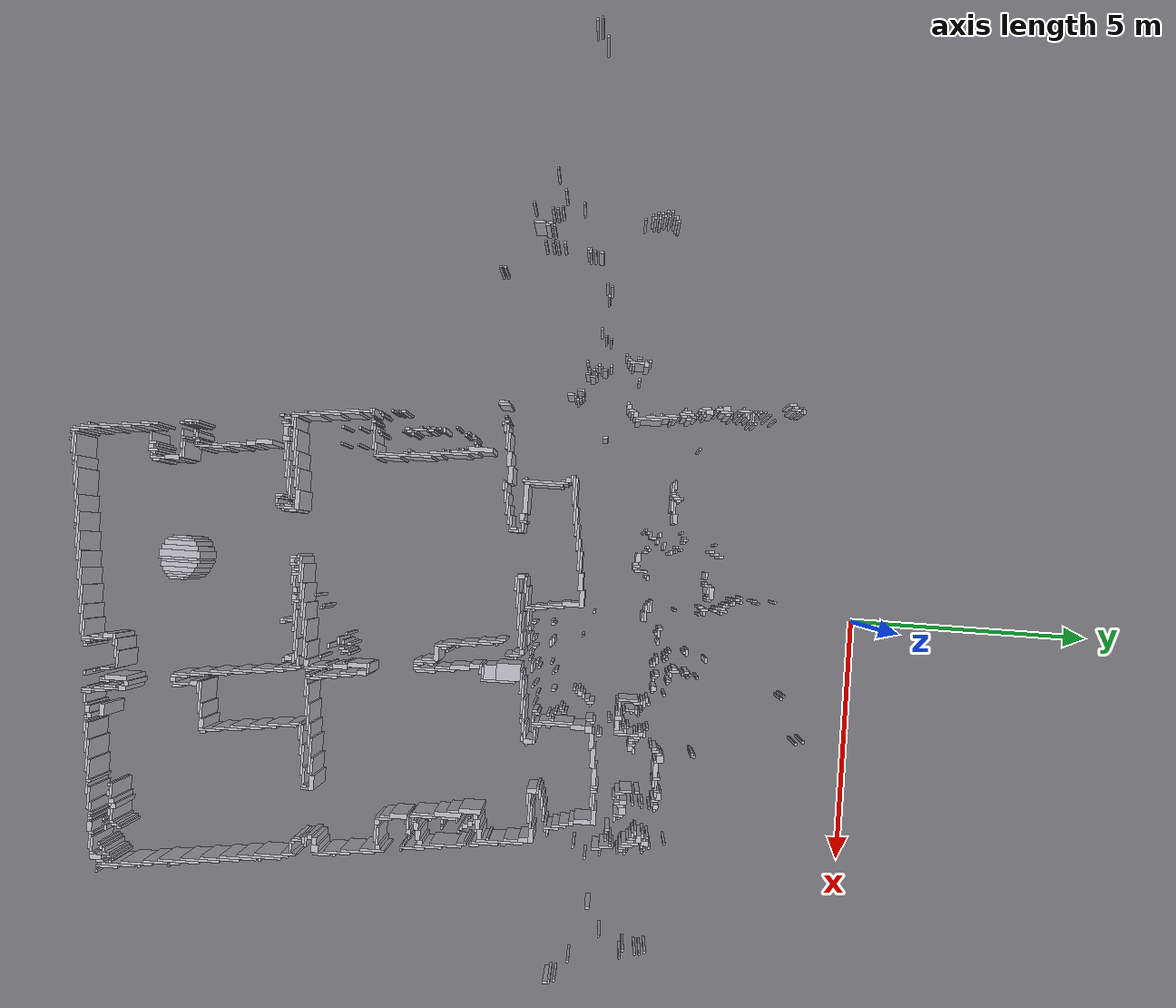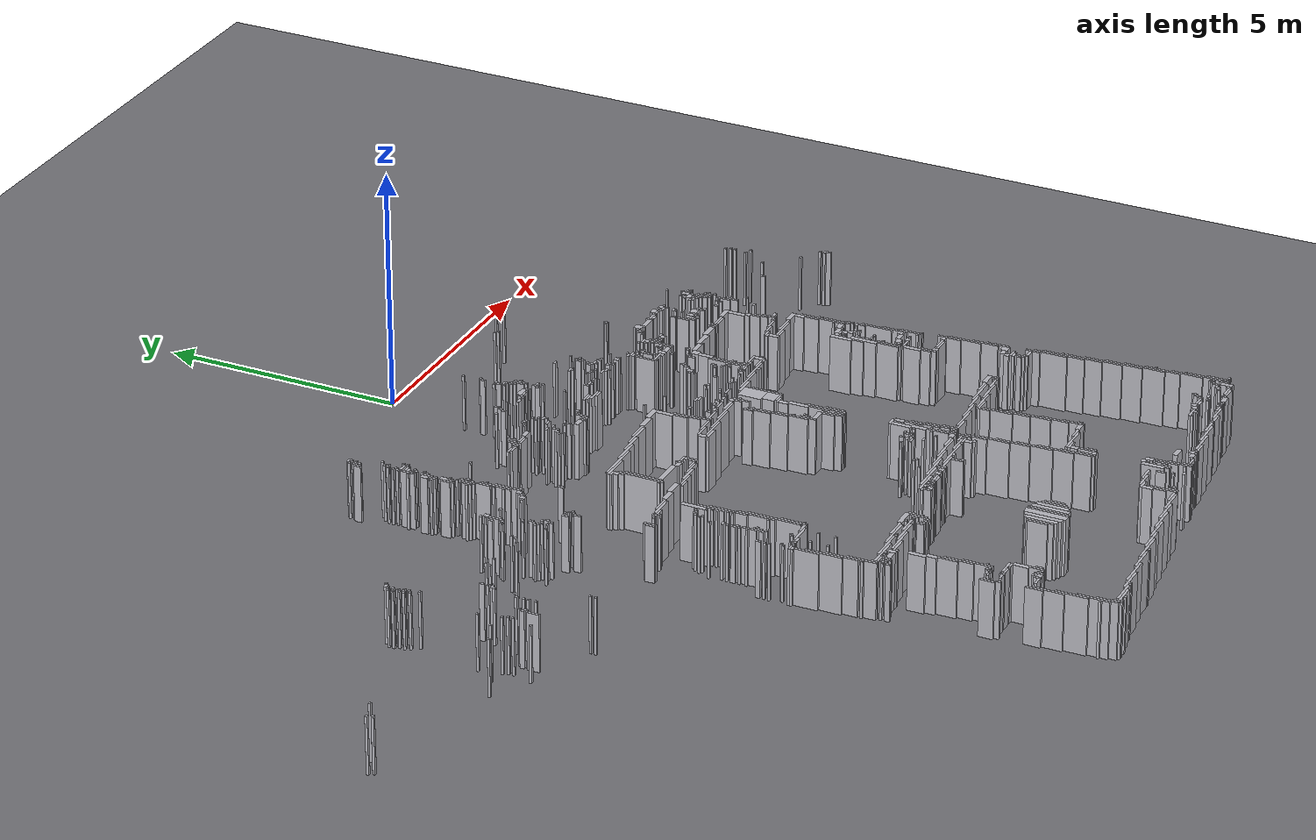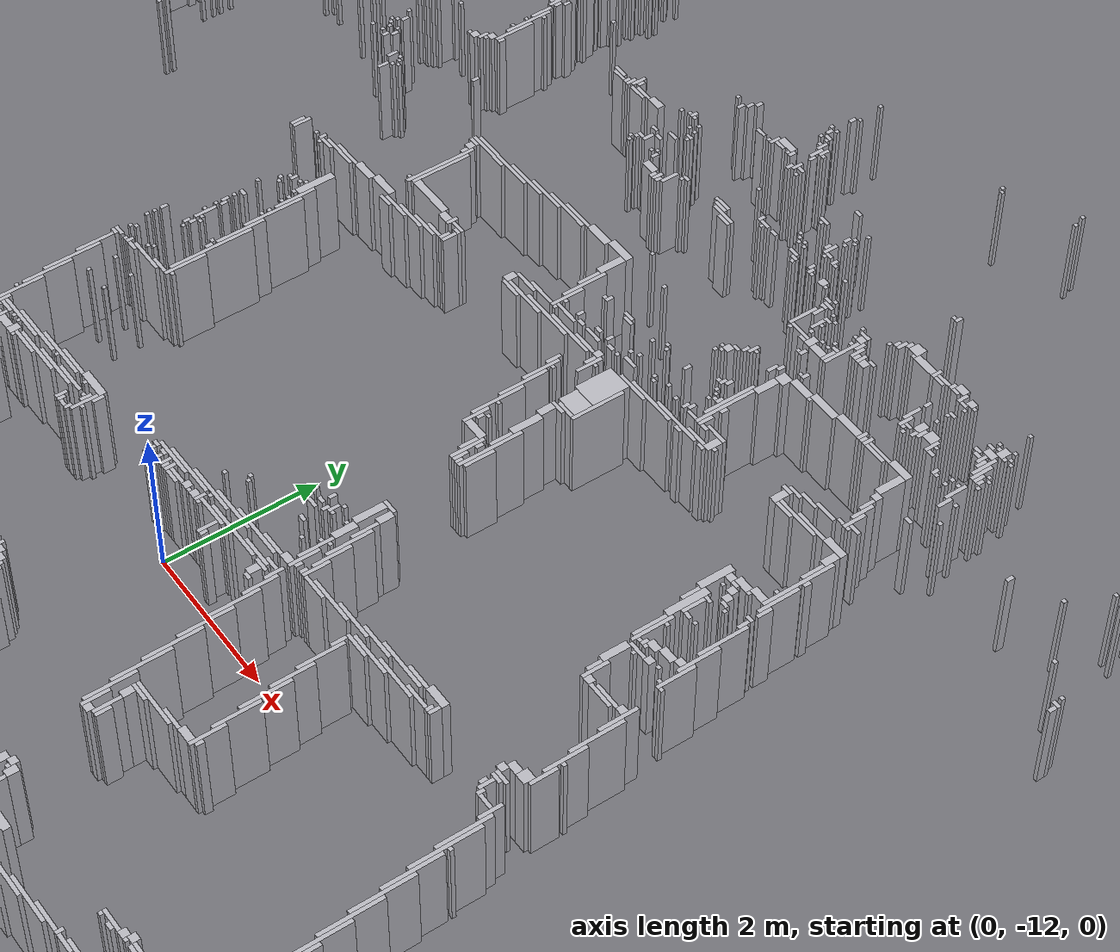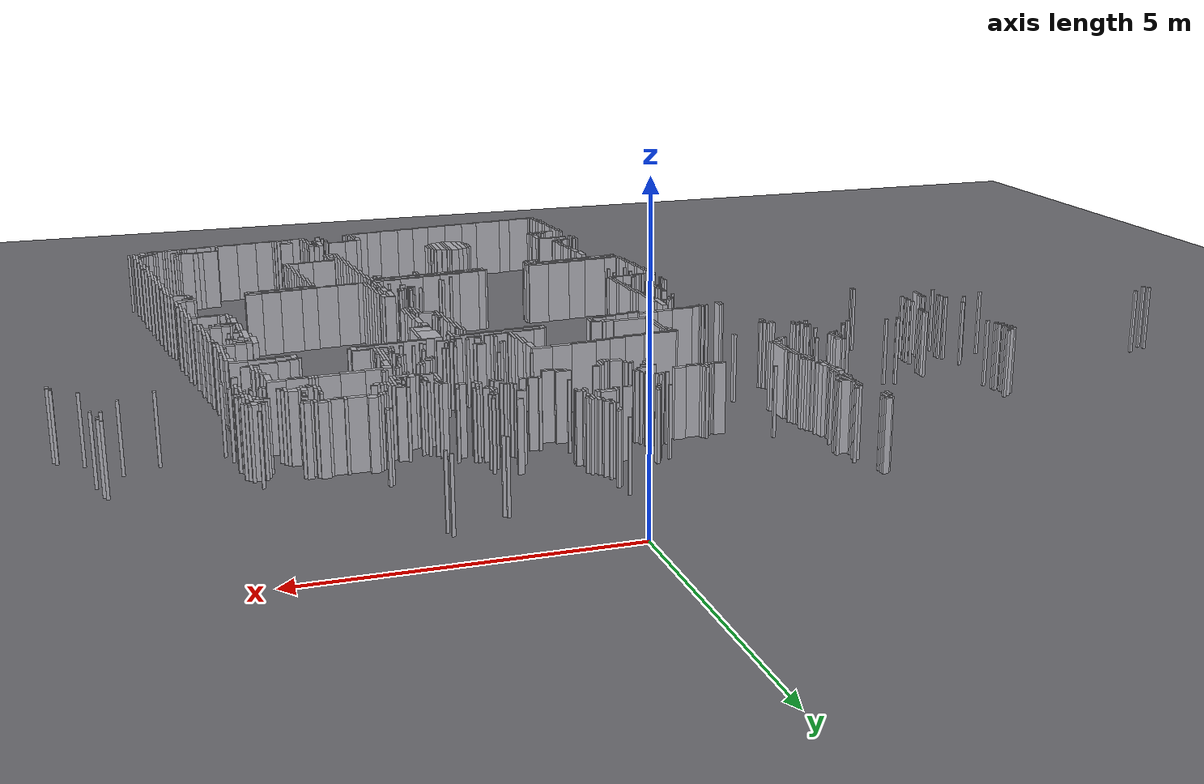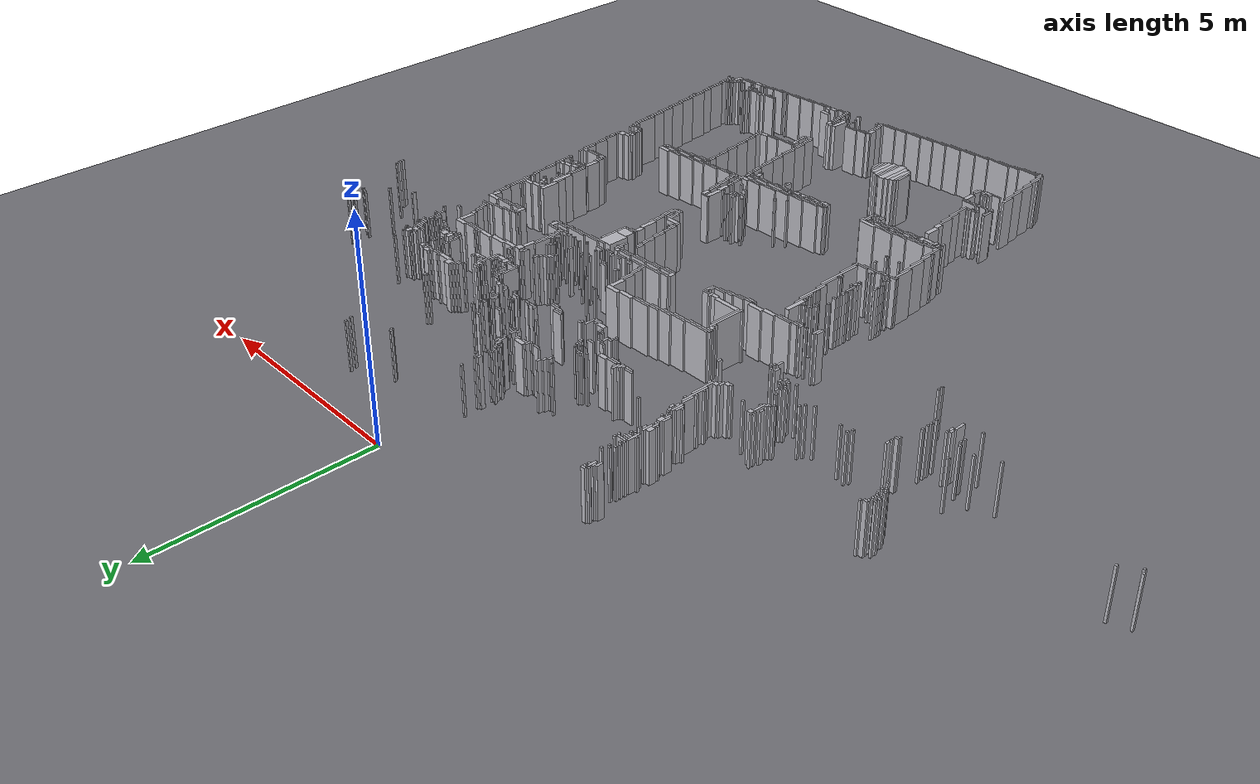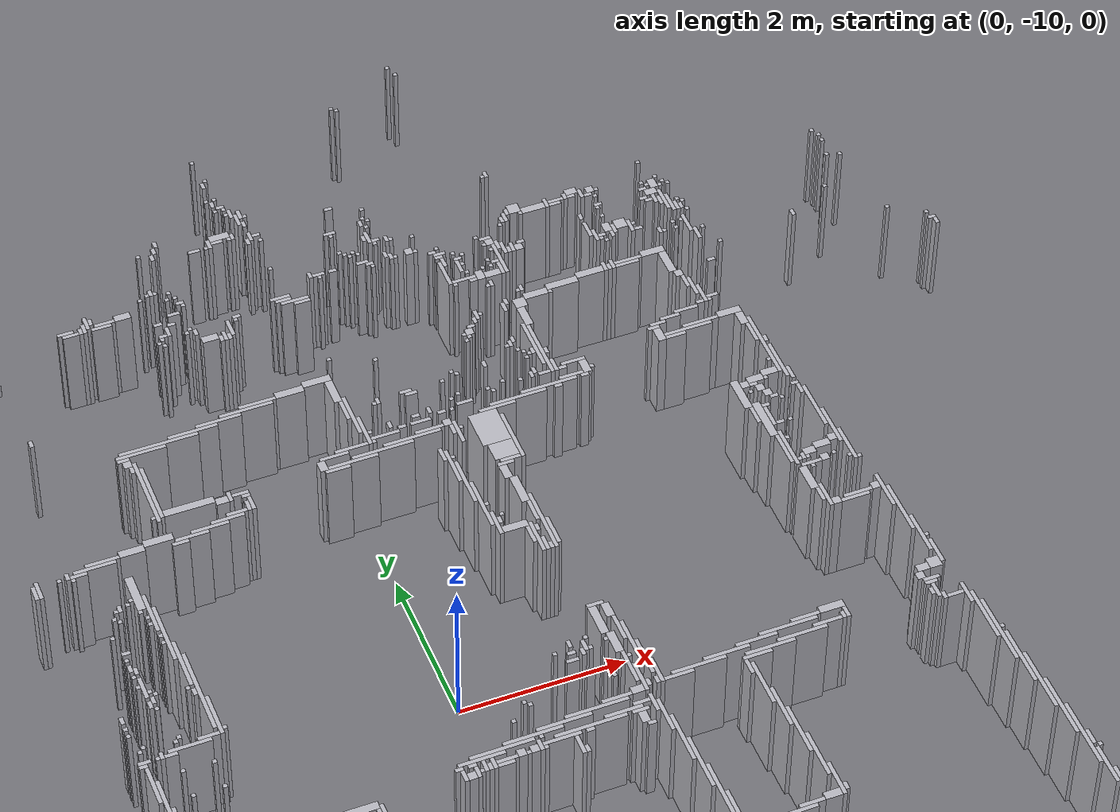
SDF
<?xml version="1.0"?>
<!-- Generated by scripts/world_from_map.py from robocup2026_1.yaml - do not edit by hand -->
<sdf version="1.9">
  <world name="arena_robocup2026_1">
    <physics name="1ms" type="dart">
      <max_step_size>0.001</max_step_size>
      <real_time_factor>1.0</real_time_factor>
    </physics>

    <plugin filename="gz-sim-physics-system" name="gz::sim::systems::Physics"/>
    <plugin filename="gz-sim-user-commands-system" name="gz::sim::systems::UserCommands"/>
    <plugin filename="gz-sim-scene-broadcaster-system" name="gz::sim::systems::SceneBroadcaster"/>
    <plugin filename="gz-sim-sensors-system" name="gz::sim::systems::Sensors">
      <render_engine>ogre2</render_engine>
    </plugin>

    <gravity>0 0 -9.81</gravity>
    <scene>
      <ambient>0.7 0.7 0.7 1</ambient>
      <background>0.8 0.85 0.9 1</background>
      <shadows>false</shadows>
    </scene>

    <light type="directional" name="sun">
      <cast_shadows>false</cast_shadows>
      <pose>0 0 12 0 0 0</pose>
      <diffuse>0.9 0.9 0.9 1</diffuse>
      <specular>0.1 0.1 0.1 1</specular>
      <direction>-0.3 0.2 -0.9</direction>
    </light>

    <model name="ground_plane">
      <static>true</static>
      <link name="link">
        <collision name="collision">
          <geometry><plane><normal>0 0 1</normal><size>37.1 37.1</size></plane></geometry>
        </collision>
        <visual name="visual">
          <geometry><plane><normal>0 0 1</normal><size>37.1 37.1</size></plane></geometry>
          <material>
            <ambient>0.35 0.35 0.36 1</ambient>
            <diffuse>0.45 0.45 0.47 1</diffuse>
          </material>
        </visual>
      </link>
    </model>

    <model name="arena_walls">
      <static>true</static>
      <link name="walls">
      <visual name="wall_0_visual">
        <pose>2.4750 -1.0250 0.6000 0 0 0</pose>
        <geometry><box><size>0.0500 0.0500 1.2000</size></box></geometry>
        <material>
          <ambient>0.55 0.55 0.58 1</ambient>
          <diffuse>0.72 0.72 0.75 1</diffuse>
          <specular>0.1 0.1 0.1 1</specular>
        </material>
      </visual>
      <visual name="wall_1_visual">
        <pose>2.5250 -1.1750 0.6000 0 0 0</pose>
        <geometry><box><size>0.0500 0.0500 1.2000</size></box></geometry>
        <material>
          <ambient>0.55 0.55 0.58 1</ambient>
          <diffuse>0.72 0.72 0.75 1</diffuse>
          <specular>0.1 0.1 0.1 1</specular>
        </material>
      </visual>
      <visual name="wall_2_visual">
        <pose>-4.3000 -1.4250 0.6000 0 0 0</pose>
        <geometry><box><size>0.1000 0.0500 1.2000</size></box></geometry>
        <material>
          <ambient>0.55 0.55 0.58 1</ambient>
          <diffuse>0.72 0.72 0.75 1</diffuse>
          <specular>0.1 0.1 0.1 1</specular>
        </material>
      </visual>
      <visual name="wall_3_visual">
        <pose>-4.3750 -1.4750 0.6000 0 0 0</pose>
        <geometry><box><size>0.0500 0.0500 1.2000</size></box></geometry>
        <material>
          <ambient>0.55 0.55 0.58 1</ambient>
          <diffuse>0.72 0.72 0.75 1</diffuse>
          <specular>0.1 0.1 0.1 1</specular>
        </material>
      </visual>
      <visual name="wall_4_visual">
        <pose>-4.2750 -1.4750 0.6000 0 0 0</pose>
        <geometry><box><size>0.0500 0.0500 1.2000</size></box></geometry>
        <material>
          <ambient>0.55 0.55 0.58 1</ambient>
          <diffuse>0.72 0.72 0.75 1</diffuse>
          <specular>0.1 0.1 0.1 1</specular>
        </material>
      </visual>
      <visual name="wall_5_visual">
        <pose>1.5750 -1.4750 0.6000 0 0 0</pose>
        <geometry><box><size>0.0500 0.0500 1.2000</size></box></geometry>
        <material>
          <ambient>0.55 0.55 0.58 1</ambient>
          <diffuse>0.72 0.72 0.75 1</diffuse>
          <specular>0.1 0.1 0.1 1</specular>
        </material>
      </visual>
      <visual name="wall_6_visual">
        <pose>-4.3250 -1.6000 0.6000 0 0 0</pose>
        <geometry><box><size>0.0500 0.2000 1.2000</size></box></geometry>
        <material>
          <ambient>0.55 0.55 0.58 1</ambient>
          <diffuse>0.72 0.72 0.75 1</diffuse>
          <specular>0.1 0.1 0.1 1</specular>
        </material>
      </visual>
      <visual name="wall_7_visual">
        <pose>1.6250 -1.5250 0.6000 0 0 0</pose>
        <geometry><box><size>0.0500 0.0500 1.2000</size></box></geometry>
        <material>
          <ambient>0.55 0.55 0.58 1</ambient>
          <diffuse>0.72 0.72 0.75 1</diffuse>
          <specular>0.1 0.1 0.1 1</specular>
        </material>
      </visual>
      <visual name="wall_8_visual">
        <pose>-4.3750 -1.6000 0.6000 0 0 0</pose>
        <geometry><box><size>0.0500 0.1000 1.2000</size></box></geometry>
        <material>
          <ambient>0.55 0.55 0.58 1</ambient>
          <diffuse>0.72 0.72 0.75 1</diffuse>
          <specular>0.1 0.1 0.1 1</specular>
        </material>
      </visual>
      <visual name="wall_9_visual">
        <pose>-4.2750 -1.5750 0.6000 0 0 0</pose>
        <geometry><box><size>0.0500 0.0500 1.2000</size></box></geometry>
        <material>
          <ambient>0.55 0.55 0.58 1</ambient>
          <diffuse>0.72 0.72 0.75 1</diffuse>
          <specular>0.1 0.1 0.1 1</specular>
        </material>
      </visual>
      <visual name="wall_10_visual">
        <pose>-4.4250 -1.6750 0.6000 0 0 0</pose>
        <geometry><box><size>0.0500 0.1500 1.2000</size></box></geometry>
        <material>
          <ambient>0.55 0.55 0.58 1</ambient>
          <diffuse>0.72 0.72 0.75 1</diffuse>
          <specular>0.1 0.1 0.1 1</specular>
        </material>
      </visual>
      <visual name="wall_11_visual">
        <pose>-0.3250 -1.7750 0.6000 0 0 0</pose>
        <geometry><box><size>0.0500 0.0500 1.2000</size></box></geometry>
        <material>
          <ambient>0.55 0.55 0.58 1</ambient>
          <diffuse>0.72 0.72 0.75 1</diffuse>
          <specular>0.1 0.1 0.1 1</specular>
        </material>
      </visual>
      <visual name="wall_12_visual">
        <pose>-4.0750 -2.0250 0.6000 0 0 0</pose>
        <geometry><box><size>0.0500 0.0500 1.2000</size></box></geometry>
        <material>
          <ambient>0.55 0.55 0.58 1</ambient>
          <diffuse>0.72 0.72 0.75 1</diffuse>
          <specular>0.1 0.1 0.1 1</specular>
        </material>
      </visual>
      <visual name="wall_13_visual">
        <pose>-4.1750 -2.1250 0.6000 0 0 0</pose>
        <geometry><box><size>0.0500 0.0500 1.2000</size></box></geometry>
        <material>
          <ambient>0.55 0.55 0.58 1</ambient>
          <diffuse>0.72 0.72 0.75 1</diffuse>
          <specular>0.1 0.1 0.1 1</specular>
        </material>
      </visual>
      <visual name="wall_14_visual">
        <pose>-0.2750 -2.1250 0.6000 0 0 0</pose>
        <geometry><box><size>0.0500 0.0500 1.2000</size></box></geometry>
        <material>
          <ambient>0.55 0.55 0.58 1</ambient>
          <diffuse>0.72 0.72 0.75 1</diffuse>
          <specular>0.1 0.1 0.1 1</specular>
        </material>
      </visual>
      <visual name="wall_15_visual">
        <pose>-4.1250 -2.1750 0.6000 0 0 0</pose>
        <geometry><box><size>0.0500 0.0500 1.2000</size></box></geometry>
        <material>
          <ambient>0.55 0.55 0.58 1</ambient>
          <diffuse>0.72 0.72 0.75 1</diffuse>
          <specular>0.1 0.1 0.1 1</specular>
        </material>
      </visual>
      <visual name="wall_16_visual">
        <pose>-0.3250 -2.2000 0.6000 0 0 0</pose>
        <geometry><box><size>0.0500 0.1000 1.2000</size></box></geometry>
        <material>
          <ambient>0.55 0.55 0.58 1</ambient>
          <diffuse>0.72 0.72 0.75 1</diffuse>
          <specular>0.1 0.1 0.1 1</specular>
        </material>
      </visual>
      <visual name="wall_17_visual">
        <pose>-4.2250 -2.2250 0.6000 0 0 0</pose>
        <geometry><box><size>0.0500 0.0500 1.2000</size></box></geometry>
        <material>
          <ambient>0.55 0.55 0.58 1</ambient>
          <diffuse>0.72 0.72 0.75 1</diffuse>
          <specular>0.1 0.1 0.1 1</specular>
        </material>
      </visual>
      <visual name="wall_18_visual">
        <pose>-4.2250 -2.3250 0.6000 0 0 0</pose>
        <geometry><box><size>0.0500 0.0500 1.2000</size></box></geometry>
        <material>
          <ambient>0.55 0.55 0.58 1</ambient>
          <diffuse>0.72 0.72 0.75 1</diffuse>
          <specular>0.1 0.1 0.1 1</specular>
        </material>
      </visual>
      <visual name="wall_19_visual">
        <pose>-4.1750 -2.3750 0.6000 0 0 0</pose>
        <geometry><box><size>0.0500 0.0500 1.2000</size></box></geometry>
        <material>
          <ambient>0.55 0.55 0.58 1</ambient>
          <diffuse>0.72 0.72 0.75 1</diffuse>
          <specular>0.1 0.1 0.1 1</specular>
        </material>
      </visual>
      <visual name="wall_20_visual">
        <pose>-4.2250 -2.4250 0.6000 0 0 0</pose>
        <geometry><box><size>0.0500 0.0500 1.2000</size></box></geometry>
        <material>
          <ambient>0.55 0.55 0.58 1</ambient>
          <diffuse>0.72 0.72 0.75 1</diffuse>
          <specular>0.1 0.1 0.1 1</specular>
        </material>
      </visual>
      <visual name="wall_21_visual">
        <pose>-3.9750 -2.4250 0.6000 0 0 0</pose>
        <geometry><box><size>0.0500 0.0500 1.2000</size></box></geometry>
        <material>
          <ambient>0.55 0.55 0.58 1</ambient>
          <diffuse>0.72 0.72 0.75 1</diffuse>
          <specular>0.1 0.1 0.1 1</specular>
        </material>
      </visual>
      <visual name="wall_22_visual">
        <pose>-4.1000 -2.4750 0.6000 0 0 0</pose>
        <geometry><box><size>0.2000 0.0500 1.2000</size></box></geometry>
        <material>
          <ambient>0.55 0.55 0.58 1</ambient>
          <diffuse>0.72 0.72 0.75 1</diffuse>
          <specular>0.1 0.1 0.1 1</specular>
        </material>
      </visual>
      <visual name="wall_23_visual">
        <pose>-0.3750 -2.4750 0.6000 0 0 0</pose>
        <geometry><box><size>0.0500 0.0500 1.2000</size></box></geometry>
        <material>
          <ambient>0.55 0.55 0.58 1</ambient>
          <diffuse>0.72 0.72 0.75 1</diffuse>
          <specular>0.1 0.1 0.1 1</specular>
        </material>
      </visual>
      <visual name="wall_24_visual">
        <pose>-0.2750 -2.4750 0.6000 0 0 0</pose>
        <geometry><box><size>0.0500 0.0500 1.2000</size></box></geometry>
        <material>
          <ambient>0.55 0.55 0.58 1</ambient>
          <diffuse>0.72 0.72 0.75 1</diffuse>
          <specular>0.1 0.1 0.1 1</specular>
        </material>
      </visual>
      <visual name="wall_25_visual">
        <pose>-4.2250 -2.6500 0.6000 0 0 0</pose>
        <geometry><box><size>0.0500 0.3000 1.2000</size></box></geometry>
        <material>
          <ambient>0.55 0.55 0.58 1</ambient>
          <diffuse>0.72 0.72 0.75 1</diffuse>
          <specular>0.1 0.1 0.1 1</specular>
        </material>
      </visual>
      <visual name="wall_26_visual">
        <pose>-3.9750 -2.5250 0.6000 0 0 0</pose>
        <geometry><box><size>0.0500 0.0500 1.2000</size></box></geometry>
        <material>
          <ambient>0.55 0.55 0.58 1</ambient>
          <diffuse>0.72 0.72 0.75 1</diffuse>
          <specular>0.1 0.1 0.1 1</specular>
        </material>
      </visual>
      <visual name="wall_27_visual">
        <pose>-0.3250 -2.5500 0.6000 0 0 0</pose>
        <geometry><box><size>0.0500 0.1000 1.2000</size></box></geometry>
        <material>
          <ambient>0.55 0.55 0.58 1</ambient>
          <diffuse>0.72 0.72 0.75 1</diffuse>
          <specular>0.1 0.1 0.1 1</specular>
        </material>
      </visual>
      <visual name="wall_28_visual">
        <pose>-4.1250 -2.5750 0.6000 0 0 0</pose>
        <geometry><box><size>0.1500 0.0500 1.2000</size></box></geometry>
        <material>
          <ambient>0.55 0.55 0.58 1</ambient>
          <diffuse>0.72 0.72 0.75 1</diffuse>
          <specular>0.1 0.1 0.1 1</specular>
        </material>
      </visual>
      <visual name="wall_29_visual">
        <pose>-4.1500 -2.6250 0.6000 0 0 0</pose>
        <geometry><box><size>0.1000 0.0500 1.2000</size></box></geometry>
        <material>
          <ambient>0.55 0.55 0.58 1</ambient>
          <diffuse>0.72 0.72 0.75 1</diffuse>
          <specular>0.1 0.1 0.1 1</specular>
        </material>
      </visual>
      <visual name="wall_30_visual">
        <pose>-0.2500 -2.6250 0.6000 0 0 0</pose>
        <geometry><box><size>0.1000 0.0500 1.2000</size></box></geometry>
        <material>
          <ambient>0.55 0.55 0.58 1</ambient>
          <diffuse>0.72 0.72 0.75 1</diffuse>
          <specular>0.1 0.1 0.1 1</specular>
        </material>
      </visual>
      <visual name="wall_31_visual">
        <pose>-4.2750 -2.6750 0.6000 0 0 0</pose>
        <geometry><box><size>0.0500 0.0500 1.2000</size></box></geometry>
        <material>
          <ambient>0.55 0.55 0.58 1</ambient>
          <diffuse>0.72 0.72 0.75 1</diffuse>
          <specular>0.1 0.1 0.1 1</specular>
        </material>
      </visual>
      <visual name="wall_32_visual">
        <pose>-0.3250 -2.6750 0.6000 0 0 0</pose>
        <geometry><box><size>0.0500 0.0500 1.2000</size></box></geometry>
        <material>
          <ambient>0.55 0.55 0.58 1</ambient>
          <diffuse>0.72 0.72 0.75 1</diffuse>
          <specular>0.1 0.1 0.1 1</specular>
        </material>
      </visual>
      <visual name="wall_33_visual">
        <pose>-0.2250 -2.6750 0.6000 0 0 0</pose>
        <geometry><box><size>0.0500 0.0500 1.2000</size></box></geometry>
        <material>
          <ambient>0.55 0.55 0.58 1</ambient>
          <diffuse>0.72 0.72 0.75 1</diffuse>
          <specular>0.1 0.1 0.1 1</specular>
        </material>
      </visual>
      <visual name="wall_34_visual">
        <pose>-4.1750 -2.7250 0.6000 0 0 0</pose>
        <geometry><box><size>0.0500 0.0500 1.2000</size></box></geometry>
        <material>
          <ambient>0.55 0.55 0.58 1</ambient>
          <diffuse>0.72 0.72 0.75 1</diffuse>
          <specular>0.1 0.1 0.1 1</specular>
        </material>
      </visual>
      <visual name="wall_35_visual">
        <pose>-4.0750 -2.7250 0.6000 0 0 0</pose>
        <geometry><box><size>0.0500 0.0500 1.2000</size></box></geometry>
        <material>
          <ambient>0.55 0.55 0.58 1</ambient>
          <diffuse>0.72 0.72 0.75 1</diffuse>
          <specular>0.1 0.1 0.1 1</specular>
        </material>
      </visual>
      <visual name="wall_36_visual">
        <pose>-0.1750 -2.7750 0.6000 0 0 0</pose>
        <geometry><box><size>0.0500 0.1500 1.2000</size></box></geometry>
        <material>
          <ambient>0.55 0.55 0.58 1</ambient>
          <diffuse>0.72 0.72 0.75 1</diffuse>
          <specular>0.1 0.1 0.1 1</specular>
        </material>
      </visual>
      <visual name="wall_37_visual">
        <pose>-4.1250 -2.7750 0.6000 0 0 0</pose>
        <geometry><box><size>0.0500 0.0500 1.2000</size></box></geometry>
        <material>
          <ambient>0.55 0.55 0.58 1</ambient>
          <diffuse>0.72 0.72 0.75 1</diffuse>
          <specular>0.1 0.1 0.1 1</specular>
        </material>
      </visual>
      <visual name="wall_38_visual">
        <pose>-0.2250 -2.7750 0.6000 0 0 0</pose>
        <geometry><box><size>0.0500 0.0500 1.2000</size></box></geometry>
        <material>
          <ambient>0.55 0.55 0.58 1</ambient>
          <diffuse>0.72 0.72 0.75 1</diffuse>
          <specular>0.1 0.1 0.1 1</specular>
        </material>
      </visual>
      <visual name="wall_39_visual">
        <pose>-0.0750 -2.8250 0.6000 0 0 0</pose>
        <geometry><box><size>0.0500 0.1500 1.2000</size></box></geometry>
        <material>
          <ambient>0.55 0.55 0.58 1</ambient>
          <diffuse>0.72 0.72 0.75 1</diffuse>
          <specular>0.1 0.1 0.1 1</specular>
        </material>
      </visual>
      <visual name="wall_40_visual">
        <pose>-0.1250 -2.9000 0.6000 0 0 0</pose>
        <geometry><box><size>0.0500 0.2000 1.2000</size></box></geometry>
        <material>
          <ambient>0.55 0.55 0.58 1</ambient>
          <diffuse>0.72 0.72 0.75 1</diffuse>
          <specular>0.1 0.1 0.1 1</specular>
        </material>
      </visual>
      <visual name="wall_41_visual">
        <pose>-0.0250 -2.8750 0.6000 0 0 0</pose>
        <geometry><box><size>0.0500 0.0500 1.2000</size></box></geometry>
        <material>
          <ambient>0.55 0.55 0.58 1</ambient>
          <diffuse>0.72 0.72 0.75 1</diffuse>
          <specular>0.1 0.1 0.1 1</specular>
        </material>
      </visual>
      <visual name="wall_42_visual">
        <pose>-4.1750 -3.0250 0.6000 0 0 0</pose>
        <geometry><box><size>0.0500 0.2500 1.2000</size></box></geometry>
        <material>
          <ambient>0.55 0.55 0.58 1</ambient>
          <diffuse>0.72 0.72 0.75 1</diffuse>
          <specular>0.1 0.1 0.1 1</specular>
        </material>
      </visual>
      <visual name="wall_43_visual">
        <pose>-4.0750 -2.9250 0.6000 0 0 0</pose>
        <geometry><box><size>0.0500 0.0500 1.2000</size></box></geometry>
        <material>
          <ambient>0.55 0.55 0.58 1</ambient>
          <diffuse>0.72 0.72 0.75 1</diffuse>
          <specular>0.1 0.1 0.1 1</specular>
        </material>
      </visual>
      <visual name="wall_44_visual">
        <pose>-1.1750 -2.9500 0.6000 0 0 0</pose>
        <geometry><box><size>0.0500 0.1000 1.2000</size></box></geometry>
        <material>
          <ambient>0.55 0.55 0.58 1</ambient>
          <diffuse>0.72 0.72 0.75 1</diffuse>
          <specular>0.1 0.1 0.1 1</specular>
        </material>
      </visual>
      <visual name="wall_45_visual">
        <pose>-4.2500 -3.0250 0.6000 0 0 0</pose>
        <geometry><box><size>0.1000 0.1500 1.2000</size></box></geometry>
        <material>
          <ambient>0.55 0.55 0.58 1</ambient>
          <diffuse>0.72 0.72 0.75 1</diffuse>
          <specular>0.1 0.1 0.1 1</specular>
        </material>
      </visual>
      <visual name="wall_46_visual">
        <pose>-4.1250 -3.0000 0.6000 0 0 0</pose>
        <geometry><box><size>0.0500 0.1000 1.2000</size></box></geometry>
        <material>
          <ambient>0.55 0.55 0.58 1</ambient>
          <diffuse>0.72 0.72 0.75 1</diffuse>
          <specular>0.1 0.1 0.1 1</specular>
        </material>
      </visual>
      <visual name="wall_47_visual">
        <pose>-0.0750 -3.0000 0.6000 0 0 0</pose>
        <geometry><box><size>0.0500 0.1000 1.2000</size></box></geometry>
        <material>
          <ambient>0.55 0.55 0.58 1</ambient>
          <diffuse>0.72 0.72 0.75 1</diffuse>
          <specular>0.1 0.1 0.1 1</specular>
        </material>
      </visual>
      <visual name="wall_48_visual">
        <pose>-1.2250 -3.0500 0.6000 0 0 0</pose>
        <geometry><box><size>0.0500 0.1000 1.2000</size></box></geometry>
        <material>
          <ambient>0.55 0.55 0.58 1</ambient>
          <diffuse>0.72 0.72 0.75 1</diffuse>
          <specular>0.1 0.1 0.1 1</specular>
        </material>
      </visual>
      <visual name="wall_49_visual">
        <pose>-1.4250 -3.0750 0.6000 0 0 0</pose>
        <geometry><box><size>0.0500 0.0500 1.2000</size></box></geometry>
        <material>
          <ambient>0.55 0.55 0.58 1</ambient>
          <diffuse>0.72 0.72 0.75 1</diffuse>
          <specular>0.1 0.1 0.1 1</specular>
        </material>
      </visual>
      <visual name="wall_50_visual">
        <pose>-0.4250 -3.1000 0.6000 0 0 0</pose>
        <geometry><box><size>0.2500 0.1000 1.2000</size></box></geometry>
        <material>
          <ambient>0.55 0.55 0.58 1</ambient>
          <diffuse>0.72 0.72 0.75 1</diffuse>
          <specular>0.1 0.1 0.1 1</specular>
        </material>
      </visual>
      <visual name="wall_51_visual">
        <pose>-4.2250 -3.1750 0.6000 0 0 0</pose>
        <geometry><box><size>0.0500 0.1500 1.2000</size></box></geometry>
        <material>
          <ambient>0.55 0.55 0.58 1</ambient>
          <diffuse>0.72 0.72 0.75 1</diffuse>
          <specular>0.1 0.1 0.1 1</specular>
        </material>
      </visual>
      <visual name="wall_52_visual">
        <pose>-1.2750 -3.1500 0.6000 0 0 0</pose>
        <geometry><box><size>0.0500 0.1000 1.2000</size></box></geometry>
        <material>
          <ambient>0.55 0.55 0.58 1</ambient>
          <diffuse>0.72 0.72 0.75 1</diffuse>
          <specular>0.1 0.1 0.1 1</specular>
        </material>
      </visual>
      <visual name="wall_53_visual">
        <pose>-0.5750 -3.1750 0.6000 0 0 0</pose>
        <geometry><box><size>0.0500 0.1500 1.2000</size></box></geometry>
        <material>
          <ambient>0.55 0.55 0.58 1</ambient>
          <diffuse>0.72 0.72 0.75 1</diffuse>
          <specular>0.1 0.1 0.1 1</specular>
        </material>
      </visual>
      <visual name="wall_54_visual">
        <pose>-0.2750 -3.1500 0.6000 0 0 0</pose>
        <geometry><box><size>0.0500 0.1000 1.2000</size></box></geometry>
        <material>
          <ambient>0.55 0.55 0.58 1</ambient>
          <diffuse>0.72 0.72 0.75 1</diffuse>
          <specular>0.1 0.1 0.1 1</specular>
        </material>
      </visual>
      <visual name="wall_55_visual">
        <pose>0.9500 -3.1250 0.6000 0 0 0</pose>
        <geometry><box><size>0.1000 0.0500 1.2000</size></box></geometry>
        <material>
          <ambient>0.55 0.55 0.58 1</ambient>
          <diffuse>0.72 0.72 0.75 1</diffuse>
          <specular>0.1 0.1 0.1 1</specular>
        </material>
      </visual>
      <visual name="wall_56_visual">
        <pose>-4.2750 -3.1750 0.6000 0 0 0</pose>
        <geometry><box><size>0.0500 0.0500 1.2000</size></box></geometry>
        <material>
          <ambient>0.55 0.55 0.58 1</ambient>
          <diffuse>0.72 0.72 0.75 1</diffuse>
          <specular>0.1 0.1 0.1 1</specular>
        </material>
      </visual>
      <visual name="wall_57_visual">
        <pose>-0.4750 -3.1750 0.6000 0 0 0</pose>
        <geometry><box><size>0.1500 0.0500 1.2000</size></box></geometry>
        <material>
          <ambient>0.55 0.55 0.58 1</ambient>
          <diffuse>0.72 0.72 0.75 1</diffuse>
          <specular>0.1 0.1 0.1 1</specular>
        </material>
      </visual>
      <visual name="wall_58_visual">
        <pose>-0.3250 -3.1750 0.6000 0 0 0</pose>
        <geometry><box><size>0.0500 0.0500 1.2000</size></box></geometry>
        <material>
          <ambient>0.55 0.55 0.58 1</ambient>
          <diffuse>0.72 0.72 0.75 1</diffuse>
          <specular>0.1 0.1 0.1 1</specular>
        </material>
      </visual>
      <visual name="wall_59_visual">
        <pose>-0.0750 -3.2250 0.6000 0 0 0</pose>
        <geometry><box><size>0.0500 0.1500 1.2000</size></box></geometry>
        <material>
          <ambient>0.55 0.55 0.58 1</ambient>
          <diffuse>0.72 0.72 0.75 1</diffuse>
          <specular>0.1 0.1 0.1 1</specular>
        </material>
      </visual>
      <visual name="wall_60_visual">
        <pose>-4.1750 -3.2250 0.6000 0 0 0</pose>
        <geometry><box><size>0.0500 0.0500 1.2000</size></box></geometry>
        <material>
          <ambient>0.55 0.55 0.58 1</ambient>
          <diffuse>0.72 0.72 0.75 1</diffuse>
          <specular>0.1 0.1 0.1 1</specular>
        </material>
      </visual>
      <visual name="wall_61_visual">
        <pose>-0.7750 -3.2250 0.6000 0 0 0</pose>
        <geometry><box><size>0.1500 0.0500 1.2000</size></box></geometry>
        <material>
          <ambient>0.55 0.55 0.58 1</ambient>
          <diffuse>0.72 0.72 0.75 1</diffuse>
          <specular>0.1 0.1 0.1 1</specular>
        </material>
      </visual>
      <visual name="wall_62_visual">
        <pose>-0.6250 -3.2250 0.6000 0 0 0</pose>
        <geometry><box><size>0.0500 0.0500 1.2000</size></box></geometry>
        <material>
          <ambient>0.55 0.55 0.58 1</ambient>
          <diffuse>0.72 0.72 0.75 1</diffuse>
          <specular>0.1 0.1 0.1 1</specular>
        </material>
      </visual>
      <visual name="wall_63_visual">
        <pose>0.0000 -3.2250 0.6000 0 0 0</pose>
        <geometry><box><size>0.1000 0.0500 1.2000</size></box></geometry>
        <material>
          <ambient>0.55 0.55 0.58 1</ambient>
          <diffuse>0.72 0.72 0.75 1</diffuse>
          <specular>0.1 0.1 0.1 1</specular>
        </material>
      </visual>
      <visual name="wall_64_visual">
        <pose>2.9250 -3.2500 0.6000 0 0 0</pose>
        <geometry><box><size>0.0500 0.1000 1.2000</size></box></geometry>
        <material>
          <ambient>0.55 0.55 0.58 1</ambient>
          <diffuse>0.72 0.72 0.75 1</diffuse>
          <specular>0.1 0.1 0.1 1</specular>
        </material>
      </visual>
      <visual name="wall_65_visual">
        <pose>-0.1250 -3.3000 0.6000 0 0 0</pose>
        <geometry><box><size>0.0500 0.1000 1.2000</size></box></geometry>
        <material>
          <ambient>0.55 0.55 0.58 1</ambient>
          <diffuse>0.72 0.72 0.75 1</diffuse>
          <specular>0.1 0.1 0.1 1</specular>
        </material>
      </visual>
      <visual name="wall_66_visual">
        <pose>1.3250 -3.2750 0.6000 0 0 0</pose>
        <geometry><box><size>0.0500 0.0500 1.2000</size></box></geometry>
        <material>
          <ambient>0.55 0.55 0.58 1</ambient>
          <diffuse>0.72 0.72 0.75 1</diffuse>
          <specular>0.1 0.1 0.1 1</specular>
        </material>
      </visual>
      <visual name="wall_67_visual">
        <pose>2.8750 -3.2750 0.6000 0 0 0</pose>
        <geometry><box><size>0.0500 0.0500 1.2000</size></box></geometry>
        <material>
          <ambient>0.55 0.55 0.58 1</ambient>
          <diffuse>0.72 0.72 0.75 1</diffuse>
          <specular>0.1 0.1 0.1 1</specular>
        </material>
      </visual>
      <visual name="wall_68_visual">
        <pose>-4.1500 -3.3750 0.6000 0 0 0</pose>
        <geometry><box><size>0.1000 0.1500 1.2000</size></box></geometry>
        <material>
          <ambient>0.55 0.55 0.58 1</ambient>
          <diffuse>0.72 0.72 0.75 1</diffuse>
          <specular>0.1 0.1 0.1 1</specular>
        </material>
      </visual>
      <visual name="wall_69_visual">
        <pose>0.0250 -3.3250 0.6000 0 0 0</pose>
        <geometry><box><size>0.0500 0.0500 1.2000</size></box></geometry>
        <material>
          <ambient>0.55 0.55 0.58 1</ambient>
          <diffuse>0.72 0.72 0.75 1</diffuse>
          <specular>0.1 0.1 0.1 1</specular>
        </material>
      </visual>
      <visual name="wall_70_visual">
        <pose>-4.2250 -3.4500 0.6000 0 0 0</pose>
        <geometry><box><size>0.0500 0.2000 1.2000</size></box></geometry>
        <material>
          <ambient>0.55 0.55 0.58 1</ambient>
          <diffuse>0.72 0.72 0.75 1</diffuse>
          <specular>0.1 0.1 0.1 1</specular>
        </material>
      </visual>
      <visual name="wall_71_visual">
        <pose>1.2750 -3.4250 0.6000 0 0 0</pose>
        <geometry><box><size>0.0500 0.0500 1.2000</size></box></geometry>
        <material>
          <ambient>0.55 0.55 0.58 1</ambient>
          <diffuse>0.72 0.72 0.75 1</diffuse>
          <specular>0.1 0.1 0.1 1</specular>
        </material>
      </visual>
      <visual name="wall_72_visual">
        <pose>-4.1750 -3.5250 0.6000 0 0 0</pose>
        <geometry><box><size>0.0500 0.1500 1.2000</size></box></geometry>
        <material>
          <ambient>0.55 0.55 0.58 1</ambient>
          <diffuse>0.72 0.72 0.75 1</diffuse>
          <specular>0.1 0.1 0.1 1</specular>
        </material>
      </visual>
      <visual name="wall_73_visual">
        <pose>-4.0750 -3.4750 0.6000 0 0 0</pose>
        <geometry><box><size>0.0500 0.0500 1.2000</size></box></geometry>
        <material>
          <ambient>0.55 0.55 0.58 1</ambient>
          <diffuse>0.72 0.72 0.75 1</diffuse>
          <specular>0.1 0.1 0.1 1</specular>
        </material>
      </visual>
      <visual name="wall_74_visual">
        <pose>1.2250 -3.5000 0.6000 0 0 0</pose>
        <geometry><box><size>0.0500 0.1000 1.2000</size></box></geometry>
        <material>
          <ambient>0.55 0.55 0.58 1</ambient>
          <diffuse>0.72 0.72 0.75 1</diffuse>
          <specular>0.1 0.1 0.1 1</specular>
        </material>
      </visual>
      <visual name="wall_75_visual">
        <pose>1.3250 -3.4750 0.6000 0 0 0</pose>
        <geometry><box><size>0.0500 0.0500 1.2000</size></box></geometry>
        <material>
          <ambient>0.55 0.55 0.58 1</ambient>
          <diffuse>0.72 0.72 0.75 1</diffuse>
          <specular>0.1 0.1 0.1 1</specular>
        </material>
      </visual>
      <visual name="wall_76_visual">
        <pose>-4.1250 -3.5250 0.6000 0 0 0</pose>
        <geometry><box><size>0.0500 0.0500 1.2000</size></box></geometry>
        <material>
          <ambient>0.55 0.55 0.58 1</ambient>
          <diffuse>0.72 0.72 0.75 1</diffuse>
          <specular>0.1 0.1 0.1 1</specular>
        </material>
      </visual>
      <visual name="wall_77_visual">
        <pose>-3.3750 -3.5250 0.6000 0 0 0</pose>
        <geometry><box><size>0.0500 0.0500 1.2000</size></box></geometry>
        <material>
          <ambient>0.55 0.55 0.58 1</ambient>
          <diffuse>0.72 0.72 0.75 1</diffuse>
          <specular>0.1 0.1 0.1 1</specular>
        </material>
      </visual>
      <visual name="wall_78_visual">
        <pose>0.8250 -3.5250 0.6000 0 0 0</pose>
        <geometry><box><size>0.1500 0.0500 1.2000</size></box></geometry>
        <material>
          <ambient>0.55 0.55 0.58 1</ambient>
          <diffuse>0.72 0.72 0.75 1</diffuse>
          <specular>0.1 0.1 0.1 1</specular>
        </material>
      </visual>
      <visual name="wall_79_visual">
        <pose>0.8250 -3.5750 0.6000 0 0 0</pose>
        <geometry><box><size>0.0500 0.0500 1.2000</size></box></geometry>
        <material>
          <ambient>0.55 0.55 0.58 1</ambient>
          <diffuse>0.72 0.72 0.75 1</diffuse>
          <specular>0.1 0.1 0.1 1</specular>
        </material>
      </visual>
      <visual name="wall_80_visual">
        <pose>1.2750 -3.5750 0.6000 0 0 0</pose>
        <geometry><box><size>0.0500 0.0500 1.2000</size></box></geometry>
        <material>
          <ambient>0.55 0.55 0.58 1</ambient>
          <diffuse>0.72 0.72 0.75 1</diffuse>
          <specular>0.1 0.1 0.1 1</specular>
        </material>
      </visual>
      <visual name="wall_81_visual">
        <pose>-4.0750 -3.6250 0.6000 0 0 0</pose>
        <geometry><box><size>0.0500 0.0500 1.2000</size></box></geometry>
        <material>
          <ambient>0.55 0.55 0.58 1</ambient>
          <diffuse>0.72 0.72 0.75 1</diffuse>
          <specular>0.1 0.1 0.1 1</specular>
        </material>
      </visual>
      <visual name="wall_82_visual">
        <pose>-4.0250 -3.7000 0.6000 0 0 0</pose>
        <geometry><box><size>0.0500 0.1000 1.2000</size></box></geometry>
        <material>
          <ambient>0.55 0.55 0.58 1</ambient>
          <diffuse>0.72 0.72 0.75 1</diffuse>
          <specular>0.1 0.1 0.1 1</specular>
        </material>
      </visual>
      <visual name="wall_83_visual">
        <pose>-1.4750 -3.7000 0.6000 0 0 0</pose>
        <geometry><box><size>0.0500 0.1000 1.2000</size></box></geometry>
        <material>
          <ambient>0.55 0.55 0.58 1</ambient>
          <diffuse>0.72 0.72 0.75 1</diffuse>
          <specular>0.1 0.1 0.1 1</specular>
        </material>
      </visual>
      <visual name="wall_84_visual">
        <pose>1.2250 -3.7500 0.6000 0 0 0</pose>
        <geometry><box><size>0.0500 0.2000 1.2000</size></box></geometry>
        <material>
          <ambient>0.55 0.55 0.58 1</ambient>
          <diffuse>0.72 0.72 0.75 1</diffuse>
          <specular>0.1 0.1 0.1 1</specular>
        </material>
      </visual>
      <visual name="wall_85_visual">
        <pose>-4.0750 -3.8500 0.6000 0 0 0</pose>
        <geometry><box><size>0.0500 0.3000 1.2000</size></box></geometry>
        <material>
          <ambient>0.55 0.55 0.58 1</ambient>
          <diffuse>0.72 0.72 0.75 1</diffuse>
          <specular>0.1 0.1 0.1 1</specular>
        </material>
      </visual>
      <visual name="wall_86_visual">
        <pose>-1.5250 -3.7250 0.6000 0 0 0</pose>
        <geometry><box><size>0.0500 0.0500 1.2000</size></box></geometry>
        <material>
          <ambient>0.55 0.55 0.58 1</ambient>
          <diffuse>0.72 0.72 0.75 1</diffuse>
          <specular>0.1 0.1 0.1 1</specular>
        </material>
      </visual>
      <visual name="wall_87_visual">
        <pose>-1.4250 -3.7250 0.6000 0 0 0</pose>
        <geometry><box><size>0.0500 0.0500 1.2000</size></box></geometry>
        <material>
          <ambient>0.55 0.55 0.58 1</ambient>
          <diffuse>0.72 0.72 0.75 1</diffuse>
          <specular>0.1 0.1 0.1 1</specular>
        </material>
      </visual>
      <visual name="wall_88_visual">
        <pose>1.1750 -3.7500 0.6000 0 0 0</pose>
        <geometry><box><size>0.0500 0.1000 1.2000</size></box></geometry>
        <material>
          <ambient>0.55 0.55 0.58 1</ambient>
          <diffuse>0.72 0.72 0.75 1</diffuse>
          <specular>0.1 0.1 0.1 1</specular>
        </material>
      </visual>
      <visual name="wall_89_visual">
        <pose>4.7250 -3.7250 0.6000 0 0 0</pose>
        <geometry><box><size>0.0500 0.0500 1.2000</size></box></geometry>
        <material>
          <ambient>0.55 0.55 0.58 1</ambient>
          <diffuse>0.72 0.72 0.75 1</diffuse>
          <specular>0.1 0.1 0.1 1</specular>
        </material>
      </visual>
      <visual name="wall_90_visual">
        <pose>-4.1250 -3.8500 0.6000 0 0 0</pose>
        <geometry><box><size>0.0500 0.2000 1.2000</size></box></geometry>
        <material>
          <ambient>0.55 0.55 0.58 1</ambient>
          <diffuse>0.72 0.72 0.75 1</diffuse>
          <specular>0.1 0.1 0.1 1</specular>
        </material>
      </visual>
      <visual name="wall_91_visual">
        <pose>-3.9750 -3.8000 0.6000 0 0 0</pose>
        <geometry><box><size>0.0500 0.1000 1.2000</size></box></geometry>
        <material>
          <ambient>0.55 0.55 0.58 1</ambient>
          <diffuse>0.72 0.72 0.75 1</diffuse>
          <specular>0.1 0.1 0.1 1</specular>
        </material>
      </visual>
      <visual name="wall_92_visual">
        <pose>-1.6250 -3.7750 0.6000 0 0 0</pose>
        <geometry><box><size>0.0500 0.0500 1.2000</size></box></geometry>
        <material>
          <ambient>0.55 0.55 0.58 1</ambient>
          <diffuse>0.72 0.72 0.75 1</diffuse>
          <specular>0.1 0.1 0.1 1</specular>
        </material>
      </visual>
      <visual name="wall_93_visual">
        <pose>-1.2750 -3.7750 0.6000 0 0 0</pose>
        <geometry><box><size>0.0500 0.0500 1.2000</size></box></geometry>
        <material>
          <ambient>0.55 0.55 0.58 1</ambient>
          <diffuse>0.72 0.72 0.75 1</diffuse>
          <specular>0.1 0.1 0.1 1</specular>
        </material>
      </visual>
      <visual name="wall_94_visual">
        <pose>-2.3250 -3.9000 0.6000 0 0 0</pose>
        <geometry><box><size>0.0500 0.2000 1.2000</size></box></geometry>
        <material>
          <ambient>0.55 0.55 0.58 1</ambient>
          <diffuse>0.72 0.72 0.75 1</diffuse>
          <specular>0.1 0.1 0.1 1</specular>
        </material>
      </visual>
      <visual name="wall_95_visual">
        <pose>-0.0250 -3.8250 0.6000 0 0 0</pose>
        <geometry><box><size>0.0500 0.0500 1.2000</size></box></geometry>
        <material>
          <ambient>0.55 0.55 0.58 1</ambient>
          <diffuse>0.72 0.72 0.75 1</diffuse>
          <specular>0.1 0.1 0.1 1</specular>
        </material>
      </visual>
      <visual name="wall_96_visual">
        <pose>1.3000 -3.8250 0.6000 0 0 0</pose>
        <geometry><box><size>0.1000 0.0500 1.2000</size></box></geometry>
        <material>
          <ambient>0.55 0.55 0.58 1</ambient>
          <diffuse>0.72 0.72 0.75 1</diffuse>
          <specular>0.1 0.1 0.1 1</specular>
        </material>
      </visual>
      <visual name="wall_97_visual">
        <pose>1.4250 -3.8500 0.6000 0 0 0</pose>
        <geometry><box><size>0.0500 0.1000 1.2000</size></box></geometry>
        <material>
          <ambient>0.55 0.55 0.58 1</ambient>
          <diffuse>0.72 0.72 0.75 1</diffuse>
          <specular>0.1 0.1 0.1 1</specular>
        </material>
      </visual>
      <visual name="wall_98_visual">
        <pose>-4.1750 -3.8750 0.6000 0 0 0</pose>
        <geometry><box><size>0.0500 0.0500 1.2000</size></box></geometry>
        <material>
          <ambient>0.55 0.55 0.58 1</ambient>
          <diffuse>0.72 0.72 0.75 1</diffuse>
          <specular>0.1 0.1 0.1 1</specular>
        </material>
      </visual>
      <visual name="wall_99_visual">
        <pose>-4.0250 -3.9000 0.6000 0 0 0</pose>
        <geometry><box><size>0.0500 0.1000 1.2000</size></box></geometry>
        <material>
          <ambient>0.55 0.55 0.58 1</ambient>
          <diffuse>0.72 0.72 0.75 1</diffuse>
          <specular>0.1 0.1 0.1 1</specular>
        </material>
      </visual>
      <visual name="wall_100_visual">
        <pose>-2.2750 -3.9000 0.6000 0 0 0</pose>
        <geometry><box><size>0.0500 0.1000 1.2000</size></box></geometry>
        <material>
          <ambient>0.55 0.55 0.58 1</ambient>
          <diffuse>0.72 0.72 0.75 1</diffuse>
          <specular>0.1 0.1 0.1 1</specular>
        </material>
      </visual>
      <visual name="wall_101_visual">
        <pose>-1.3250 -3.8750 0.6000 0 0 0</pose>
        <geometry><box><size>0.0500 0.0500 1.2000</size></box></geometry>
        <material>
          <ambient>0.55 0.55 0.58 1</ambient>
          <diffuse>0.72 0.72 0.75 1</diffuse>
          <specular>0.1 0.1 0.1 1</specular>
        </material>
      </visual>
      <visual name="wall_102_visual">
        <pose>-1.2250 -3.8750 0.6000 0 0 0</pose>
        <geometry><box><size>0.0500 0.0500 1.2000</size></box></geometry>
        <material>
          <ambient>0.55 0.55 0.58 1</ambient>
          <diffuse>0.72 0.72 0.75 1</diffuse>
          <specular>0.1 0.1 0.1 1</specular>
        </material>
      </visual>
      <visual name="wall_103_visual">
        <pose>0.8250 -3.8750 0.6000 0 0 0</pose>
        <geometry><box><size>0.0500 0.0500 1.2000</size></box></geometry>
        <material>
          <ambient>0.55 0.55 0.58 1</ambient>
          <diffuse>0.72 0.72 0.75 1</diffuse>
          <specular>0.1 0.1 0.1 1</specular>
        </material>
      </visual>
      <visual name="wall_104_visual">
        <pose>1.2750 -3.8750 0.6000 0 0 0</pose>
        <geometry><box><size>0.0500 0.0500 1.2000</size></box></geometry>
        <material>
          <ambient>0.55 0.55 0.58 1</ambient>
          <diffuse>0.72 0.72 0.75 1</diffuse>
          <specular>0.1 0.1 0.1 1</specular>
        </material>
      </visual>
      <visual name="wall_105_visual">
        <pose>1.4750 -3.8750 0.6000 0 0 0</pose>
        <geometry><box><size>0.0500 0.0500 1.2000</size></box></geometry>
        <material>
          <ambient>0.55 0.55 0.58 1</ambient>
          <diffuse>0.72 0.72 0.75 1</diffuse>
          <specular>0.1 0.1 0.1 1</specular>
        </material>
      </visual>
      <visual name="wall_106_visual">
        <pose>3.0250 -3.9250 0.6000 0 0 0</pose>
        <geometry><box><size>0.1500 0.1500 1.2000</size></box></geometry>
        <material>
          <ambient>0.55 0.55 0.58 1</ambient>
          <diffuse>0.72 0.72 0.75 1</diffuse>
          <specular>0.1 0.1 0.1 1</specular>
        </material>
      </visual>
      <visual name="wall_107_visual">
        <pose>3.7750 -3.9000 0.6000 0 0 0</pose>
        <geometry><box><size>0.1500 0.1000 1.2000</size></box></geometry>
        <material>
          <ambient>0.55 0.55 0.58 1</ambient>
          <diffuse>0.72 0.72 0.75 1</diffuse>
          <specular>0.1 0.1 0.1 1</specular>
        </material>
      </visual>
      <visual name="wall_108_visual">
        <pose>-2.3750 -3.9750 0.6000 0 0 0</pose>
        <geometry><box><size>0.0500 0.1500 1.2000</size></box></geometry>
        <material>
          <ambient>0.55 0.55 0.58 1</ambient>
          <diffuse>0.72 0.72 0.75 1</diffuse>
          <specular>0.1 0.1 0.1 1</specular>
        </material>
      </visual>
      <visual name="wall_109_visual">
        <pose>-1.9000 -3.9500 0.6000 0 0 0</pose>
        <geometry><box><size>0.2000 0.1000 1.2000</size></box></geometry>
        <material>
          <ambient>0.55 0.55 0.58 1</ambient>
          <diffuse>0.72 0.72 0.75 1</diffuse>
          <specular>0.1 0.1 0.1 1</specular>
        </material>
      </visual>
      <visual name="wall_110_visual">
        <pose>0.8750 -3.9250 0.6000 0 0 0</pose>
        <geometry><box><size>0.0500 0.0500 1.2000</size></box></geometry>
        <material>
          <ambient>0.55 0.55 0.58 1</ambient>
          <diffuse>0.72 0.72 0.75 1</diffuse>
          <specular>0.1 0.1 0.1 1</specular>
        </material>
      </visual>
      <visual name="wall_111_visual">
        <pose>0.9750 -3.9250 0.6000 0 0 0</pose>
        <geometry><box><size>0.0500 0.0500 1.2000</size></box></geometry>
        <material>
          <ambient>0.55 0.55 0.58 1</ambient>
          <diffuse>0.72 0.72 0.75 1</diffuse>
          <specular>0.1 0.1 0.1 1</specular>
        </material>
      </visual>
      <visual name="wall_112_visual">
        <pose>1.7250 -3.9250 0.6000 0 0 0</pose>
        <geometry><box><size>0.0500 0.0500 1.2000</size></box></geometry>
        <material>
          <ambient>0.55 0.55 0.58 1</ambient>
          <diffuse>0.72 0.72 0.75 1</diffuse>
          <specular>0.1 0.1 0.1 1</specular>
        </material>
      </visual>
      <visual name="wall_113_visual">
        <pose>2.9250 -3.9500 0.6000 0 0 0</pose>
        <geometry><box><size>0.0500 0.1000 1.2000</size></box></geometry>
        <material>
          <ambient>0.55 0.55 0.58 1</ambient>
          <diffuse>0.72 0.72 0.75 1</diffuse>
          <specular>0.1 0.1 0.1 1</specular>
        </material>
      </visual>
      <visual name="wall_114_visual">
        <pose>3.4250 -3.9750 0.6000 0 0 0</pose>
        <geometry><box><size>0.0500 0.1500 1.2000</size></box></geometry>
        <material>
          <ambient>0.55 0.55 0.58 1</ambient>
          <diffuse>0.72 0.72 0.75 1</diffuse>
          <specular>0.1 0.1 0.1 1</specular>
        </material>
      </visual>
      <visual name="wall_115_visual">
        <pose>3.6750 -3.9500 0.6000 0 0 0</pose>
        <geometry><box><size>0.0500 0.1000 1.2000</size></box></geometry>
        <material>
          <ambient>0.55 0.55 0.58 1</ambient>
          <diffuse>0.72 0.72 0.75 1</diffuse>
          <specular>0.1 0.1 0.1 1</specular>
        </material>
      </visual>
      <visual name="wall_116_visual">
        <pose>3.8750 -3.9750 0.6000 0 0 0</pose>
        <geometry><box><size>0.0500 0.1500 1.2000</size></box></geometry>
        <material>
          <ambient>0.55 0.55 0.58 1</ambient>
          <diffuse>0.72 0.72 0.75 1</diffuse>
          <specular>0.1 0.1 0.1 1</specular>
        </material>
      </visual>
      <visual name="wall_117_visual">
        <pose>4.0000 -3.9500 0.6000 0 0 0</pose>
        <geometry><box><size>0.1000 0.1000 1.2000</size></box></geometry>
        <material>
          <ambient>0.55 0.55 0.58 1</ambient>
          <diffuse>0.72 0.72 0.75 1</diffuse>
          <specular>0.1 0.1 0.1 1</specular>
        </material>
      </visual>
      <visual name="wall_118_visual">
        <pose>-2.6000 -3.9750 0.6000 0 0 0</pose>
        <geometry><box><size>0.2000 0.0500 1.2000</size></box></geometry>
        <material>
          <ambient>0.55 0.55 0.58 1</ambient>
          <diffuse>0.72 0.72 0.75 1</diffuse>
          <specular>0.1 0.1 0.1 1</specular>
        </material>
      </visual>
      <visual name="wall_119_visual">
        <pose>-2.4250 -4.0000 0.6000 0 0 0</pose>
        <geometry><box><size>0.0500 0.1000 1.2000</size></box></geometry>
        <material>
          <ambient>0.55 0.55 0.58 1</ambient>
          <diffuse>0.72 0.72 0.75 1</diffuse>
          <specular>0.1 0.1 0.1 1</specular>
        </material>
      </visual>
      <visual name="wall_120_visual">
        <pose>-2.1250 -3.9750 0.6000 0 0 0</pose>
        <geometry><box><size>0.2500 0.0500 1.2000</size></box></geometry>
        <material>
          <ambient>0.55 0.55 0.58 1</ambient>
          <diffuse>0.72 0.72 0.75 1</diffuse>
          <specular>0.1 0.1 0.1 1</specular>
        </material>
      </visual>
      <visual name="wall_121_visual">
        <pose>-1.2000 -3.9750 0.6000 0 0 0</pose>
        <geometry><box><size>0.1000 0.0500 1.2000</size></box></geometry>
        <material>
          <ambient>0.55 0.55 0.58 1</ambient>
          <diffuse>0.72 0.72 0.75 1</diffuse>
          <specular>0.1 0.1 0.1 1</specular>
        </material>
      </visual>
      <visual name="wall_122_visual">
        <pose>0.9250 -3.9750 0.6000 0 0 0</pose>
        <geometry><box><size>0.0500 0.0500 1.2000</size></box></geometry>
        <material>
          <ambient>0.55 0.55 0.58 1</ambient>
          <diffuse>0.72 0.72 0.75 1</diffuse>
          <specular>0.1 0.1 0.1 1</specular>
        </material>
      </visual>
      <visual name="wall_123_visual">
        <pose>1.0250 -3.9750 0.6000 0 0 0</pose>
        <geometry><box><size>0.0500 0.0500 1.2000</size></box></geometry>
        <material>
          <ambient>0.55 0.55 0.58 1</ambient>
          <diffuse>0.72 0.72 0.75 1</diffuse>
          <specular>0.1 0.1 0.1 1</specular>
        </material>
      </visual>
      <visual name="wall_124_visual">
        <pose>2.8750 -4.0250 0.6000 0 0 0</pose>
        <geometry><box><size>0.0500 0.1500 1.2000</size></box></geometry>
        <material>
          <ambient>0.55 0.55 0.58 1</ambient>
          <diffuse>0.72 0.72 0.75 1</diffuse>
          <specular>0.1 0.1 0.1 1</specular>
        </material>
      </visual>
      <visual name="wall_125_visual">
        <pose>3.2500 -4.0000 0.6000 0 0 0</pose>
        <geometry><box><size>0.3000 0.1000 1.2000</size></box></geometry>
        <material>
          <ambient>0.55 0.55 0.58 1</ambient>
          <diffuse>0.72 0.72 0.75 1</diffuse>
          <specular>0.1 0.1 0.1 1</specular>
        </material>
      </visual>
      <visual name="wall_126_visual">
        <pose>3.5500 -3.9750 0.6000 0 0 0</pose>
        <geometry><box><size>0.2000 0.0500 1.2000</size></box></geometry>
        <material>
          <ambient>0.55 0.55 0.58 1</ambient>
          <diffuse>0.72 0.72 0.75 1</diffuse>
          <specular>0.1 0.1 0.1 1</specular>
        </material>
      </visual>
      <visual name="wall_127_visual">
        <pose>3.7500 -3.9750 0.6000 0 0 0</pose>
        <geometry><box><size>0.1000 0.0500 1.2000</size></box></geometry>
        <material>
          <ambient>0.55 0.55 0.58 1</ambient>
          <diffuse>0.72 0.72 0.75 1</diffuse>
          <specular>0.1 0.1 0.1 1</specular>
        </material>
      </visual>
      <visual name="wall_128_visual">
        <pose>4.0750 -3.9750 0.6000 0 0 0</pose>
        <geometry><box><size>0.0500 0.0500 1.2000</size></box></geometry>
        <material>
          <ambient>0.55 0.55 0.58 1</ambient>
          <diffuse>0.72 0.72 0.75 1</diffuse>
          <specular>0.1 0.1 0.1 1</specular>
        </material>
      </visual>
      <visual name="wall_129_visual">
        <pose>6.9250 -3.9750 0.6000 0 0 0</pose>
        <geometry><box><size>0.0500 0.0500 1.2000</size></box></geometry>
        <material>
          <ambient>0.55 0.55 0.58 1</ambient>
          <diffuse>0.72 0.72 0.75 1</diffuse>
          <specular>0.1 0.1 0.1 1</specular>
        </material>
      </visual>
      <visual name="wall_130_visual">
        <pose>-4.0250 -4.1500 0.6000 0 0 0</pose>
        <geometry><box><size>0.0500 0.3000 1.2000</size></box></geometry>
        <material>
          <ambient>0.55 0.55 0.58 1</ambient>
          <diffuse>0.72 0.72 0.75 1</diffuse>
          <specular>0.1 0.1 0.1 1</specular>
        </material>
      </visual>
      <visual name="wall_131_visual">
        <pose>-2.5500 -4.0250 0.6000 0 0 0</pose>
        <geometry><box><size>0.2000 0.0500 1.2000</size></box></geometry>
        <material>
          <ambient>0.55 0.55 0.58 1</ambient>
          <diffuse>0.72 0.72 0.75 1</diffuse>
          <specular>0.1 0.1 0.1 1</specular>
        </material>
      </visual>
      <visual name="wall_132_visual">
        <pose>-2.1750 -4.0250 0.6000 0 0 0</pose>
        <geometry><box><size>0.2500 0.0500 1.2000</size></box></geometry>
        <material>
          <ambient>0.55 0.55 0.58 1</ambient>
          <diffuse>0.72 0.72 0.75 1</diffuse>
          <specular>0.1 0.1 0.1 1</specular>
        </material>
      </visual>
      <visual name="wall_133_visual">
        <pose>-1.1750 -4.0250 0.6000 0 0 0</pose>
        <geometry><box><size>0.0500 0.0500 1.2000</size></box></geometry>
        <material>
          <ambient>0.55 0.55 0.58 1</ambient>
          <diffuse>0.72 0.72 0.75 1</diffuse>
          <specular>0.1 0.1 0.1 1</specular>
        </material>
      </visual>
      <visual name="wall_134_visual">
        <pose>2.8250 -4.0500 0.6000 0 0 0</pose>
        <geometry><box><size>0.0500 0.1000 1.2000</size></box></geometry>
        <material>
          <ambient>0.55 0.55 0.58 1</ambient>
          <diffuse>0.72 0.72 0.75 1</diffuse>
          <specular>0.1 0.1 0.1 1</specular>
        </material>
      </visual>
      <visual name="wall_135_visual">
        <pose>3.0750 -4.0250 0.6000 0 0 0</pose>
        <geometry><box><size>0.0500 0.0500 1.2000</size></box></geometry>
        <material>
          <ambient>0.55 0.55 0.58 1</ambient>
          <diffuse>0.72 0.72 0.75 1</diffuse>
          <specular>0.1 0.1 0.1 1</specular>
        </material>
      </visual>
      <visual name="wall_136_visual">
        <pose>3.5250 -4.0250 0.6000 0 0 0</pose>
        <geometry><box><size>0.1500 0.0500 1.2000</size></box></geometry>
        <material>
          <ambient>0.55 0.55 0.58 1</ambient>
          <diffuse>0.72 0.72 0.75 1</diffuse>
          <specular>0.1 0.1 0.1 1</specular>
        </material>
      </visual>
      <visual name="wall_137_visual">
        <pose>3.9500 -4.0250 0.6000 0 0 0</pose>
        <geometry><box><size>0.1000 0.0500 1.2000</size></box></geometry>
        <material>
          <ambient>0.55 0.55 0.58 1</ambient>
          <diffuse>0.72 0.72 0.75 1</diffuse>
          <specular>0.1 0.1 0.1 1</specular>
        </material>
      </visual>
      <visual name="wall_138_visual">
        <pose>4.8250 -4.0250 0.6000 0 0 0</pose>
        <geometry><box><size>0.0500 0.0500 1.2000</size></box></geometry>
        <material>
          <ambient>0.55 0.55 0.58 1</ambient>
          <diffuse>0.72 0.72 0.75 1</diffuse>
          <specular>0.1 0.1 0.1 1</specular>
        </material>
      </visual>
      <visual name="wall_139_visual">
        <pose>-3.9750 -4.3750 0.6000 0 0 0</pose>
        <geometry><box><size>0.0500 0.6500 1.2000</size></box></geometry>
        <material>
          <ambient>0.55 0.55 0.58 1</ambient>
          <diffuse>0.72 0.72 0.75 1</diffuse>
          <specular>0.1 0.1 0.1 1</specular>
        </material>
      </visual>
      <visual name="wall_140_visual">
        <pose>0.3750 -4.1000 0.6000 0 0 0</pose>
        <geometry><box><size>0.0500 0.1000 1.2000</size></box></geometry>
        <material>
          <ambient>0.55 0.55 0.58 1</ambient>
          <diffuse>0.72 0.72 0.75 1</diffuse>
          <specular>0.1 0.1 0.1 1</specular>
        </material>
      </visual>
      <visual name="wall_141_visual">
        <pose>1.3250 -4.1000 0.6000 0 0 0</pose>
        <geometry><box><size>0.0500 0.1000 1.2000</size></box></geometry>
        <material>
          <ambient>0.55 0.55 0.58 1</ambient>
          <diffuse>0.72 0.72 0.75 1</diffuse>
          <specular>0.1 0.1 0.1 1</specular>
        </material>
      </visual>
      <visual name="wall_142_visual">
        <pose>4.0250 -4.0750 0.6000 0 0 0</pose>
        <geometry><box><size>0.0500 0.0500 1.2000</size></box></geometry>
        <material>
          <ambient>0.55 0.55 0.58 1</ambient>
          <diffuse>0.72 0.72 0.75 1</diffuse>
          <specular>0.1 0.1 0.1 1</specular>
        </material>
      </visual>
      <visual name="wall_143_visual">
        <pose>4.6250 -4.0750 0.6000 0 0 0</pose>
        <geometry><box><size>0.0500 0.0500 1.2000</size></box></geometry>
        <material>
          <ambient>0.55 0.55 0.58 1</ambient>
          <diffuse>0.72 0.72 0.75 1</diffuse>
          <specular>0.1 0.1 0.1 1</specular>
        </material>
      </visual>
      <visual name="wall_144_visual">
        <pose>4.7500 -4.1250 0.6000 0 0 0</pose>
        <geometry><box><size>0.1000 0.1500 1.2000</size></box></geometry>
        <material>
          <ambient>0.55 0.55 0.58 1</ambient>
          <diffuse>0.72 0.72 0.75 1</diffuse>
          <specular>0.1 0.1 0.1 1</specular>
        </material>
      </visual>
      <visual name="wall_145_visual">
        <pose>6.9750 -4.0750 0.6000 0 0 0</pose>
        <geometry><box><size>0.0500 0.0500 1.2000</size></box></geometry>
        <material>
          <ambient>0.55 0.55 0.58 1</ambient>
          <diffuse>0.72 0.72 0.75 1</diffuse>
          <specular>0.1 0.1 0.1 1</specular>
        </material>
      </visual>
      <visual name="wall_146_visual">
        <pose>-1.3250 -4.1250 0.6000 0 0 0</pose>
        <geometry><box><size>0.1500 0.0500 1.2000</size></box></geometry>
        <material>
          <ambient>0.55 0.55 0.58 1</ambient>
          <diffuse>0.72 0.72 0.75 1</diffuse>
          <specular>0.1 0.1 0.1 1</specular>
        </material>
      </visual>
      <visual name="wall_147_visual">
        <pose>0.4750 -4.1250 0.6000 0 0 0</pose>
        <geometry><box><size>0.1500 0.0500 1.2000</size></box></geometry>
        <material>
          <ambient>0.55 0.55 0.58 1</ambient>
          <diffuse>0.72 0.72 0.75 1</diffuse>
          <specular>0.1 0.1 0.1 1</specular>
        </material>
      </visual>
      <visual name="wall_148_visual">
        <pose>0.6500 -4.1250 0.6000 0 0 0</pose>
        <geometry><box><size>0.1000 0.0500 1.2000</size></box></geometry>
        <material>
          <ambient>0.55 0.55 0.58 1</ambient>
          <diffuse>0.72 0.72 0.75 1</diffuse>
          <specular>0.1 0.1 0.1 1</specular>
        </material>
      </visual>
      <visual name="wall_149_visual">
        <pose>1.0250 -4.1250 0.6000 0 0 0</pose>
        <geometry><box><size>0.1500 0.0500 1.2000</size></box></geometry>
        <material>
          <ambient>0.55 0.55 0.58 1</ambient>
          <diffuse>0.72 0.72 0.75 1</diffuse>
          <specular>0.1 0.1 0.1 1</specular>
        </material>
      </visual>
      <visual name="wall_150_visual">
        <pose>1.3750 -4.1500 0.6000 0 0 0</pose>
        <geometry><box><size>0.0500 0.1000 1.2000</size></box></geometry>
        <material>
          <ambient>0.55 0.55 0.58 1</ambient>
          <diffuse>0.72 0.72 0.75 1</diffuse>
          <specular>0.1 0.1 0.1 1</specular>
        </material>
      </visual>
      <visual name="wall_151_visual">
        <pose>1.6000 -4.1500 0.6000 0 0 0</pose>
        <geometry><box><size>0.1000 0.1000 1.2000</size></box></geometry>
        <material>
          <ambient>0.55 0.55 0.58 1</ambient>
          <diffuse>0.72 0.72 0.75 1</diffuse>
          <specular>0.1 0.1 0.1 1</specular>
        </material>
      </visual>
      <visual name="wall_152_visual">
        <pose>2.7750 -4.1250 0.6000 0 0 0</pose>
        <geometry><box><size>0.0500 0.0500 1.2000</size></box></geometry>
        <material>
          <ambient>0.55 0.55 0.58 1</ambient>
          <diffuse>0.72 0.72 0.75 1</diffuse>
          <specular>0.1 0.1 0.1 1</specular>
        </material>
      </visual>
      <visual name="wall_153_visual">
        <pose>4.6750 -4.1250 0.6000 0 0 0</pose>
        <geometry><box><size>0.0500 0.0500 1.2000</size></box></geometry>
        <material>
          <ambient>0.55 0.55 0.58 1</ambient>
          <diffuse>0.72 0.72 0.75 1</diffuse>
          <specular>0.1 0.1 0.1 1</specular>
        </material>
      </visual>
      <visual name="wall_154_visual">
        <pose>4.8750 -4.1250 0.6000 0 0 0</pose>
        <geometry><box><size>0.0500 0.0500 1.2000</size></box></geometry>
        <material>
          <ambient>0.55 0.55 0.58 1</ambient>
          <diffuse>0.72 0.72 0.75 1</diffuse>
          <specular>0.1 0.1 0.1 1</specular>
        </material>
      </visual>
      <visual name="wall_155_visual">
        <pose>-3.9250 -4.1750 0.6000 0 0 0</pose>
        <geometry><box><size>0.0500 0.0500 1.2000</size></box></geometry>
        <material>
          <ambient>0.55 0.55 0.58 1</ambient>
          <diffuse>0.72 0.72 0.75 1</diffuse>
          <specular>0.1 0.1 0.1 1</specular>
        </material>
      </visual>
      <visual name="wall_156_visual">
        <pose>0.4750 -4.1750 0.6000 0 0 0</pose>
        <geometry><box><size>0.0500 0.0500 1.2000</size></box></geometry>
        <material>
          <ambient>0.55 0.55 0.58 1</ambient>
          <diffuse>0.72 0.72 0.75 1</diffuse>
          <specular>0.1 0.1 0.1 1</specular>
        </material>
      </visual>
      <visual name="wall_157_visual">
        <pose>1.1000 -4.1750 0.6000 0 0 0</pose>
        <geometry><box><size>0.1000 0.0500 1.2000</size></box></geometry>
        <material>
          <ambient>0.55 0.55 0.58 1</ambient>
          <diffuse>0.72 0.72 0.75 1</diffuse>
          <specular>0.1 0.1 0.1 1</specular>
        </material>
      </visual>
      <visual name="wall_158_visual">
        <pose>1.4250 -4.1750 0.6000 0 0 0</pose>
        <geometry><box><size>0.0500 0.0500 1.2000</size></box></geometry>
        <material>
          <ambient>0.55 0.55 0.58 1</ambient>
          <diffuse>0.72 0.72 0.75 1</diffuse>
          <specular>0.1 0.1 0.1 1</specular>
        </material>
      </visual>
      <visual name="wall_159_visual">
        <pose>1.6750 -4.1750 0.6000 0 0 0</pose>
        <geometry><box><size>0.0500 0.0500 1.2000</size></box></geometry>
        <material>
          <ambient>0.55 0.55 0.58 1</ambient>
          <diffuse>0.72 0.72 0.75 1</diffuse>
          <specular>0.1 0.1 0.1 1</specular>
        </material>
      </visual>
      <visual name="wall_160_visual">
        <pose>4.6000 -4.1750 0.6000 0 0 0</pose>
        <geometry><box><size>0.1000 0.0500 1.2000</size></box></geometry>
        <material>
          <ambient>0.55 0.55 0.58 1</ambient>
          <diffuse>0.72 0.72 0.75 1</diffuse>
          <specular>0.1 0.1 0.1 1</specular>
        </material>
      </visual>
      <visual name="wall_161_visual">
        <pose>4.8250 -4.1750 0.6000 0 0 0</pose>
        <geometry><box><size>0.0500 0.0500 1.2000</size></box></geometry>
        <material>
          <ambient>0.55 0.55 0.58 1</ambient>
          <diffuse>0.72 0.72 0.75 1</diffuse>
          <specular>0.1 0.1 0.1 1</specular>
        </material>
      </visual>
      <visual name="wall_162_visual">
        <pose>4.9250 -4.1750 0.6000 0 0 0</pose>
        <geometry><box><size>0.0500 0.0500 1.2000</size></box></geometry>
        <material>
          <ambient>0.55 0.55 0.58 1</ambient>
          <diffuse>0.72 0.72 0.75 1</diffuse>
          <specular>0.1 0.1 0.1 1</specular>
        </material>
      </visual>
      <visual name="wall_163_visual">
        <pose>6.9750 -4.1750 0.6000 0 0 0</pose>
        <geometry><box><size>0.0500 0.0500 1.2000</size></box></geometry>
        <material>
          <ambient>0.55 0.55 0.58 1</ambient>
          <diffuse>0.72 0.72 0.75 1</diffuse>
          <specular>0.1 0.1 0.1 1</specular>
        </material>
      </visual>
      <visual name="wall_164_visual">
        <pose>-1.5500 -4.2250 0.6000 0 0 0</pose>
        <geometry><box><size>0.1000 0.0500 1.2000</size></box></geometry>
        <material>
          <ambient>0.55 0.55 0.58 1</ambient>
          <diffuse>0.72 0.72 0.75 1</diffuse>
          <specular>0.1 0.1 0.1 1</specular>
        </material>
      </visual>
      <visual name="wall_165_visual">
        <pose>1.1250 -4.2250 0.6000 0 0 0</pose>
        <geometry><box><size>0.0500 0.0500 1.2000</size></box></geometry>
        <material>
          <ambient>0.55 0.55 0.58 1</ambient>
          <diffuse>0.72 0.72 0.75 1</diffuse>
          <specular>0.1 0.1 0.1 1</specular>
        </material>
      </visual>
      <visual name="wall_166_visual">
        <pose>1.9250 -4.2250 0.6000 0 0 0</pose>
        <geometry><box><size>0.0500 0.0500 1.2000</size></box></geometry>
        <material>
          <ambient>0.55 0.55 0.58 1</ambient>
          <diffuse>0.72 0.72 0.75 1</diffuse>
          <specular>0.1 0.1 0.1 1</specular>
        </material>
      </visual>
      <visual name="wall_167_visual">
        <pose>2.4250 -4.2250 0.6000 0 0 0</pose>
        <geometry><box><size>0.0500 0.0500 1.2000</size></box></geometry>
        <material>
          <ambient>0.55 0.55 0.58 1</ambient>
          <diffuse>0.72 0.72 0.75 1</diffuse>
          <specular>0.1 0.1 0.1 1</specular>
        </material>
      </visual>
      <visual name="wall_168_visual">
        <pose>4.0000 -4.2250 0.6000 0 0 0</pose>
        <geometry><box><size>0.1000 0.0500 1.2000</size></box></geometry>
        <material>
          <ambient>0.55 0.55 0.58 1</ambient>
          <diffuse>0.72 0.72 0.75 1</diffuse>
          <specular>0.1 0.1 0.1 1</specular>
        </material>
      </visual>
      <visual name="wall_169_visual">
        <pose>4.6750 -4.2500 0.6000 0 0 0</pose>
        <geometry><box><size>0.1500 0.1000 1.2000</size></box></geometry>
        <material>
          <ambient>0.55 0.55 0.58 1</ambient>
          <diffuse>0.72 0.72 0.75 1</diffuse>
          <specular>0.1 0.1 0.1 1</specular>
        </material>
      </visual>
      <visual name="wall_170_visual">
        <pose>-8.0750 -4.2750 0.6000 0 0 0</pose>
        <geometry><box><size>0.0500 0.0500 1.2000</size></box></geometry>
        <material>
          <ambient>0.55 0.55 0.58 1</ambient>
          <diffuse>0.72 0.72 0.75 1</diffuse>
          <specular>0.1 0.1 0.1 1</specular>
        </material>
      </visual>
      <visual name="wall_171_visual">
        <pose>-1.4000 -4.2750 0.6000 0 0 0</pose>
        <geometry><box><size>0.1000 0.0500 1.2000</size></box></geometry>
        <material>
          <ambient>0.55 0.55 0.58 1</ambient>
          <diffuse>0.72 0.72 0.75 1</diffuse>
          <specular>0.1 0.1 0.1 1</specular>
        </material>
      </visual>
      <visual name="wall_172_visual">
        <pose>1.8500 -4.2750 0.6000 0 0 0</pose>
        <geometry><box><size>0.1000 0.0500 1.2000</size></box></geometry>
        <material>
          <ambient>0.55 0.55 0.58 1</ambient>
          <diffuse>0.72 0.72 0.75 1</diffuse>
          <specular>0.1 0.1 0.1 1</specular>
        </material>
      </visual>
      <visual name="wall_173_visual">
        <pose>2.5250 -4.2750 0.6000 0 0 0</pose>
        <geometry><box><size>0.1500 0.0500 1.2000</size></box></geometry>
        <material>
          <ambient>0.55 0.55 0.58 1</ambient>
          <diffuse>0.72 0.72 0.75 1</diffuse>
          <specular>0.1 0.1 0.1 1</specular>
        </material>
      </visual>
      <visual name="wall_174_visual">
        <pose>3.9750 -4.2750 0.6000 0 0 0</pose>
        <geometry><box><size>0.0500 0.0500 1.2000</size></box></geometry>
        <material>
          <ambient>0.55 0.55 0.58 1</ambient>
          <diffuse>0.72 0.72 0.75 1</diffuse>
          <specular>0.1 0.1 0.1 1</specular>
        </material>
      </visual>
      <visual name="wall_175_visual">
        <pose>4.7750 -4.4250 0.6000 0 0 0</pose>
        <geometry><box><size>0.0500 0.3500 1.2000</size></box></geometry>
        <material>
          <ambient>0.55 0.55 0.58 1</ambient>
          <diffuse>0.72 0.72 0.75 1</diffuse>
          <specular>0.1 0.1 0.1 1</specular>
        </material>
      </visual>
      <visual name="wall_176_visual">
        <pose>-8.1500 -4.3250 0.6000 0 0 0</pose>
        <geometry><box><size>0.1000 0.0500 1.2000</size></box></geometry>
        <material>
          <ambient>0.55 0.55 0.58 1</ambient>
          <diffuse>0.72 0.72 0.75 1</diffuse>
          <specular>0.1 0.1 0.1 1</specular>
        </material>
      </visual>
      <visual name="wall_177_visual">
        <pose>-1.4750 -4.3750 0.6000 0 0 0</pose>
        <geometry><box><size>0.0500 0.1500 1.2000</size></box></geometry>
        <material>
          <ambient>0.55 0.55 0.58 1</ambient>
          <diffuse>0.72 0.72 0.75 1</diffuse>
          <specular>0.1 0.1 0.1 1</specular>
        </material>
      </visual>
      <visual name="wall_178_visual">
        <pose>-0.0750 -4.3250 0.6000 0 0 0</pose>
        <geometry><box><size>0.2500 0.0500 1.2000</size></box></geometry>
        <material>
          <ambient>0.55 0.55 0.58 1</ambient>
          <diffuse>0.72 0.72 0.75 1</diffuse>
          <specular>0.1 0.1 0.1 1</specular>
        </material>
      </visual>
      <visual name="wall_179_visual">
        <pose>1.9250 -4.3250 0.6000 0 0 0</pose>
        <geometry><box><size>0.1500 0.0500 1.2000</size></box></geometry>
        <material>
          <ambient>0.55 0.55 0.58 1</ambient>
          <diffuse>0.72 0.72 0.75 1</diffuse>
          <specular>0.1 0.1 0.1 1</specular>
        </material>
      </visual>
      <visual name="wall_180_visual">
        <pose>2.5500 -4.3500 0.6000 0 0 0</pose>
        <geometry><box><size>0.1000 0.1000 1.2000</size></box></geometry>
        <material>
          <ambient>0.55 0.55 0.58 1</ambient>
          <diffuse>0.72 0.72 0.75 1</diffuse>
          <specular>0.1 0.1 0.1 1</specular>
        </material>
      </visual>
      <visual name="wall_181_visual">
        <pose>3.7250 -4.3500 0.6000 0 0 0</pose>
        <geometry><box><size>0.0500 0.1000 1.2000</size></box></geometry>
        <material>
          <ambient>0.55 0.55 0.58 1</ambient>
          <diffuse>0.72 0.72 0.75 1</diffuse>
          <specular>0.1 0.1 0.1 1</specular>
        </material>
      </visual>
      <visual name="wall_182_visual">
        <pose>4.5500 -4.3250 0.6000 0 0 0</pose>
        <geometry><box><size>0.1000 0.0500 1.2000</size></box></geometry>
        <material>
          <ambient>0.55 0.55 0.58 1</ambient>
          <diffuse>0.72 0.72 0.75 1</diffuse>
          <specular>0.1 0.1 0.1 1</specular>
        </material>
      </visual>
      <visual name="wall_183_visual">
        <pose>4.6750 -4.3750 0.6000 0 0 0</pose>
        <geometry><box><size>0.0500 0.1500 1.2000</size></box></geometry>
        <material>
          <ambient>0.55 0.55 0.58 1</ambient>
          <diffuse>0.72 0.72 0.75 1</diffuse>
          <specular>0.1 0.1 0.1 1</specular>
        </material>
      </visual>
      <visual name="wall_184_visual">
        <pose>-8.1750 -4.3750 0.6000 0 0 0</pose>
        <geometry><box><size>0.0500 0.0500 1.2000</size></box></geometry>
        <material>
          <ambient>0.55 0.55 0.58 1</ambient>
          <diffuse>0.72 0.72 0.75 1</diffuse>
          <specular>0.1 0.1 0.1 1</specular>
        </material>
      </visual>
      <visual name="wall_185_visual">
        <pose>-4.0250 -4.3750 0.6000 0 0 0</pose>
        <geometry><box><size>0.0500 0.0500 1.2000</size></box></geometry>
        <material>
          <ambient>0.55 0.55 0.58 1</ambient>
          <diffuse>0.72 0.72 0.75 1</diffuse>
          <specular>0.1 0.1 0.1 1</specular>
        </material>
      </visual>
      <visual name="wall_186_visual">
        <pose>-3.9250 -4.6250 0.6000 0 0 0</pose>
        <geometry><box><size>0.0500 0.5500 1.2000</size></box></geometry>
        <material>
          <ambient>0.55 0.55 0.58 1</ambient>
          <diffuse>0.72 0.72 0.75 1</diffuse>
          <specular>0.1 0.1 0.1 1</specular>
        </material>
      </visual>
      <visual name="wall_187_visual">
        <pose>-0.0500 -4.3750 0.6000 0 0 0</pose>
        <geometry><box><size>0.2000 0.0500 1.2000</size></box></geometry>
        <material>
          <ambient>0.55 0.55 0.58 1</ambient>
          <diffuse>0.72 0.72 0.75 1</diffuse>
          <specular>0.1 0.1 0.1 1</specular>
        </material>
      </visual>
      <visual name="wall_188_visual">
        <pose>1.9000 -4.3750 0.6000 0 0 0</pose>
        <geometry><box><size>0.1000 0.0500 1.2000</size></box></geometry>
        <material>
          <ambient>0.55 0.55 0.58 1</ambient>
          <diffuse>0.72 0.72 0.75 1</diffuse>
          <specular>0.1 0.1 0.1 1</specular>
        </material>
      </visual>
      <visual name="wall_189_visual">
        <pose>2.0750 -4.3750 0.6000 0 0 0</pose>
        <geometry><box><size>0.0500 0.0500 1.2000</size></box></geometry>
        <material>
          <ambient>0.55 0.55 0.58 1</ambient>
          <diffuse>0.72 0.72 0.75 1</diffuse>
          <specular>0.1 0.1 0.1 1</specular>
        </material>
      </visual>
      <visual name="wall_190_visual">
        <pose>2.4750 -4.3750 0.6000 0 0 0</pose>
        <geometry><box><size>0.0500 0.0500 1.2000</size></box></geometry>
        <material>
          <ambient>0.55 0.55 0.58 1</ambient>
          <diffuse>0.72 0.72 0.75 1</diffuse>
          <specular>0.1 0.1 0.1 1</specular>
        </material>
      </visual>
      <visual name="wall_191_visual">
        <pose>2.6250 -4.4250 0.6000 0 0 0</pose>
        <geometry><box><size>0.0500 0.1500 1.2000</size></box></geometry>
        <material>
          <ambient>0.55 0.55 0.58 1</ambient>
          <diffuse>0.72 0.72 0.75 1</diffuse>
          <specular>0.1 0.1 0.1 1</specular>
        </material>
      </visual>
      <visual name="wall_192_visual">
        <pose>4.6000 -4.3750 0.6000 0 0 0</pose>
        <geometry><box><size>0.1000 0.0500 1.2000</size></box></geometry>
        <material>
          <ambient>0.55 0.55 0.58 1</ambient>
          <diffuse>0.72 0.72 0.75 1</diffuse>
          <specular>0.1 0.1 0.1 1</specular>
        </material>
      </visual>
      <visual name="wall_193_visual">
        <pose>4.7250 -4.4250 0.6000 0 0 0</pose>
        <geometry><box><size>0.0500 0.1500 1.2000</size></box></geometry>
        <material>
          <ambient>0.55 0.55 0.58 1</ambient>
          <diffuse>0.72 0.72 0.75 1</diffuse>
          <specular>0.1 0.1 0.1 1</specular>
        </material>
      </visual>
      <visual name="wall_194_visual">
        <pose>4.8250 -4.5000 0.6000 0 0 0</pose>
        <geometry><box><size>0.0500 0.3000 1.2000</size></box></geometry>
        <material>
          <ambient>0.55 0.55 0.58 1</ambient>
          <diffuse>0.72 0.72 0.75 1</diffuse>
          <specular>0.1 0.1 0.1 1</specular>
        </material>
      </visual>
      <visual name="wall_195_visual">
        <pose>-8.2750 -4.4250 0.6000 0 0 0</pose>
        <geometry><box><size>0.0500 0.0500 1.2000</size></box></geometry>
        <material>
          <ambient>0.55 0.55 0.58 1</ambient>
          <diffuse>0.72 0.72 0.75 1</diffuse>
          <specular>0.1 0.1 0.1 1</specular>
        </material>
      </visual>
      <visual name="wall_196_visual">
        <pose>-1.5500 -4.4250 0.6000 0 0 0</pose>
        <geometry><box><size>0.1000 0.0500 1.2000</size></box></geometry>
        <material>
          <ambient>0.55 0.55 0.58 1</ambient>
          <diffuse>0.72 0.72 0.75 1</diffuse>
          <specular>0.1 0.1 0.1 1</specular>
        </material>
      </visual>
      <visual name="wall_197_visual">
        <pose>-1.2250 -4.4250 0.6000 0 0 0</pose>
        <geometry><box><size>0.0500 0.0500 1.2000</size></box></geometry>
        <material>
          <ambient>0.55 0.55 0.58 1</ambient>
          <diffuse>0.72 0.72 0.75 1</diffuse>
          <specular>0.1 0.1 0.1 1</specular>
        </material>
      </visual>
      <visual name="wall_198_visual">
        <pose>-0.6500 -4.4250 0.6000 0 0 0</pose>
        <geometry><box><size>0.1000 0.0500 1.2000</size></box></geometry>
        <material>
          <ambient>0.55 0.55 0.58 1</ambient>
          <diffuse>0.72 0.72 0.75 1</diffuse>
          <specular>0.1 0.1 0.1 1</specular>
        </material>
      </visual>
      <visual name="wall_199_visual">
        <pose>0.0750 -4.4250 0.6000 0 0 0</pose>
        <geometry><box><size>0.3500 0.0500 1.2000</size></box></geometry>
        <material>
          <ambient>0.55 0.55 0.58 1</ambient>
          <diffuse>0.72 0.72 0.75 1</diffuse>
          <specular>0.1 0.1 0.1 1</specular>
        </material>
      </visual>
      <visual name="wall_200_visual">
        <pose>1.9250 -4.4750 0.6000 0 0 0</pose>
        <geometry><box><size>0.0500 0.1500 1.2000</size></box></geometry>
        <material>
          <ambient>0.55 0.55 0.58 1</ambient>
          <diffuse>0.72 0.72 0.75 1</diffuse>
          <specular>0.1 0.1 0.1 1</specular>
        </material>
      </visual>
      <visual name="wall_201_visual">
        <pose>2.1750 -4.4250 0.6000 0 0 0</pose>
        <geometry><box><size>0.0500 0.0500 1.2000</size></box></geometry>
        <material>
          <ambient>0.55 0.55 0.58 1</ambient>
          <diffuse>0.72 0.72 0.75 1</diffuse>
          <specular>0.1 0.1 0.1 1</specular>
        </material>
      </visual>
      <visual name="wall_202_visual">
        <pose>2.5750 -4.6500 0.6000 0 0 0</pose>
        <geometry><box><size>0.0500 0.5000 1.2000</size></box></geometry>
        <material>
          <ambient>0.55 0.55 0.58 1</ambient>
          <diffuse>0.72 0.72 0.75 1</diffuse>
          <specular>0.1 0.1 0.1 1</specular>
        </material>
      </visual>
      <visual name="wall_203_visual">
        <pose>2.6750 -4.5000 0.6000 0 0 0</pose>
        <geometry><box><size>0.0500 0.2000 1.2000</size></box></geometry>
        <material>
          <ambient>0.55 0.55 0.58 1</ambient>
          <diffuse>0.72 0.72 0.75 1</diffuse>
          <specular>0.1 0.1 0.1 1</specular>
        </material>
      </visual>
      <visual name="wall_204_visual">
        <pose>3.9750 -4.4250 0.6000 0 0 0</pose>
        <geometry><box><size>0.0500 0.0500 1.2000</size></box></geometry>
        <material>
          <ambient>0.55 0.55 0.58 1</ambient>
          <diffuse>0.72 0.72 0.75 1</diffuse>
          <specular>0.1 0.1 0.1 1</specular>
        </material>
      </visual>
      <visual name="wall_205_visual">
        <pose>6.9250 -4.4250 0.6000 0 0 0</pose>
        <geometry><box><size>0.0500 0.0500 1.2000</size></box></geometry>
        <material>
          <ambient>0.55 0.55 0.58 1</ambient>
          <diffuse>0.72 0.72 0.75 1</diffuse>
          <specular>0.1 0.1 0.1 1</specular>
        </material>
      </visual>
      <visual name="wall_206_visual">
        <pose>-8.1750 -4.4750 0.6000 0 0 0</pose>
        <geometry><box><size>0.0500 0.0500 1.2000</size></box></geometry>
        <material>
          <ambient>0.55 0.55 0.58 1</ambient>
          <diffuse>0.72 0.72 0.75 1</diffuse>
          <specular>0.1 0.1 0.1 1</specular>
        </material>
      </visual>
      <visual name="wall_207_visual">
        <pose>-1.5750 -4.4750 0.6000 0 0 0</pose>
        <geometry><box><size>0.0500 0.0500 1.2000</size></box></geometry>
        <material>
          <ambient>0.55 0.55 0.58 1</ambient>
          <diffuse>0.72 0.72 0.75 1</diffuse>
          <specular>0.1 0.1 0.1 1</specular>
        </material>
      </visual>
      <visual name="wall_208_visual">
        <pose>-1.2750 -4.4750 0.6000 0 0 0</pose>
        <geometry><box><size>0.0500 0.0500 1.2000</size></box></geometry>
        <material>
          <ambient>0.55 0.55 0.58 1</ambient>
          <diffuse>0.72 0.72 0.75 1</diffuse>
          <specular>0.1 0.1 0.1 1</specular>
        </material>
      </visual>
      <visual name="wall_209_visual">
        <pose>-1.1750 -4.5000 0.6000 0 0 0</pose>
        <geometry><box><size>0.0500 0.1000 1.2000</size></box></geometry>
        <material>
          <ambient>0.55 0.55 0.58 1</ambient>
          <diffuse>0.72 0.72 0.75 1</diffuse>
          <specular>0.1 0.1 0.1 1</specular>
        </material>
      </visual>
      <visual name="wall_210_visual">
        <pose>-0.7750 -4.5750 0.6000 0 0 0</pose>
        <geometry><box><size>0.0500 0.2500 1.2000</size></box></geometry>
        <material>
          <ambient>0.55 0.55 0.58 1</ambient>
          <diffuse>0.72 0.72 0.75 1</diffuse>
          <specular>0.1 0.1 0.1 1</specular>
        </material>
      </visual>
      <visual name="wall_211_visual">
        <pose>-0.6750 -4.4750 0.6000 0 0 0</pose>
        <geometry><box><size>0.0500 0.0500 1.2000</size></box></geometry>
        <material>
          <ambient>0.55 0.55 0.58 1</ambient>
          <diffuse>0.72 0.72 0.75 1</diffuse>
          <specular>0.1 0.1 0.1 1</specular>
        </material>
      </visual>
      <visual name="wall_212_visual">
        <pose>0.1500 -4.4750 0.6000 0 0 0</pose>
        <geometry><box><size>0.2000 0.0500 1.2000</size></box></geometry>
        <material>
          <ambient>0.55 0.55 0.58 1</ambient>
          <diffuse>0.72 0.72 0.75 1</diffuse>
          <specular>0.1 0.1 0.1 1</specular>
        </material>
      </visual>
      <visual name="wall_213_visual">
        <pose>1.8750 -4.6500 0.6000 0 0 0</pose>
        <geometry><box><size>0.0500 0.4000 1.2000</size></box></geometry>
        <material>
          <ambient>0.55 0.55 0.58 1</ambient>
          <diffuse>0.72 0.72 0.75 1</diffuse>
          <specular>0.1 0.1 0.1 1</specular>
        </material>
      </visual>
      <visual name="wall_214_visual">
        <pose>2.1000 -4.4750 0.6000 0 0 0</pose>
        <geometry><box><size>0.1000 0.0500 1.2000</size></box></geometry>
        <material>
          <ambient>0.55 0.55 0.58 1</ambient>
          <diffuse>0.72 0.72 0.75 1</diffuse>
          <specular>0.1 0.1 0.1 1</specular>
        </material>
      </visual>
      <visual name="wall_215_visual">
        <pose>2.5250 -4.4750 0.6000 0 0 0</pose>
        <geometry><box><size>0.0500 0.0500 1.2000</size></box></geometry>
        <material>
          <ambient>0.55 0.55 0.58 1</ambient>
          <diffuse>0.72 0.72 0.75 1</diffuse>
          <specular>0.1 0.1 0.1 1</specular>
        </material>
      </visual>
      <visual name="wall_216_visual">
        <pose>2.7750 -4.5250 0.6000 0 0 0</pose>
        <geometry><box><size>0.0500 0.1500 1.2000</size></box></geometry>
        <material>
          <ambient>0.55 0.55 0.58 1</ambient>
          <diffuse>0.72 0.72 0.75 1</diffuse>
          <specular>0.1 0.1 0.1 1</specular>
        </material>
      </visual>
      <visual name="wall_217_visual">
        <pose>2.9000 -4.4750 0.6000 0 0 0</pose>
        <geometry><box><size>0.1000 0.0500 1.2000</size></box></geometry>
        <material>
          <ambient>0.55 0.55 0.58 1</ambient>
          <diffuse>0.72 0.72 0.75 1</diffuse>
          <specular>0.1 0.1 0.1 1</specular>
        </material>
      </visual>
      <visual name="wall_218_visual">
        <pose>3.7250 -4.5750 0.6000 0 0 0</pose>
        <geometry><box><size>0.0500 0.2500 1.2000</size></box></geometry>
        <material>
          <ambient>0.55 0.55 0.58 1</ambient>
          <diffuse>0.72 0.72 0.75 1</diffuse>
          <specular>0.1 0.1 0.1 1</specular>
        </material>
      </visual>
      <visual name="wall_219_visual">
        <pose>4.9250 -4.4750 0.6000 0 0 0</pose>
        <geometry><box><size>0.0500 0.0500 1.2000</size></box></geometry>
        <material>
          <ambient>0.55 0.55 0.58 1</ambient>
          <diffuse>0.72 0.72 0.75 1</diffuse>
          <specular>0.1 0.1 0.1 1</specular>
        </material>
      </visual>
      <visual name="wall_220_visual">
        <pose>7.0750 -4.4750 0.6000 0 0 0</pose>
        <geometry><box><size>0.0500 0.0500 1.2000</size></box></geometry>
        <material>
          <ambient>0.55 0.55 0.58 1</ambient>
          <diffuse>0.72 0.72 0.75 1</diffuse>
          <specular>0.1 0.1 0.1 1</specular>
        </material>
      </visual>
      <visual name="wall_221_visual">
        <pose>-8.2750 -4.5250 0.6000 0 0 0</pose>
        <geometry><box><size>0.0500 0.0500 1.2000</size></box></geometry>
        <material>
          <ambient>0.55 0.55 0.58 1</ambient>
          <diffuse>0.72 0.72 0.75 1</diffuse>
          <specular>0.1 0.1 0.1 1</specular>
        </material>
      </visual>
      <visual name="wall_222_visual">
        <pose>-1.6250 -4.5250 0.6000 0 0 0</pose>
        <geometry><box><size>0.0500 0.0500 1.2000</size></box></geometry>
        <material>
          <ambient>0.55 0.55 0.58 1</ambient>
          <diffuse>0.72 0.72 0.75 1</diffuse>
          <specular>0.1 0.1 0.1 1</specular>
        </material>
      </visual>
      <visual name="wall_223_visual">
        <pose>2.0750 -4.6000 0.6000 0 0 0</pose>
        <geometry><box><size>0.0500 0.2000 1.2000</size></box></geometry>
        <material>
          <ambient>0.55 0.55 0.58 1</ambient>
          <diffuse>0.72 0.72 0.75 1</diffuse>
          <specular>0.1 0.1 0.1 1</specular>
        </material>
      </visual>
      <visual name="wall_224_visual">
        <pose>2.7250 -4.5500 0.6000 0 0 0</pose>
        <geometry><box><size>0.0500 0.1000 1.2000</size></box></geometry>
        <material>
          <ambient>0.55 0.55 0.58 1</ambient>
          <diffuse>0.72 0.72 0.75 1</diffuse>
          <specular>0.1 0.1 0.1 1</specular>
        </material>
      </visual>
      <visual name="wall_225_visual">
        <pose>2.8500 -4.5500 0.6000 0 0 0</pose>
        <geometry><box><size>0.1000 0.1000 1.2000</size></box></geometry>
        <material>
          <ambient>0.55 0.55 0.58 1</ambient>
          <diffuse>0.72 0.72 0.75 1</diffuse>
          <specular>0.1 0.1 0.1 1</specular>
        </material>
      </visual>
      <visual name="wall_226_visual">
        <pose>4.8750 -4.5750 0.6000 0 0 0</pose>
        <geometry><box><size>0.0500 0.1500 1.2000</size></box></geometry>
        <material>
          <ambient>0.55 0.55 0.58 1</ambient>
          <diffuse>0.72 0.72 0.75 1</diffuse>
          <specular>0.1 0.1 0.1 1</specular>
        </material>
      </visual>
      <visual name="wall_227_visual">
        <pose>4.9750 -4.5250 0.6000 0 0 0</pose>
        <geometry><box><size>0.0500 0.0500 1.2000</size></box></geometry>
        <material>
          <ambient>0.55 0.55 0.58 1</ambient>
          <diffuse>0.72 0.72 0.75 1</diffuse>
          <specular>0.1 0.1 0.1 1</specular>
        </material>
      </visual>
      <visual name="wall_228_visual">
        <pose>-8.1750 -4.5750 0.6000 0 0 0</pose>
        <geometry><box><size>0.0500 0.0500 1.2000</size></box></geometry>
        <material>
          <ambient>0.55 0.55 0.58 1</ambient>
          <diffuse>0.72 0.72 0.75 1</diffuse>
          <specular>0.1 0.1 0.1 1</specular>
        </material>
      </visual>
      <visual name="wall_229_visual">
        <pose>-4.0250 -4.5750 0.6000 0 0 0</pose>
        <geometry><box><size>0.0500 0.0500 1.2000</size></box></geometry>
        <material>
          <ambient>0.55 0.55 0.58 1</ambient>
          <diffuse>0.72 0.72 0.75 1</diffuse>
          <specular>0.1 0.1 0.1 1</specular>
        </material>
      </visual>
      <visual name="wall_230_visual">
        <pose>-1.5750 -4.5750 0.6000 0 0 0</pose>
        <geometry><box><size>0.0500 0.0500 1.2000</size></box></geometry>
        <material>
          <ambient>0.55 0.55 0.58 1</ambient>
          <diffuse>0.72 0.72 0.75 1</diffuse>
          <specular>0.1 0.1 0.1 1</specular>
        </material>
      </visual>
      <visual name="wall_231_visual">
        <pose>2.1250 -4.5750 0.6000 0 0 0</pose>
        <geometry><box><size>0.0500 0.0500 1.2000</size></box></geometry>
        <material>
          <ambient>0.55 0.55 0.58 1</ambient>
          <diffuse>0.72 0.72 0.75 1</diffuse>
          <specular>0.1 0.1 0.1 1</specular>
        </material>
      </visual>
      <visual name="wall_232_visual">
        <pose>3.9500 -4.6250 0.6000 0 0 0</pose>
        <geometry><box><size>0.1000 0.1500 1.2000</size></box></geometry>
        <material>
          <ambient>0.55 0.55 0.58 1</ambient>
          <diffuse>0.72 0.72 0.75 1</diffuse>
          <specular>0.1 0.1 0.1 1</specular>
        </material>
      </visual>
      <visual name="wall_233_visual">
        <pose>4.1250 -4.6250 0.6000 0 0 0</pose>
        <geometry><box><size>0.1500 0.1500 1.2000</size></box></geometry>
        <material>
          <ambient>0.55 0.55 0.58 1</ambient>
          <diffuse>0.72 0.72 0.75 1</diffuse>
          <specular>0.1 0.1 0.1 1</specular>
        </material>
      </visual>
      <visual name="wall_234_visual">
        <pose>4.9250 -4.6000 0.6000 0 0 0</pose>
        <geometry><box><size>0.0500 0.1000 1.2000</size></box></geometry>
        <material>
          <ambient>0.55 0.55 0.58 1</ambient>
          <diffuse>0.72 0.72 0.75 1</diffuse>
          <specular>0.1 0.1 0.1 1</specular>
        </material>
      </visual>
      <visual name="wall_235_visual">
        <pose>-8.2250 -4.6250 0.6000 0 0 0</pose>
        <geometry><box><size>0.0500 0.0500 1.2000</size></box></geometry>
        <material>
          <ambient>0.55 0.55 0.58 1</ambient>
          <diffuse>0.72 0.72 0.75 1</diffuse>
          <specular>0.1 0.1 0.1 1</specular>
        </material>
      </visual>
      <visual name="wall_236_visual">
        <pose>-1.0500 -4.6500 0.6000 0 0 0</pose>
        <geometry><box><size>0.2000 0.1000 1.2000</size></box></geometry>
        <material>
          <ambient>0.55 0.55 0.58 1</ambient>
          <diffuse>0.72 0.72 0.75 1</diffuse>
          <specular>0.1 0.1 0.1 1</specular>
        </material>
      </visual>
      <visual name="wall_237_visual">
        <pose>-0.8750 -4.6750 0.6000 0 0 0</pose>
        <geometry><box><size>0.0500 0.1500 1.2000</size></box></geometry>
        <material>
          <ambient>0.55 0.55 0.58 1</ambient>
          <diffuse>0.72 0.72 0.75 1</diffuse>
          <specular>0.1 0.1 0.1 1</specular>
        </material>
      </visual>
      <visual name="wall_238_visual">
        <pose>2.4250 -4.6250 0.6000 0 0 0</pose>
        <geometry><box><size>0.0500 0.0500 1.2000</size></box></geometry>
        <material>
          <ambient>0.55 0.55 0.58 1</ambient>
          <diffuse>0.72 0.72 0.75 1</diffuse>
          <specular>0.1 0.1 0.1 1</specular>
        </material>
      </visual>
      <visual name="wall_239_visual">
        <pose>3.7750 -4.7000 0.6000 0 0 0</pose>
        <geometry><box><size>0.0500 0.2000 1.2000</size></box></geometry>
        <material>
          <ambient>0.55 0.55 0.58 1</ambient>
          <diffuse>0.72 0.72 0.75 1</diffuse>
          <specular>0.1 0.1 0.1 1</specular>
        </material>
      </visual>
      <visual name="wall_240_visual">
        <pose>4.0250 -4.6750 0.6000 0 0 0</pose>
        <geometry><box><size>0.0500 0.1500 1.2000</size></box></geometry>
        <material>
          <ambient>0.55 0.55 0.58 1</ambient>
          <diffuse>0.72 0.72 0.75 1</diffuse>
          <specular>0.1 0.1 0.1 1</specular>
        </material>
      </visual>
      <visual name="wall_241_visual">
        <pose>4.2250 -4.7000 0.6000 0 0 0</pose>
        <geometry><box><size>0.0500 0.2000 1.2000</size></box></geometry>
        <material>
          <ambient>0.55 0.55 0.58 1</ambient>
          <diffuse>0.72 0.72 0.75 1</diffuse>
          <specular>0.1 0.1 0.1 1</specular>
        </material>
      </visual>
      <visual name="wall_242_visual">
        <pose>-8.1250 -4.6750 0.6000 0 0 0</pose>
        <geometry><box><size>0.0500 0.0500 1.2000</size></box></geometry>
        <material>
          <ambient>0.55 0.55 0.58 1</ambient>
          <diffuse>0.72 0.72 0.75 1</diffuse>
          <specular>0.1 0.1 0.1 1</specular>
        </material>
      </visual>
      <visual name="wall_243_visual">
        <pose>-5.1250 -4.6750 0.6000 0 0 0</pose>
        <geometry><box><size>0.0500 0.0500 1.2000</size></box></geometry>
        <material>
          <ambient>0.55 0.55 0.58 1</ambient>
          <diffuse>0.72 0.72 0.75 1</diffuse>
          <specular>0.1 0.1 0.1 1</specular>
        </material>
      </visual>
      <visual name="wall_244_visual">
        <pose>-0.9250 -4.7000 0.6000 0 0 0</pose>
        <geometry><box><size>0.0500 0.1000 1.2000</size></box></geometry>
        <material>
          <ambient>0.55 0.55 0.58 1</ambient>
          <diffuse>0.72 0.72 0.75 1</diffuse>
          <specular>0.1 0.1 0.1 1</specular>
        </material>
      </visual>
      <visual name="wall_245_visual">
        <pose>-0.8250 -4.7000 0.6000 0 0 0</pose>
        <geometry><box><size>0.0500 0.1000 1.2000</size></box></geometry>
        <material>
          <ambient>0.55 0.55 0.58 1</ambient>
          <diffuse>0.72 0.72 0.75 1</diffuse>
          <specular>0.1 0.1 0.1 1</specular>
        </material>
      </visual>
      <visual name="wall_246_visual">
        <pose>2.5000 -4.6750 0.6000 0 0 0</pose>
        <geometry><box><size>0.1000 0.0500 1.2000</size></box></geometry>
        <material>
          <ambient>0.55 0.55 0.58 1</ambient>
          <diffuse>0.72 0.72 0.75 1</diffuse>
          <specular>0.1 0.1 0.1 1</specular>
        </material>
      </visual>
      <visual name="wall_247_visual">
        <pose>4.2750 -4.6750 0.6000 0 0 0</pose>
        <geometry><box><size>0.0500 0.0500 1.2000</size></box></geometry>
        <material>
          <ambient>0.55 0.55 0.58 1</ambient>
          <diffuse>0.72 0.72 0.75 1</diffuse>
          <specular>0.1 0.1 0.1 1</specular>
        </material>
      </visual>
      <visual name="wall_248_visual">
        <pose>4.9750 -4.6750 0.6000 0 0 0</pose>
        <geometry><box><size>0.0500 0.0500 1.2000</size></box></geometry>
        <material>
          <ambient>0.55 0.55 0.58 1</ambient>
          <diffuse>0.72 0.72 0.75 1</diffuse>
          <specular>0.1 0.1 0.1 1</specular>
        </material>
      </visual>
      <visual name="wall_249_visual">
        <pose>-8.2250 -4.7250 0.6000 0 0 0</pose>
        <geometry><box><size>0.0500 0.0500 1.2000</size></box></geometry>
        <material>
          <ambient>0.55 0.55 0.58 1</ambient>
          <diffuse>0.72 0.72 0.75 1</diffuse>
          <specular>0.1 0.1 0.1 1</specular>
        </material>
      </visual>
      <visual name="wall_250_visual">
        <pose>-5.0500 -4.7500 0.6000 0 0 0</pose>
        <geometry><box><size>0.1000 0.1000 1.2000</size></box></geometry>
        <material>
          <ambient>0.55 0.55 0.58 1</ambient>
          <diffuse>0.72 0.72 0.75 1</diffuse>
          <specular>0.1 0.1 0.1 1</specular>
        </material>
      </visual>
      <visual name="wall_251_visual">
        <pose>2.1250 -4.7250 0.6000 0 0 0</pose>
        <geometry><box><size>0.0500 0.0500 1.2000</size></box></geometry>
        <material>
          <ambient>0.55 0.55 0.58 1</ambient>
          <diffuse>0.72 0.72 0.75 1</diffuse>
          <specular>0.1 0.1 0.1 1</specular>
        </material>
      </visual>
      <visual name="wall_252_visual">
        <pose>2.3250 -4.7250 0.6000 0 0 0</pose>
        <geometry><box><size>0.0500 0.0500 1.2000</size></box></geometry>
        <material>
          <ambient>0.55 0.55 0.58 1</ambient>
          <diffuse>0.72 0.72 0.75 1</diffuse>
          <specular>0.1 0.1 0.1 1</specular>
        </material>
      </visual>
      <visual name="wall_253_visual">
        <pose>2.4250 -4.7250 0.6000 0 0 0</pose>
        <geometry><box><size>0.0500 0.0500 1.2000</size></box></geometry>
        <material>
          <ambient>0.55 0.55 0.58 1</ambient>
          <diffuse>0.72 0.72 0.75 1</diffuse>
          <specular>0.1 0.1 0.1 1</specular>
        </material>
      </visual>
      <visual name="wall_254_visual">
        <pose>2.5250 -4.8000 0.6000 0 0 0</pose>
        <geometry><box><size>0.0500 0.2000 1.2000</size></box></geometry>
        <material>
          <ambient>0.55 0.55 0.58 1</ambient>
          <diffuse>0.72 0.72 0.75 1</diffuse>
          <specular>0.1 0.1 0.1 1</specular>
        </material>
      </visual>
      <visual name="wall_255_visual">
        <pose>3.8500 -4.7250 0.6000 0 0 0</pose>
        <geometry><box><size>0.1000 0.0500 1.2000</size></box></geometry>
        <material>
          <ambient>0.55 0.55 0.58 1</ambient>
          <diffuse>0.72 0.72 0.75 1</diffuse>
          <specular>0.1 0.1 0.1 1</specular>
        </material>
      </visual>
      <visual name="wall_256_visual">
        <pose>3.9750 -4.7500 0.6000 0 0 0</pose>
        <geometry><box><size>0.0500 0.1000 1.2000</size></box></geometry>
        <material>
          <ambient>0.55 0.55 0.58 1</ambient>
          <diffuse>0.72 0.72 0.75 1</diffuse>
          <specular>0.1 0.1 0.1 1</specular>
        </material>
      </visual>
      <visual name="wall_257_visual">
        <pose>-8.1250 -4.7750 0.6000 0 0 0</pose>
        <geometry><box><size>0.0500 0.0500 1.2000</size></box></geometry>
        <material>
          <ambient>0.55 0.55 0.58 1</ambient>
          <diffuse>0.72 0.72 0.75 1</diffuse>
          <specular>0.1 0.1 0.1 1</specular>
        </material>
      </visual>
      <visual name="wall_258_visual">
        <pose>-5.1250 -4.7750 0.6000 0 0 0</pose>
        <geometry><box><size>0.0500 0.0500 1.2000</size></box></geometry>
        <material>
          <ambient>0.55 0.55 0.58 1</ambient>
          <diffuse>0.72 0.72 0.75 1</diffuse>
          <specular>0.1 0.1 0.1 1</specular>
        </material>
      </visual>
      <visual name="wall_259_visual">
        <pose>2.2500 -4.8250 0.6000 0 0 0</pose>
        <geometry><box><size>0.1000 0.1500 1.2000</size></box></geometry>
        <material>
          <ambient>0.55 0.55 0.58 1</ambient>
          <diffuse>0.72 0.72 0.75 1</diffuse>
          <specular>0.1 0.1 0.1 1</specular>
        </material>
      </visual>
      <visual name="wall_260_visual">
        <pose>3.8250 -4.7750 0.6000 0 0 0</pose>
        <geometry><box><size>0.0500 0.0500 1.2000</size></box></geometry>
        <material>
          <ambient>0.55 0.55 0.58 1</ambient>
          <diffuse>0.72 0.72 0.75 1</diffuse>
          <specular>0.1 0.1 0.1 1</specular>
        </material>
      </visual>
      <visual name="wall_261_visual">
        <pose>4.3000 -4.7750 0.6000 0 0 0</pose>
        <geometry><box><size>0.1000 0.0500 1.2000</size></box></geometry>
        <material>
          <ambient>0.55 0.55 0.58 1</ambient>
          <diffuse>0.72 0.72 0.75 1</diffuse>
          <specular>0.1 0.1 0.1 1</specular>
        </material>
      </visual>
      <visual name="wall_262_visual">
        <pose>4.8750 -4.9000 0.6000 0 0 0</pose>
        <geometry><box><size>0.0500 0.3000 1.2000</size></box></geometry>
        <material>
          <ambient>0.55 0.55 0.58 1</ambient>
          <diffuse>0.72 0.72 0.75 1</diffuse>
          <specular>0.1 0.1 0.1 1</specular>
        </material>
      </visual>
      <visual name="wall_263_visual">
        <pose>-8.1750 -4.8250 0.6000 0 0 0</pose>
        <geometry><box><size>0.0500 0.0500 1.2000</size></box></geometry>
        <material>
          <ambient>0.55 0.55 0.58 1</ambient>
          <diffuse>0.72 0.72 0.75 1</diffuse>
          <specular>0.1 0.1 0.1 1</specular>
        </material>
      </visual>
      <visual name="wall_264_visual">
        <pose>-5.0750 -4.9500 0.6000 0 0 0</pose>
        <geometry><box><size>0.0500 0.3000 1.2000</size></box></geometry>
        <material>
          <ambient>0.55 0.55 0.58 1</ambient>
          <diffuse>0.72 0.72 0.75 1</diffuse>
          <specular>0.1 0.1 0.1 1</specular>
        </material>
      </visual>
      <visual name="wall_265_visual">
        <pose>-3.8750 -4.8500 0.6000 0 0 0</pose>
        <geometry><box><size>0.0500 0.1000 1.2000</size></box></geometry>
        <material>
          <ambient>0.55 0.55 0.58 1</ambient>
          <diffuse>0.72 0.72 0.75 1</diffuse>
          <specular>0.1 0.1 0.1 1</specular>
        </material>
      </visual>
      <visual name="wall_266_visual">
        <pose>2.0500 -4.8250 0.6000 0 0 0</pose>
        <geometry><box><size>0.3000 0.0500 1.2000</size></box></geometry>
        <material>
          <ambient>0.55 0.55 0.58 1</ambient>
          <diffuse>0.72 0.72 0.75 1</diffuse>
          <specular>0.1 0.1 0.1 1</specular>
        </material>
      </visual>
      <visual name="wall_267_visual">
        <pose>2.4000 -4.8500 0.6000 0 0 0</pose>
        <geometry><box><size>0.2000 0.1000 1.2000</size></box></geometry>
        <material>
          <ambient>0.55 0.55 0.58 1</ambient>
          <diffuse>0.72 0.72 0.75 1</diffuse>
          <specular>0.1 0.1 0.1 1</specular>
        </material>
      </visual>
      <visual name="wall_268_visual">
        <pose>3.8750 -4.8250 0.6000 0 0 0</pose>
        <geometry><box><size>0.0500 0.0500 1.2000</size></box></geometry>
        <material>
          <ambient>0.55 0.55 0.58 1</ambient>
          <diffuse>0.72 0.72 0.75 1</diffuse>
          <specular>0.1 0.1 0.1 1</specular>
        </material>
      </visual>
      <visual name="wall_269_visual">
        <pose>4.7250 -4.8250 0.6000 0 0 0</pose>
        <geometry><box><size>0.0500 0.0500 1.2000</size></box></geometry>
        <material>
          <ambient>0.55 0.55 0.58 1</ambient>
          <diffuse>0.72 0.72 0.75 1</diffuse>
          <specular>0.1 0.1 0.1 1</specular>
        </material>
      </visual>
      <visual name="wall_270_visual">
        <pose>4.8250 -4.8250 0.6000 0 0 0</pose>
        <geometry><box><size>0.0500 0.0500 1.2000</size></box></geometry>
        <material>
          <ambient>0.55 0.55 0.58 1</ambient>
          <diffuse>0.72 0.72 0.75 1</diffuse>
          <specular>0.1 0.1 0.1 1</specular>
        </material>
      </visual>
      <visual name="wall_271_visual">
        <pose>-5.1750 -4.9000 0.6000 0 0 0</pose>
        <geometry><box><size>0.0500 0.1000 1.2000</size></box></geometry>
        <material>
          <ambient>0.55 0.55 0.58 1</ambient>
          <diffuse>0.72 0.72 0.75 1</diffuse>
          <specular>0.1 0.1 0.1 1</specular>
        </material>
      </visual>
      <visual name="wall_272_visual">
        <pose>-4.7250 -4.8750 0.6000 0 0 0</pose>
        <geometry><box><size>0.0500 0.0500 1.2000</size></box></geometry>
        <material>
          <ambient>0.55 0.55 0.58 1</ambient>
          <diffuse>0.72 0.72 0.75 1</diffuse>
          <specular>0.1 0.1 0.1 1</specular>
        </material>
      </visual>
      <visual name="wall_273_visual">
        <pose>-4.0000 -4.9000 0.6000 0 0 0</pose>
        <geometry><box><size>0.1000 0.1000 1.2000</size></box></geometry>
        <material>
          <ambient>0.55 0.55 0.58 1</ambient>
          <diffuse>0.72 0.72 0.75 1</diffuse>
          <specular>0.1 0.1 0.1 1</specular>
        </material>
      </visual>
      <visual name="wall_274_visual">
        <pose>1.9250 -4.8750 0.6000 0 0 0</pose>
        <geometry><box><size>0.0500 0.0500 1.2000</size></box></geometry>
        <material>
          <ambient>0.55 0.55 0.58 1</ambient>
          <diffuse>0.72 0.72 0.75 1</diffuse>
          <specular>0.1 0.1 0.1 1</specular>
        </material>
      </visual>
      <visual name="wall_275_visual">
        <pose>2.1500 -4.8750 0.6000 0 0 0</pose>
        <geometry><box><size>0.1000 0.0500 1.2000</size></box></geometry>
        <material>
          <ambient>0.55 0.55 0.58 1</ambient>
          <diffuse>0.72 0.72 0.75 1</diffuse>
          <specular>0.1 0.1 0.1 1</specular>
        </material>
      </visual>
      <visual name="wall_276_visual">
        <pose>4.5250 -4.9000 0.6000 0 0 0</pose>
        <geometry><box><size>0.0500 0.1000 1.2000</size></box></geometry>
        <material>
          <ambient>0.55 0.55 0.58 1</ambient>
          <diffuse>0.72 0.72 0.75 1</diffuse>
          <specular>0.1 0.1 0.1 1</specular>
        </material>
      </visual>
      <visual name="wall_277_visual">
        <pose>-4.0750 -4.9750 0.6000 0 0 0</pose>
        <geometry><box><size>0.0500 0.1500 1.2000</size></box></geometry>
        <material>
          <ambient>0.55 0.55 0.58 1</ambient>
          <diffuse>0.72 0.72 0.75 1</diffuse>
          <specular>0.1 0.1 0.1 1</specular>
        </material>
      </visual>
      <visual name="wall_278_visual">
        <pose>4.5750 -4.9250 0.6000 0 0 0</pose>
        <geometry><box><size>0.0500 0.0500 1.2000</size></box></geometry>
        <material>
          <ambient>0.55 0.55 0.58 1</ambient>
          <diffuse>0.72 0.72 0.75 1</diffuse>
          <specular>0.1 0.1 0.1 1</specular>
        </material>
      </visual>
      <visual name="wall_279_visual">
        <pose>4.7250 -4.9250 0.6000 0 0 0</pose>
        <geometry><box><size>0.0500 0.0500 1.2000</size></box></geometry>
        <material>
          <ambient>0.55 0.55 0.58 1</ambient>
          <diffuse>0.72 0.72 0.75 1</diffuse>
          <specular>0.1 0.1 0.1 1</specular>
        </material>
      </visual>
      <visual name="wall_280_visual">
        <pose>6.6750 -4.9250 0.6000 0 0 0</pose>
        <geometry><box><size>0.0500 0.0500 1.2000</size></box></geometry>
        <material>
          <ambient>0.55 0.55 0.58 1</ambient>
          <diffuse>0.72 0.72 0.75 1</diffuse>
          <specular>0.1 0.1 0.1 1</specular>
        </material>
      </visual>
      <visual name="wall_281_visual">
        <pose>-8.0750 -4.9750 0.6000 0 0 0</pose>
        <geometry><box><size>0.0500 0.0500 1.2000</size></box></geometry>
        <material>
          <ambient>0.55 0.55 0.58 1</ambient>
          <diffuse>0.72 0.72 0.75 1</diffuse>
          <specular>0.1 0.1 0.1 1</specular>
        </material>
      </visual>
      <visual name="wall_282_visual">
        <pose>-4.0250 -4.9750 0.6000 0 0 0</pose>
        <geometry><box><size>0.0500 0.0500 1.2000</size></box></geometry>
        <material>
          <ambient>0.55 0.55 0.58 1</ambient>
          <diffuse>0.72 0.72 0.75 1</diffuse>
          <specular>0.1 0.1 0.1 1</specular>
        </material>
      </visual>
      <visual name="wall_283_visual">
        <pose>2.3250 -5.0000 0.6000 0 0 0</pose>
        <geometry><box><size>0.0500 0.1000 1.2000</size></box></geometry>
        <material>
          <ambient>0.55 0.55 0.58 1</ambient>
          <diffuse>0.72 0.72 0.75 1</diffuse>
          <specular>0.1 0.1 0.1 1</specular>
        </material>
      </visual>
      <visual name="wall_284_visual">
        <pose>-5.0250 -5.0250 0.6000 0 0 0</pose>
        <geometry><box><size>0.0500 0.0500 1.2000</size></box></geometry>
        <material>
          <ambient>0.55 0.55 0.58 1</ambient>
          <diffuse>0.72 0.72 0.75 1</diffuse>
          <specular>0.1 0.1 0.1 1</specular>
        </material>
      </visual>
      <visual name="wall_285_visual">
        <pose>-4.1500 -5.0500 0.6000 0 0 0</pose>
        <geometry><box><size>0.1000 0.1000 1.2000</size></box></geometry>
        <material>
          <ambient>0.55 0.55 0.58 1</ambient>
          <diffuse>0.72 0.72 0.75 1</diffuse>
          <specular>0.1 0.1 0.1 1</specular>
        </material>
      </visual>
      <visual name="wall_286_visual">
        <pose>2.2750 -5.0250 0.6000 0 0 0</pose>
        <geometry><box><size>0.0500 0.0500 1.2000</size></box></geometry>
        <material>
          <ambient>0.55 0.55 0.58 1</ambient>
          <diffuse>0.72 0.72 0.75 1</diffuse>
          <specular>0.1 0.1 0.1 1</specular>
        </material>
      </visual>
      <visual name="wall_287_visual">
        <pose>4.9250 -5.1000 0.6000 0 0 0</pose>
        <geometry><box><size>0.0500 0.2000 1.2000</size></box></geometry>
        <material>
          <ambient>0.55 0.55 0.58 1</ambient>
          <diffuse>0.72 0.72 0.75 1</diffuse>
          <specular>0.1 0.1 0.1 1</specular>
        </material>
      </visual>
      <visual name="wall_288_visual">
        <pose>5.0250 -5.0250 0.6000 0 0 0</pose>
        <geometry><box><size>0.0500 0.0500 1.2000</size></box></geometry>
        <material>
          <ambient>0.55 0.55 0.58 1</ambient>
          <diffuse>0.72 0.72 0.75 1</diffuse>
          <specular>0.1 0.1 0.1 1</specular>
        </material>
      </visual>
      <visual name="wall_289_visual">
        <pose>-5.1250 -5.1000 0.6000 0 0 0</pose>
        <geometry><box><size>0.0500 0.1000 1.2000</size></box></geometry>
        <material>
          <ambient>0.55 0.55 0.58 1</ambient>
          <diffuse>0.72 0.72 0.75 1</diffuse>
          <specular>0.1 0.1 0.1 1</specular>
        </material>
      </visual>
      <visual name="wall_290_visual">
        <pose>-4.2250 -5.0750 0.6000 0 0 0</pose>
        <geometry><box><size>0.0500 0.0500 1.2000</size></box></geometry>
        <material>
          <ambient>0.55 0.55 0.58 1</ambient>
          <diffuse>0.72 0.72 0.75 1</diffuse>
          <specular>0.1 0.1 0.1 1</specular>
        </material>
      </visual>
      <visual name="wall_291_visual">
        <pose>-5.1750 -5.1250 0.6000 0 0 0</pose>
        <geometry><box><size>0.0500 0.0500 1.2000</size></box></geometry>
        <material>
          <ambient>0.55 0.55 0.58 1</ambient>
          <diffuse>0.72 0.72 0.75 1</diffuse>
          <specular>0.1 0.1 0.1 1</specular>
        </material>
      </visual>
      <visual name="wall_292_visual">
        <pose>-5.2250 -5.1750 0.6000 0 0 0</pose>
        <geometry><box><size>0.0500 0.0500 1.2000</size></box></geometry>
        <material>
          <ambient>0.55 0.55 0.58 1</ambient>
          <diffuse>0.72 0.72 0.75 1</diffuse>
          <specular>0.1 0.1 0.1 1</specular>
        </material>
      </visual>
      <visual name="wall_293_visual">
        <pose>2.6250 -5.2000 0.6000 0 0 0</pose>
        <geometry><box><size>0.0500 0.1000 1.2000</size></box></geometry>
        <material>
          <ambient>0.55 0.55 0.58 1</ambient>
          <diffuse>0.72 0.72 0.75 1</diffuse>
          <specular>0.1 0.1 0.1 1</specular>
        </material>
      </visual>
      <visual name="wall_294_visual">
        <pose>3.6750 -5.2250 0.6000 0 0 0</pose>
        <geometry><box><size>0.0500 0.1500 1.2000</size></box></geometry>
        <material>
          <ambient>0.55 0.55 0.58 1</ambient>
          <diffuse>0.72 0.72 0.75 1</diffuse>
          <specular>0.1 0.1 0.1 1</specular>
        </material>
      </visual>
      <visual name="wall_295_visual">
        <pose>3.7750 -5.2250 0.6000 0 0 0</pose>
        <geometry><box><size>0.0500 0.1500 1.2000</size></box></geometry>
        <material>
          <ambient>0.55 0.55 0.58 1</ambient>
          <diffuse>0.72 0.72 0.75 1</diffuse>
          <specular>0.1 0.1 0.1 1</specular>
        </material>
      </visual>
      <visual name="wall_296_visual">
        <pose>4.3000 -5.2000 0.6000 0 0 0</pose>
        <geometry><box><size>0.3000 0.1000 1.2000</size></box></geometry>
        <material>
          <ambient>0.55 0.55 0.58 1</ambient>
          <diffuse>0.72 0.72 0.75 1</diffuse>
          <specular>0.1 0.1 0.1 1</specular>
        </material>
      </visual>
      <visual name="wall_297_visual">
        <pose>6.1250 -5.2000 0.6000 0 0 0</pose>
        <geometry><box><size>0.0500 0.1000 1.2000</size></box></geometry>
        <material>
          <ambient>0.55 0.55 0.58 1</ambient>
          <diffuse>0.72 0.72 0.75 1</diffuse>
          <specular>0.1 0.1 0.1 1</specular>
        </material>
      </visual>
      <visual name="wall_298_visual">
        <pose>2.5750 -5.2250 0.6000 0 0 0</pose>
        <geometry><box><size>0.0500 0.0500 1.2000</size></box></geometry>
        <material>
          <ambient>0.55 0.55 0.58 1</ambient>
          <diffuse>0.72 0.72 0.75 1</diffuse>
          <specular>0.1 0.1 0.1 1</specular>
        </material>
      </visual>
      <visual name="wall_299_visual">
        <pose>3.4750 -5.2500 0.6000 0 0 0</pose>
        <geometry><box><size>0.3500 0.1000 1.2000</size></box></geometry>
        <material>
          <ambient>0.55 0.55 0.58 1</ambient>
          <diffuse>0.72 0.72 0.75 1</diffuse>
          <specular>0.1 0.1 0.1 1</specular>
        </material>
      </visual>
      <visual name="wall_300_visual">
        <pose>3.7250 -5.2500 0.6000 0 0 0</pose>
        <geometry><box><size>0.0500 0.1000 1.2000</size></box></geometry>
        <material>
          <ambient>0.55 0.55 0.58 1</ambient>
          <diffuse>0.72 0.72 0.75 1</diffuse>
          <specular>0.1 0.1 0.1 1</specular>
        </material>
      </visual>
      <visual name="wall_301_visual">
        <pose>3.9750 -5.2250 0.6000 0 0 0</pose>
        <geometry><box><size>0.3500 0.0500 1.2000</size></box></geometry>
        <material>
          <ambient>0.55 0.55 0.58 1</ambient>
          <diffuse>0.72 0.72 0.75 1</diffuse>
          <specular>0.1 0.1 0.1 1</specular>
        </material>
      </visual>
      <visual name="wall_302_visual">
        <pose>3.1000 -5.3000 0.6000 0 0 0</pose>
        <geometry><box><size>0.4000 0.1000 1.2000</size></box></geometry>
        <material>
          <ambient>0.55 0.55 0.58 1</ambient>
          <diffuse>0.72 0.72 0.75 1</diffuse>
          <specular>0.1 0.1 0.1 1</specular>
        </material>
      </visual>
      <visual name="wall_303_visual">
        <pose>3.9500 -5.2750 0.6000 0 0 0</pose>
        <geometry><box><size>0.3000 0.0500 1.2000</size></box></geometry>
        <material>
          <ambient>0.55 0.55 0.58 1</ambient>
          <diffuse>0.72 0.72 0.75 1</diffuse>
          <specular>0.1 0.1 0.1 1</specular>
        </material>
      </visual>
      <visual name="wall_304_visual">
        <pose>4.4000 -5.4250 0.6000 0 0 0</pose>
        <geometry><box><size>0.1000 0.3500 1.2000</size></box></geometry>
        <material>
          <ambient>0.55 0.55 0.58 1</ambient>
          <diffuse>0.72 0.72 0.75 1</diffuse>
          <specular>0.1 0.1 0.1 1</specular>
        </material>
      </visual>
      <visual name="wall_305_visual">
        <pose>2.3750 -5.3500 0.6000 0 0 0</pose>
        <geometry><box><size>0.0500 0.1000 1.2000</size></box></geometry>
        <material>
          <ambient>0.55 0.55 0.58 1</ambient>
          <diffuse>0.72 0.72 0.75 1</diffuse>
          <specular>0.1 0.1 0.1 1</specular>
        </material>
      </visual>
      <visual name="wall_306_visual">
        <pose>2.7500 -5.3500 0.6000 0 0 0</pose>
        <geometry><box><size>0.3000 0.1000 1.2000</size></box></geometry>
        <material>
          <ambient>0.55 0.55 0.58 1</ambient>
          <diffuse>0.72 0.72 0.75 1</diffuse>
          <specular>0.1 0.1 0.1 1</specular>
        </material>
      </visual>
      <visual name="wall_307_visual">
        <pose>5.1250 -5.3250 0.6000 0 0 0</pose>
        <geometry><box><size>0.0500 0.0500 1.2000</size></box></geometry>
        <material>
          <ambient>0.55 0.55 0.58 1</ambient>
          <diffuse>0.72 0.72 0.75 1</diffuse>
          <specular>0.1 0.1 0.1 1</specular>
        </material>
      </visual>
      <visual name="wall_308_visual">
        <pose>1.9750 -5.4250 0.6000 0 0 0</pose>
        <geometry><box><size>0.0500 0.1500 1.2000</size></box></geometry>
        <material>
          <ambient>0.55 0.55 0.58 1</ambient>
          <diffuse>0.72 0.72 0.75 1</diffuse>
          <specular>0.1 0.1 0.1 1</specular>
        </material>
      </visual>
      <visual name="wall_309_visual">
        <pose>2.3250 -5.4250 0.6000 0 0 0</pose>
        <geometry><box><size>0.0500 0.1500 1.2000</size></box></geometry>
        <material>
          <ambient>0.55 0.55 0.58 1</ambient>
          <diffuse>0.72 0.72 0.75 1</diffuse>
          <specular>0.1 0.1 0.1 1</specular>
        </material>
      </visual>
      <visual name="wall_310_visual">
        <pose>2.5250 -5.4250 0.6000 0 0 0</pose>
        <geometry><box><size>0.1500 0.1500 1.2000</size></box></geometry>
        <material>
          <ambient>0.55 0.55 0.58 1</ambient>
          <diffuse>0.72 0.72 0.75 1</diffuse>
          <specular>0.1 0.1 0.1 1</specular>
        </material>
      </visual>
      <visual name="wall_311_visual">
        <pose>2.9250 -5.3750 0.6000 0 0 0</pose>
        <geometry><box><size>0.0500 0.0500 1.2000</size></box></geometry>
        <material>
          <ambient>0.55 0.55 0.58 1</ambient>
          <diffuse>0.72 0.72 0.75 1</diffuse>
          <specular>0.1 0.1 0.1 1</specular>
        </material>
      </visual>
      <visual name="wall_312_visual">
        <pose>2.0250 -5.4250 0.6000 0 0 0</pose>
        <geometry><box><size>0.0500 0.0500 1.2000</size></box></geometry>
        <material>
          <ambient>0.55 0.55 0.58 1</ambient>
          <diffuse>0.72 0.72 0.75 1</diffuse>
          <specular>0.1 0.1 0.1 1</specular>
        </material>
      </visual>
      <visual name="wall_313_visual">
        <pose>-4.9750 -5.4750 0.6000 0 0 0</pose>
        <geometry><box><size>0.0500 0.0500 1.2000</size></box></geometry>
        <material>
          <ambient>0.55 0.55 0.58 1</ambient>
          <diffuse>0.72 0.72 0.75 1</diffuse>
          <specular>0.1 0.1 0.1 1</specular>
        </material>
      </visual>
      <visual name="wall_314_visual">
        <pose>-3.4750 -5.5000 0.6000 0 0 0</pose>
        <geometry><box><size>0.0500 0.1000 1.2000</size></box></geometry>
        <material>
          <ambient>0.55 0.55 0.58 1</ambient>
          <diffuse>0.72 0.72 0.75 1</diffuse>
          <specular>0.1 0.1 0.1 1</specular>
        </material>
      </visual>
      <visual name="wall_315_visual">
        <pose>0.1250 -5.4750 0.6000 0 0 0</pose>
        <geometry><box><size>0.0500 0.0500 1.2000</size></box></geometry>
        <material>
          <ambient>0.55 0.55 0.58 1</ambient>
          <diffuse>0.72 0.72 0.75 1</diffuse>
          <specular>0.1 0.1 0.1 1</specular>
        </material>
      </visual>
      <visual name="wall_316_visual">
        <pose>1.9250 -5.5000 0.6000 0 0 0</pose>
        <geometry><box><size>0.0500 0.1000 1.2000</size></box></geometry>
        <material>
          <ambient>0.55 0.55 0.58 1</ambient>
          <diffuse>0.72 0.72 0.75 1</diffuse>
          <specular>0.1 0.1 0.1 1</specular>
        </material>
      </visual>
      <visual name="wall_317_visual">
        <pose>-5.5250 -5.5250 0.6000 0 0 0</pose>
        <geometry><box><size>0.0500 0.0500 1.2000</size></box></geometry>
        <material>
          <ambient>0.55 0.55 0.58 1</ambient>
          <diffuse>0.72 0.72 0.75 1</diffuse>
          <specular>0.1 0.1 0.1 1</specular>
        </material>
      </visual>
      <visual name="wall_318_visual">
        <pose>2.5000 -5.6500 0.6000 0 0 0</pose>
        <geometry><box><size>0.1000 0.3000 1.2000</size></box></geometry>
        <material>
          <ambient>0.55 0.55 0.58 1</ambient>
          <diffuse>0.72 0.72 0.75 1</diffuse>
          <specular>0.1 0.1 0.1 1</specular>
        </material>
      </visual>
      <visual name="wall_319_visual">
        <pose>7.2250 -5.5250 0.6000 0 0 0</pose>
        <geometry><box><size>0.0500 0.0500 1.2000</size></box></geometry>
        <material>
          <ambient>0.55 0.55 0.58 1</ambient>
          <diffuse>0.72 0.72 0.75 1</diffuse>
          <specular>0.1 0.1 0.1 1</specular>
        </material>
      </visual>
      <visual name="wall_320_visual">
        <pose>-6.6250 -5.5750 0.6000 0 0 0</pose>
        <geometry><box><size>0.0500 0.0500 1.2000</size></box></geometry>
        <material>
          <ambient>0.55 0.55 0.58 1</ambient>
          <diffuse>0.72 0.72 0.75 1</diffuse>
          <specular>0.1 0.1 0.1 1</specular>
        </material>
      </visual>
      <visual name="wall_321_visual">
        <pose>-4.8750 -5.6000 0.6000 0 0 0</pose>
        <geometry><box><size>0.0500 0.1000 1.2000</size></box></geometry>
        <material>
          <ambient>0.55 0.55 0.58 1</ambient>
          <diffuse>0.72 0.72 0.75 1</diffuse>
          <specular>0.1 0.1 0.1 1</specular>
        </material>
      </visual>
      <visual name="wall_322_visual">
        <pose>1.8500 -5.5750 0.6000 0 0 0</pose>
        <geometry><box><size>0.1000 0.0500 1.2000</size></box></geometry>
        <material>
          <ambient>0.55 0.55 0.58 1</ambient>
          <diffuse>0.72 0.72 0.75 1</diffuse>
          <specular>0.1 0.1 0.1 1</specular>
        </material>
      </visual>
      <visual name="wall_323_visual">
        <pose>4.9000 -5.5750 0.6000 0 0 0</pose>
        <geometry><box><size>0.1000 0.0500 1.2000</size></box></geometry>
        <material>
          <ambient>0.55 0.55 0.58 1</ambient>
          <diffuse>0.72 0.72 0.75 1</diffuse>
          <specular>0.1 0.1 0.1 1</specular>
        </material>
      </visual>
      <visual name="wall_324_visual">
        <pose>-6.4250 -5.6250 0.6000 0 0 0</pose>
        <geometry><box><size>0.0500 0.0500 1.2000</size></box></geometry>
        <material>
          <ambient>0.55 0.55 0.58 1</ambient>
          <diffuse>0.72 0.72 0.75 1</diffuse>
          <specular>0.1 0.1 0.1 1</specular>
        </material>
      </visual>
      <visual name="wall_325_visual">
        <pose>-5.5750 -5.6250 0.6000 0 0 0</pose>
        <geometry><box><size>0.0500 0.0500 1.2000</size></box></geometry>
        <material>
          <ambient>0.55 0.55 0.58 1</ambient>
          <diffuse>0.72 0.72 0.75 1</diffuse>
          <specular>0.1 0.1 0.1 1</specular>
        </material>
      </visual>
      <visual name="wall_326_visual">
        <pose>1.8000 -5.6500 0.6000 0 0 0</pose>
        <geometry><box><size>0.1000 0.1000 1.2000</size></box></geometry>
        <material>
          <ambient>0.55 0.55 0.58 1</ambient>
          <diffuse>0.72 0.72 0.75 1</diffuse>
          <specular>0.1 0.1 0.1 1</specular>
        </material>
      </visual>
      <visual name="wall_327_visual">
        <pose>4.4500 -5.6500 0.6000 0 0 0</pose>
        <geometry><box><size>0.1000 0.1000 1.2000</size></box></geometry>
        <material>
          <ambient>0.55 0.55 0.58 1</ambient>
          <diffuse>0.72 0.72 0.75 1</diffuse>
          <specular>0.1 0.1 0.1 1</specular>
        </material>
      </visual>
      <visual name="wall_328_visual">
        <pose>-6.6750 -5.6750 0.6000 0 0 0</pose>
        <geometry><box><size>0.0500 0.0500 1.2000</size></box></geometry>
        <material>
          <ambient>0.55 0.55 0.58 1</ambient>
          <diffuse>0.72 0.72 0.75 1</diffuse>
          <specular>0.1 0.1 0.1 1</specular>
        </material>
      </visual>
      <visual name="wall_329_visual">
        <pose>-4.9250 -5.6750 0.6000 0 0 0</pose>
        <geometry><box><size>0.0500 0.0500 1.2000</size></box></geometry>
        <material>
          <ambient>0.55 0.55 0.58 1</ambient>
          <diffuse>0.72 0.72 0.75 1</diffuse>
          <specular>0.1 0.1 0.1 1</specular>
        </material>
      </visual>
      <visual name="wall_330_visual">
        <pose>0.6250 -5.6750 0.6000 0 0 0</pose>
        <geometry><box><size>0.0500 0.0500 1.2000</size></box></geometry>
        <material>
          <ambient>0.55 0.55 0.58 1</ambient>
          <diffuse>0.72 0.72 0.75 1</diffuse>
          <specular>0.1 0.1 0.1 1</specular>
        </material>
      </visual>
      <visual name="wall_331_visual">
        <pose>1.7250 -5.6750 0.6000 0 0 0</pose>
        <geometry><box><size>0.0500 0.0500 1.2000</size></box></geometry>
        <material>
          <ambient>0.55 0.55 0.58 1</ambient>
          <diffuse>0.72 0.72 0.75 1</diffuse>
          <specular>0.1 0.1 0.1 1</specular>
        </material>
      </visual>
      <visual name="wall_332_visual">
        <pose>-5.7250 -5.7250 0.6000 0 0 0</pose>
        <geometry><box><size>0.0500 0.0500 1.2000</size></box></geometry>
        <material>
          <ambient>0.55 0.55 0.58 1</ambient>
          <diffuse>0.72 0.72 0.75 1</diffuse>
          <specular>0.1 0.1 0.1 1</specular>
        </material>
      </visual>
      <visual name="wall_333_visual">
        <pose>-4.9750 -5.7250 0.6000 0 0 0</pose>
        <geometry><box><size>0.0500 0.0500 1.2000</size></box></geometry>
        <material>
          <ambient>0.55 0.55 0.58 1</ambient>
          <diffuse>0.72 0.72 0.75 1</diffuse>
          <specular>0.1 0.1 0.1 1</specular>
        </material>
      </visual>
      <visual name="wall_334_visual">
        <pose>-0.1250 -5.7500 0.6000 0 0 0</pose>
        <geometry><box><size>0.3500 0.1000 1.2000</size></box></geometry>
        <material>
          <ambient>0.55 0.55 0.58 1</ambient>
          <diffuse>0.72 0.72 0.75 1</diffuse>
          <specular>0.1 0.1 0.1 1</specular>
        </material>
      </visual>
      <visual name="wall_335_visual">
        <pose>1.7750 -5.7250 0.6000 0 0 0</pose>
        <geometry><box><size>0.0500 0.0500 1.2000</size></box></geometry>
        <material>
          <ambient>0.55 0.55 0.58 1</ambient>
          <diffuse>0.72 0.72 0.75 1</diffuse>
          <specular>0.1 0.1 0.1 1</specular>
        </material>
      </visual>
      <visual name="wall_336_visual">
        <pose>4.4750 -5.8000 0.6000 0 0 0</pose>
        <geometry><box><size>0.0500 0.2000 1.2000</size></box></geometry>
        <material>
          <ambient>0.55 0.55 0.58 1</ambient>
          <diffuse>0.72 0.72 0.75 1</diffuse>
          <specular>0.1 0.1 0.1 1</specular>
        </material>
      </visual>
      <visual name="wall_337_visual">
        <pose>-4.9250 -5.7750 0.6000 0 0 0</pose>
        <geometry><box><size>0.0500 0.0500 1.2000</size></box></geometry>
        <material>
          <ambient>0.55 0.55 0.58 1</ambient>
          <diffuse>0.72 0.72 0.75 1</diffuse>
          <specular>0.1 0.1 0.1 1</specular>
        </material>
      </visual>
      <visual name="wall_338_visual">
        <pose>-4.7750 -5.7750 0.6000 0 0 0</pose>
        <geometry><box><size>0.0500 0.0500 1.2000</size></box></geometry>
        <material>
          <ambient>0.55 0.55 0.58 1</ambient>
          <diffuse>0.72 0.72 0.75 1</diffuse>
          <specular>0.1 0.1 0.1 1</specular>
        </material>
      </visual>
      <visual name="wall_339_visual">
        <pose>-0.4750 -5.8000 0.6000 0 0 0</pose>
        <geometry><box><size>0.3500 0.1000 1.2000</size></box></geometry>
        <material>
          <ambient>0.55 0.55 0.58 1</ambient>
          <diffuse>0.72 0.72 0.75 1</diffuse>
          <specular>0.1 0.1 0.1 1</specular>
        </material>
      </visual>
      <visual name="wall_340_visual">
        <pose>1.7250 -5.7750 0.6000 0 0 0</pose>
        <geometry><box><size>0.0500 0.0500 1.2000</size></box></geometry>
        <material>
          <ambient>0.55 0.55 0.58 1</ambient>
          <diffuse>0.72 0.72 0.75 1</diffuse>
          <specular>0.1 0.1 0.1 1</specular>
        </material>
      </visual>
      <visual name="wall_341_visual">
        <pose>2.4250 -6.1000 0.6000 0 0 0</pose>
        <geometry><box><size>0.0500 0.7000 1.2000</size></box></geometry>
        <material>
          <ambient>0.55 0.55 0.58 1</ambient>
          <diffuse>0.72 0.72 0.75 1</diffuse>
          <specular>0.1 0.1 0.1 1</specular>
        </material>
      </visual>
      <visual name="wall_342_visual">
        <pose>4.5250 -5.9000 0.6000 0 0 0</pose>
        <geometry><box><size>0.0500 0.3000 1.2000</size></box></geometry>
        <material>
          <ambient>0.55 0.55 0.58 1</ambient>
          <diffuse>0.72 0.72 0.75 1</diffuse>
          <specular>0.1 0.1 0.1 1</specular>
        </material>
      </visual>
      <visual name="wall_343_visual">
        <pose>7.6250 -5.7750 0.6000 0 0 0</pose>
        <geometry><box><size>0.0500 0.0500 1.2000</size></box></geometry>
        <material>
          <ambient>0.55 0.55 0.58 1</ambient>
          <diffuse>0.72 0.72 0.75 1</diffuse>
          <specular>0.1 0.1 0.1 1</specular>
        </material>
      </visual>
      <visual name="wall_344_visual">
        <pose>-7.3250 -5.8500 0.6000 0 0 0</pose>
        <geometry><box><size>0.0500 0.1000 1.2000</size></box></geometry>
        <material>
          <ambient>0.55 0.55 0.58 1</ambient>
          <diffuse>0.72 0.72 0.75 1</diffuse>
          <specular>0.1 0.1 0.1 1</specular>
        </material>
      </visual>
      <visual name="wall_345_visual">
        <pose>-4.8750 -5.8250 0.6000 0 0 0</pose>
        <geometry><box><size>0.0500 0.0500 1.2000</size></box></geometry>
        <material>
          <ambient>0.55 0.55 0.58 1</ambient>
          <diffuse>0.72 0.72 0.75 1</diffuse>
          <specular>0.1 0.1 0.1 1</specular>
        </material>
      </visual>
      <visual name="wall_346_visual">
        <pose>-4.7250 -5.8500 0.6000 0 0 0</pose>
        <geometry><box><size>0.0500 0.1000 1.2000</size></box></geometry>
        <material>
          <ambient>0.55 0.55 0.58 1</ambient>
          <diffuse>0.72 0.72 0.75 1</diffuse>
          <specular>0.1 0.1 0.1 1</specular>
        </material>
      </visual>
      <visual name="wall_347_visual">
        <pose>-0.8750 -5.8250 0.6000 0 0 0</pose>
        <geometry><box><size>0.4500 0.0500 1.2000</size></box></geometry>
        <material>
          <ambient>0.55 0.55 0.58 1</ambient>
          <diffuse>0.72 0.72 0.75 1</diffuse>
          <specular>0.1 0.1 0.1 1</specular>
        </material>
      </visual>
      <visual name="wall_348_visual">
        <pose>0.0000 -5.9750 0.6000 0 0 0</pose>
        <geometry><box><size>0.1000 0.3500 1.2000</size></box></geometry>
        <material>
          <ambient>0.55 0.55 0.58 1</ambient>
          <diffuse>0.72 0.72 0.75 1</diffuse>
          <specular>0.1 0.1 0.1 1</specular>
        </material>
      </visual>
      <visual name="wall_349_visual">
        <pose>2.4750 -6.2000 0.6000 0 0 0</pose>
        <geometry><box><size>0.0500 0.8000 1.2000</size></box></geometry>
        <material>
          <ambient>0.55 0.55 0.58 1</ambient>
          <diffuse>0.72 0.72 0.75 1</diffuse>
          <specular>0.1 0.1 0.1 1</specular>
        </material>
      </visual>
      <visual name="wall_350_visual">
        <pose>-1.0250 -5.8750 0.6000 0 0 0</pose>
        <geometry><box><size>0.6500 0.0500 1.2000</size></box></geometry>
        <material>
          <ambient>0.55 0.55 0.58 1</ambient>
          <diffuse>0.72 0.72 0.75 1</diffuse>
          <specular>0.1 0.1 0.1 1</specular>
        </material>
      </visual>
      <visual name="wall_351_visual">
        <pose>7.6500 -5.8750 0.6000 0 0 0</pose>
        <geometry><box><size>0.1000 0.0500 1.2000</size></box></geometry>
        <material>
          <ambient>0.55 0.55 0.58 1</ambient>
          <diffuse>0.72 0.72 0.75 1</diffuse>
          <specular>0.1 0.1 0.1 1</specular>
        </material>
      </visual>
      <visual name="wall_352_visual">
        <pose>-4.8750 -5.9250 0.6000 0 0 0</pose>
        <geometry><box><size>0.0500 0.0500 1.2000</size></box></geometry>
        <material>
          <ambient>0.55 0.55 0.58 1</ambient>
          <diffuse>0.72 0.72 0.75 1</diffuse>
          <specular>0.1 0.1 0.1 1</specular>
        </material>
      </visual>
      <visual name="wall_353_visual">
        <pose>-4.7750 -5.9500 0.6000 0 0 0</pose>
        <geometry><box><size>0.0500 0.1000 1.2000</size></box></geometry>
        <material>
          <ambient>0.55 0.55 0.58 1</ambient>
          <diffuse>0.72 0.72 0.75 1</diffuse>
          <specular>0.1 0.1 0.1 1</specular>
        </material>
      </visual>
      <visual name="wall_354_visual">
        <pose>-1.3750 -5.9250 0.6000 0 0 0</pose>
        <geometry><box><size>0.5500 0.0500 1.2000</size></box></geometry>
        <material>
          <ambient>0.55 0.55 0.58 1</ambient>
          <diffuse>0.72 0.72 0.75 1</diffuse>
          <specular>0.1 0.1 0.1 1</specular>
        </material>
      </visual>
      <visual name="wall_355_visual">
        <pose>2.2250 -5.9500 0.6000 0 0 0</pose>
        <geometry><box><size>0.0500 0.1000 1.2000</size></box></geometry>
        <material>
          <ambient>0.55 0.55 0.58 1</ambient>
          <diffuse>0.72 0.72 0.75 1</diffuse>
          <specular>0.1 0.1 0.1 1</specular>
        </material>
      </visual>
      <visual name="wall_356_visual">
        <pose>4.5750 -6.0500 0.6000 0 0 0</pose>
        <geometry><box><size>0.0500 0.3000 1.2000</size></box></geometry>
        <material>
          <ambient>0.55 0.55 0.58 1</ambient>
          <diffuse>0.72 0.72 0.75 1</diffuse>
          <specular>0.1 0.1 0.1 1</specular>
        </material>
      </visual>
      <visual name="wall_357_visual">
        <pose>7.6750 -5.9500 0.6000 0 0 0</pose>
        <geometry><box><size>0.0500 0.1000 1.2000</size></box></geometry>
        <material>
          <ambient>0.55 0.55 0.58 1</ambient>
          <diffuse>0.72 0.72 0.75 1</diffuse>
          <specular>0.1 0.1 0.1 1</specular>
        </material>
      </visual>
      <visual name="wall_358_visual">
        <pose>-7.3250 -5.9750 0.6000 0 0 0</pose>
        <geometry><box><size>0.0500 0.0500 1.2000</size></box></geometry>
        <material>
          <ambient>0.55 0.55 0.58 1</ambient>
          <diffuse>0.72 0.72 0.75 1</diffuse>
          <specular>0.1 0.1 0.1 1</specular>
        </material>
      </visual>
      <visual name="wall_359_visual">
        <pose>-5.0250 -5.9750 0.6000 0 0 0</pose>
        <geometry><box><size>0.0500 0.0500 1.2000</size></box></geometry>
        <material>
          <ambient>0.55 0.55 0.58 1</ambient>
          <diffuse>0.72 0.72 0.75 1</diffuse>
          <specular>0.1 0.1 0.1 1</specular>
        </material>
      </visual>
      <visual name="wall_360_visual">
        <pose>-1.7000 -5.9750 0.6000 0 0 0</pose>
        <geometry><box><size>0.6000 0.0500 1.2000</size></box></geometry>
        <material>
          <ambient>0.55 0.55 0.58 1</ambient>
          <diffuse>0.72 0.72 0.75 1</diffuse>
          <specular>0.1 0.1 0.1 1</specular>
        </material>
      </visual>
      <visual name="wall_361_visual">
        <pose>2.1750 -6.0000 0.6000 0 0 0</pose>
        <geometry><box><size>0.0500 0.1000 1.2000</size></box></geometry>
        <material>
          <ambient>0.55 0.55 0.58 1</ambient>
          <diffuse>0.72 0.72 0.75 1</diffuse>
          <specular>0.1 0.1 0.1 1</specular>
        </material>
      </visual>
      <visual name="wall_362_visual">
        <pose>-11.8750 -6.0250 0.6000 0 0 0</pose>
        <geometry><box><size>0.0500 0.0500 1.2000</size></box></geometry>
        <material>
          <ambient>0.55 0.55 0.58 1</ambient>
          <diffuse>0.72 0.72 0.75 1</diffuse>
          <specular>0.1 0.1 0.1 1</specular>
        </material>
      </visual>
      <visual name="wall_363_visual">
        <pose>-4.4250 -6.0750 0.6000 0 0 0</pose>
        <geometry><box><size>0.0500 0.1500 1.2000</size></box></geometry>
        <material>
          <ambient>0.55 0.55 0.58 1</ambient>
          <diffuse>0.72 0.72 0.75 1</diffuse>
          <specular>0.1 0.1 0.1 1</specular>
        </material>
      </visual>
      <visual name="wall_364_visual">
        <pose>-4.3250 -6.0250 0.6000 0 0 0</pose>
        <geometry><box><size>0.0500 0.0500 1.2000</size></box></geometry>
        <material>
          <ambient>0.55 0.55 0.58 1</ambient>
          <diffuse>0.72 0.72 0.75 1</diffuse>
          <specular>0.1 0.1 0.1 1</specular>
        </material>
      </visual>
      <visual name="wall_365_visual">
        <pose>-2.1250 -6.0250 0.6000 0 0 0</pose>
        <geometry><box><size>0.9500 0.0500 1.2000</size></box></geometry>
        <material>
          <ambient>0.55 0.55 0.58 1</ambient>
          <diffuse>0.72 0.72 0.75 1</diffuse>
          <specular>0.1 0.1 0.1 1</specular>
        </material>
      </visual>
      <visual name="wall_366_visual">
        <pose>2.1250 -6.0250 0.6000 0 0 0</pose>
        <geometry><box><size>0.0500 0.0500 1.2000</size></box></geometry>
        <material>
          <ambient>0.55 0.55 0.58 1</ambient>
          <diffuse>0.72 0.72 0.75 1</diffuse>
          <specular>0.1 0.1 0.1 1</specular>
        </material>
      </visual>
      <visual name="wall_367_visual">
        <pose>-7.3500 -6.0750 0.6000 0 0 0</pose>
        <geometry><box><size>0.1000 0.0500 1.2000</size></box></geometry>
        <material>
          <ambient>0.55 0.55 0.58 1</ambient>
          <diffuse>0.72 0.72 0.75 1</diffuse>
          <specular>0.1 0.1 0.1 1</specular>
        </material>
      </visual>
      <visual name="wall_368_visual">
        <pose>-4.2750 -6.0750 0.6000 0 0 0</pose>
        <geometry><box><size>0.0500 0.0500 1.2000</size></box></geometry>
        <material>
          <ambient>0.55 0.55 0.58 1</ambient>
          <diffuse>0.72 0.72 0.75 1</diffuse>
          <specular>0.1 0.1 0.1 1</specular>
        </material>
      </visual>
      <visual name="wall_369_visual">
        <pose>-2.3500 -6.0750 0.6000 0 0 0</pose>
        <geometry><box><size>0.6000 0.0500 1.2000</size></box></geometry>
        <material>
          <ambient>0.55 0.55 0.58 1</ambient>
          <diffuse>0.72 0.72 0.75 1</diffuse>
          <specular>0.1 0.1 0.1 1</specular>
        </material>
      </visual>
      <visual name="wall_370_visual">
        <pose>-7.3750 -6.1250 0.6000 0 0 0</pose>
        <geometry><box><size>0.0500 0.0500 1.2000</size></box></geometry>
        <material>
          <ambient>0.55 0.55 0.58 1</ambient>
          <diffuse>0.72 0.72 0.75 1</diffuse>
          <specular>0.1 0.1 0.1 1</specular>
        </material>
      </visual>
      <visual name="wall_371_visual">
        <pose>-4.2250 -6.1250 0.6000 0 0 0</pose>
        <geometry><box><size>0.0500 0.0500 1.2000</size></box></geometry>
        <material>
          <ambient>0.55 0.55 0.58 1</ambient>
          <diffuse>0.72 0.72 0.75 1</diffuse>
          <specular>0.1 0.1 0.1 1</specular>
        </material>
      </visual>
      <visual name="wall_372_visual">
        <pose>-2.5750 -6.1250 0.6000 0 0 0</pose>
        <geometry><box><size>0.1500 0.0500 1.2000</size></box></geometry>
        <material>
          <ambient>0.55 0.55 0.58 1</ambient>
          <diffuse>0.72 0.72 0.75 1</diffuse>
          <specular>0.1 0.1 0.1 1</specular>
        </material>
      </visual>
      <visual name="wall_373_visual">
        <pose>0.0750 -6.4000 0.6000 0 0 0</pose>
        <geometry><box><size>0.0500 0.6000 1.2000</size></box></geometry>
        <material>
          <ambient>0.55 0.55 0.58 1</ambient>
          <diffuse>0.72 0.72 0.75 1</diffuse>
          <specular>0.1 0.1 0.1 1</specular>
        </material>
      </visual>
      <visual name="wall_374_visual">
        <pose>2.2250 -6.1250 0.6000 0 0 0</pose>
        <geometry><box><size>0.0500 0.0500 1.2000</size></box></geometry>
        <material>
          <ambient>0.55 0.55 0.58 1</ambient>
          <diffuse>0.72 0.72 0.75 1</diffuse>
          <specular>0.1 0.1 0.1 1</specular>
        </material>
      </visual>
      <visual name="wall_375_visual">
        <pose>4.6750 -6.1250 0.6000 0 0 0</pose>
        <geometry><box><size>0.1500 0.0500 1.2000</size></box></geometry>
        <material>
          <ambient>0.55 0.55 0.58 1</ambient>
          <diffuse>0.72 0.72 0.75 1</diffuse>
          <specular>0.1 0.1 0.1 1</specular>
        </material>
      </visual>
      <visual name="wall_376_visual">
        <pose>-12.2750 -6.1750 0.6000 0 0 0</pose>
        <geometry><box><size>0.0500 0.0500 1.2000</size></box></geometry>
        <material>
          <ambient>0.55 0.55 0.58 1</ambient>
          <diffuse>0.72 0.72 0.75 1</diffuse>
          <specular>0.1 0.1 0.1 1</specular>
        </material>
      </visual>
      <visual name="wall_377_visual">
        <pose>-4.2750 -6.1750 0.6000 0 0 0</pose>
        <geometry><box><size>0.0500 0.0500 1.2000</size></box></geometry>
        <material>
          <ambient>0.55 0.55 0.58 1</ambient>
          <diffuse>0.72 0.72 0.75 1</diffuse>
          <specular>0.1 0.1 0.1 1</specular>
        </material>
      </visual>
      <visual name="wall_378_visual">
        <pose>-2.5500 -6.2000 0.6000 0 0 0</pose>
        <geometry><box><size>0.1000 0.1000 1.2000</size></box></geometry>
        <material>
          <ambient>0.55 0.55 0.58 1</ambient>
          <diffuse>0.72 0.72 0.75 1</diffuse>
          <specular>0.1 0.1 0.1 1</specular>
        </material>
      </visual>
      <visual name="wall_379_visual">
        <pose>0.0250 -6.3000 0.6000 0 0 0</pose>
        <geometry><box><size>0.0500 0.3000 1.2000</size></box></geometry>
        <material>
          <ambient>0.55 0.55 0.58 1</ambient>
          <diffuse>0.72 0.72 0.75 1</diffuse>
          <specular>0.1 0.1 0.1 1</specular>
        </material>
      </visual>
      <visual name="wall_380_visual">
        <pose>1.3750 -6.1750 0.6000 0 0 0</pose>
        <geometry><box><size>0.0500 0.0500 1.2000</size></box></geometry>
        <material>
          <ambient>0.55 0.55 0.58 1</ambient>
          <diffuse>0.72 0.72 0.75 1</diffuse>
          <specular>0.1 0.1 0.1 1</specular>
        </material>
      </visual>
      <visual name="wall_381_visual">
        <pose>1.7750 -6.2000 0.6000 0 0 0</pose>
        <geometry><box><size>0.0500 0.1000 1.2000</size></box></geometry>
        <material>
          <ambient>0.55 0.55 0.58 1</ambient>
          <diffuse>0.72 0.72 0.75 1</diffuse>
          <specular>0.1 0.1 0.1 1</specular>
        </material>
      </visual>
      <visual name="wall_382_visual">
        <pose>2.2750 -6.1750 0.6000 0 0 0</pose>
        <geometry><box><size>0.0500 0.0500 1.2000</size></box></geometry>
        <material>
          <ambient>0.55 0.55 0.58 1</ambient>
          <diffuse>0.72 0.72 0.75 1</diffuse>
          <specular>0.1 0.1 0.1 1</specular>
        </material>
      </visual>
      <visual name="wall_383_visual">
        <pose>2.3750 -6.2000 0.6000 0 0 0</pose>
        <geometry><box><size>0.0500 0.1000 1.2000</size></box></geometry>
        <material>
          <ambient>0.55 0.55 0.58 1</ambient>
          <diffuse>0.72 0.72 0.75 1</diffuse>
          <specular>0.1 0.1 0.1 1</specular>
        </material>
      </visual>
      <visual name="wall_384_visual">
        <pose>4.5000 -6.1750 0.6000 0 0 0</pose>
        <geometry><box><size>0.1000 0.0500 1.2000</size></box></geometry>
        <material>
          <ambient>0.55 0.55 0.58 1</ambient>
          <diffuse>0.72 0.72 0.75 1</diffuse>
          <specular>0.1 0.1 0.1 1</specular>
        </material>
      </visual>
      <visual name="wall_385_visual">
        <pose>4.6250 -6.1750 0.6000 0 0 0</pose>
        <geometry><box><size>0.0500 0.0500 1.2000</size></box></geometry>
        <material>
          <ambient>0.55 0.55 0.58 1</ambient>
          <diffuse>0.72 0.72 0.75 1</diffuse>
          <specular>0.1 0.1 0.1 1</specular>
        </material>
      </visual>
      <visual name="wall_386_visual">
        <pose>-4.3250 -6.2750 0.6000 0 0 0</pose>
        <geometry><box><size>0.0500 0.1500 1.2000</size></box></geometry>
        <material>
          <ambient>0.55 0.55 0.58 1</ambient>
          <diffuse>0.72 0.72 0.75 1</diffuse>
          <specular>0.1 0.1 0.1 1</specular>
        </material>
      </visual>
      <visual name="wall_387_visual">
        <pose>-2.4750 -6.6750 0.6000 0 0 0</pose>
        <geometry><box><size>0.0500 0.9500 1.2000</size></box></geometry>
        <material>
          <ambient>0.55 0.55 0.58 1</ambient>
          <diffuse>0.72 0.72 0.75 1</diffuse>
          <specular>0.1 0.1 0.1 1</specular>
        </material>
      </visual>
      <visual name="wall_388_visual">
        <pose>1.4250 -6.2250 0.6000 0 0 0</pose>
        <geometry><box><size>0.0500 0.0500 1.2000</size></box></geometry>
        <material>
          <ambient>0.55 0.55 0.58 1</ambient>
          <diffuse>0.72 0.72 0.75 1</diffuse>
          <specular>0.1 0.1 0.1 1</specular>
        </material>
      </visual>
      <visual name="wall_389_visual">
        <pose>2.3250 -6.2250 0.6000 0 0 0</pose>
        <geometry><box><size>0.0500 0.0500 1.2000</size></box></geometry>
        <material>
          <ambient>0.55 0.55 0.58 1</ambient>
          <diffuse>0.72 0.72 0.75 1</diffuse>
          <specular>0.1 0.1 0.1 1</specular>
        </material>
      </visual>
      <visual name="wall_390_visual">
        <pose>2.5250 -6.2500 0.6000 0 0 0</pose>
        <geometry><box><size>0.0500 0.1000 1.2000</size></box></geometry>
        <material>
          <ambient>0.55 0.55 0.58 1</ambient>
          <diffuse>0.72 0.72 0.75 1</diffuse>
          <specular>0.1 0.1 0.1 1</specular>
        </material>
      </visual>
      <visual name="wall_391_visual">
        <pose>4.3000 -6.2250 0.6000 0 0 0</pose>
        <geometry><box><size>0.3000 0.0500 1.2000</size></box></geometry>
        <material>
          <ambient>0.55 0.55 0.58 1</ambient>
          <diffuse>0.72 0.72 0.75 1</diffuse>
          <specular>0.1 0.1 0.1 1</specular>
        </material>
      </visual>
      <visual name="wall_392_visual">
        <pose>-12.2250 -6.2750 0.6000 0 0 0</pose>
        <geometry><box><size>0.0500 0.0500 1.2000</size></box></geometry>
        <material>
          <ambient>0.55 0.55 0.58 1</ambient>
          <diffuse>0.72 0.72 0.75 1</diffuse>
          <specular>0.1 0.1 0.1 1</specular>
        </material>
      </visual>
      <visual name="wall_393_visual">
        <pose>-8.3250 -6.2750 0.6000 0 0 0</pose>
        <geometry><box><size>0.0500 0.0500 1.2000</size></box></geometry>
        <material>
          <ambient>0.55 0.55 0.58 1</ambient>
          <diffuse>0.72 0.72 0.75 1</diffuse>
          <specular>0.1 0.1 0.1 1</specular>
        </material>
      </visual>
      <visual name="wall_394_visual">
        <pose>-2.5250 -6.3000 0.6000 0 0 0</pose>
        <geometry><box><size>0.0500 0.1000 1.2000</size></box></geometry>
        <material>
          <ambient>0.55 0.55 0.58 1</ambient>
          <diffuse>0.72 0.72 0.75 1</diffuse>
          <specular>0.1 0.1 0.1 1</specular>
        </material>
      </visual>
      <visual name="wall_395_visual">
        <pose>0.4250 -6.3000 0.6000 0 0 0</pose>
        <geometry><box><size>0.0500 0.1000 1.2000</size></box></geometry>
        <material>
          <ambient>0.55 0.55 0.58 1</ambient>
          <diffuse>0.72 0.72 0.75 1</diffuse>
          <specular>0.1 0.1 0.1 1</specular>
        </material>
      </visual>
      <visual name="wall_396_visual">
        <pose>0.7750 -6.2750 0.6000 0 0 0</pose>
        <geometry><box><size>0.1500 0.0500 1.2000</size></box></geometry>
        <material>
          <ambient>0.55 0.55 0.58 1</ambient>
          <diffuse>0.72 0.72 0.75 1</diffuse>
          <specular>0.1 0.1 0.1 1</specular>
        </material>
      </visual>
      <visual name="wall_397_visual">
        <pose>1.2250 -6.2750 0.6000 0 0 0</pose>
        <geometry><box><size>0.0500 0.0500 1.2000</size></box></geometry>
        <material>
          <ambient>0.55 0.55 0.58 1</ambient>
          <diffuse>0.72 0.72 0.75 1</diffuse>
          <specular>0.1 0.1 0.1 1</specular>
        </material>
      </visual>
      <visual name="wall_398_visual">
        <pose>2.2750 -6.2750 0.6000 0 0 0</pose>
        <geometry><box><size>0.0500 0.0500 1.2000</size></box></geometry>
        <material>
          <ambient>0.55 0.55 0.58 1</ambient>
          <diffuse>0.72 0.72 0.75 1</diffuse>
          <specular>0.1 0.1 0.1 1</specular>
        </material>
      </visual>
      <visual name="wall_399_visual">
        <pose>4.0750 -6.2750 0.6000 0 0 0</pose>
        <geometry><box><size>0.2500 0.0500 1.2000</size></box></geometry>
        <material>
          <ambient>0.55 0.55 0.58 1</ambient>
          <diffuse>0.72 0.72 0.75 1</diffuse>
          <specular>0.1 0.1 0.1 1</specular>
        </material>
      </visual>
      <visual name="wall_400_visual">
        <pose>-2.4250 -6.7000 0.6000 0 0 0</pose>
        <geometry><box><size>0.0500 0.8000 1.2000</size></box></geometry>
        <material>
          <ambient>0.55 0.55 0.58 1</ambient>
          <diffuse>0.72 0.72 0.75 1</diffuse>
          <specular>0.1 0.1 0.1 1</specular>
        </material>
      </visual>
      <visual name="wall_401_visual">
        <pose>0.3750 -6.3250 0.6000 0 0 0</pose>
        <geometry><box><size>0.0500 0.0500 1.2000</size></box></geometry>
        <material>
          <ambient>0.55 0.55 0.58 1</ambient>
          <diffuse>0.72 0.72 0.75 1</diffuse>
          <specular>0.1 0.1 0.1 1</specular>
        </material>
      </visual>
      <visual name="wall_402_visual">
        <pose>0.8250 -6.3250 0.6000 0 0 0</pose>
        <geometry><box><size>0.1500 0.0500 1.2000</size></box></geometry>
        <material>
          <ambient>0.55 0.55 0.58 1</ambient>
          <diffuse>0.72 0.72 0.75 1</diffuse>
          <specular>0.1 0.1 0.1 1</specular>
        </material>
      </visual>
      <visual name="wall_403_visual">
        <pose>3.9000 -6.3250 0.6000 0 0 0</pose>
        <geometry><box><size>0.2000 0.0500 1.2000</size></box></geometry>
        <material>
          <ambient>0.55 0.55 0.58 1</ambient>
          <diffuse>0.72 0.72 0.75 1</diffuse>
          <specular>0.1 0.1 0.1 1</specular>
        </material>
      </visual>
      <visual name="wall_404_visual">
        <pose>3.8250 -6.3750 0.6000 0 0 0</pose>
        <geometry><box><size>0.1500 0.0500 1.2000</size></box></geometry>
        <material>
          <ambient>0.55 0.55 0.58 1</ambient>
          <diffuse>0.72 0.72 0.75 1</diffuse>
          <specular>0.1 0.1 0.1 1</specular>
        </material>
      </visual>
      <visual name="wall_405_visual">
        <pose>2.5250 -6.5000 0.6000 0 0 0</pose>
        <geometry><box><size>0.0500 0.2000 1.2000</size></box></geometry>
        <material>
          <ambient>0.55 0.55 0.58 1</ambient>
          <diffuse>0.72 0.72 0.75 1</diffuse>
          <specular>0.1 0.1 0.1 1</specular>
        </material>
      </visual>
      <visual name="wall_406_visual">
        <pose>3.8500 -6.5000 0.6000 0 0 0</pose>
        <geometry><box><size>0.1000 0.2000 1.2000</size></box></geometry>
        <material>
          <ambient>0.55 0.55 0.58 1</ambient>
          <diffuse>0.72 0.72 0.75 1</diffuse>
          <specular>0.1 0.1 0.1 1</specular>
        </material>
      </visual>
      <visual name="wall_407_visual">
        <pose>4.7500 -6.4500 0.6000 0 0 0</pose>
        <geometry><box><size>0.3000 0.1000 1.2000</size></box></geometry>
        <material>
          <ambient>0.55 0.55 0.58 1</ambient>
          <diffuse>0.72 0.72 0.75 1</diffuse>
          <specular>0.1 0.1 0.1 1</specular>
        </material>
      </visual>
      <visual name="wall_408_visual">
        <pose>0.1250 -6.6750 0.6000 0 0 0</pose>
        <geometry><box><size>0.0500 0.4500 1.2000</size></box></geometry>
        <material>
          <ambient>0.55 0.55 0.58 1</ambient>
          <diffuse>0.72 0.72 0.75 1</diffuse>
          <specular>0.1 0.1 0.1 1</specular>
        </material>
      </visual>
      <visual name="wall_409_visual">
        <pose>2.2750 -6.5000 0.6000 0 0 0</pose>
        <geometry><box><size>0.0500 0.1000 1.2000</size></box></geometry>
        <material>
          <ambient>0.55 0.55 0.58 1</ambient>
          <diffuse>0.72 0.72 0.75 1</diffuse>
          <specular>0.1 0.1 0.1 1</specular>
        </material>
      </visual>
      <visual name="wall_410_visual">
        <pose>4.3750 -6.4750 0.6000 0 0 0</pose>
        <geometry><box><size>0.4500 0.0500 1.2000</size></box></geometry>
        <material>
          <ambient>0.55 0.55 0.58 1</ambient>
          <diffuse>0.72 0.72 0.75 1</diffuse>
          <specular>0.1 0.1 0.1 1</specular>
        </material>
      </visual>
      <visual name="wall_411_visual">
        <pose>1.3250 -6.5250 0.6000 0 0 0</pose>
        <geometry><box><size>0.0500 0.0500 1.2000</size></box></geometry>
        <material>
          <ambient>0.55 0.55 0.58 1</ambient>
          <diffuse>0.72 0.72 0.75 1</diffuse>
          <specular>0.1 0.1 0.1 1</specular>
        </material>
      </visual>
      <visual name="wall_412_visual">
        <pose>1.8750 -6.5250 0.6000 0 0 0</pose>
        <geometry><box><size>0.0500 0.0500 1.2000</size></box></geometry>
        <material>
          <ambient>0.55 0.55 0.58 1</ambient>
          <diffuse>0.72 0.72 0.75 1</diffuse>
          <specular>0.1 0.1 0.1 1</specular>
        </material>
      </visual>
      <visual name="wall_413_visual">
        <pose>2.2250 -6.5500 0.6000 0 0 0</pose>
        <geometry><box><size>0.0500 0.1000 1.2000</size></box></geometry>
        <material>
          <ambient>0.55 0.55 0.58 1</ambient>
          <diffuse>0.72 0.72 0.75 1</diffuse>
          <specular>0.1 0.1 0.1 1</specular>
        </material>
      </visual>
      <visual name="wall_414_visual">
        <pose>2.7500 -6.5250 0.6000 0 0 0</pose>
        <geometry><box><size>0.3000 0.0500 1.2000</size></box></geometry>
        <material>
          <ambient>0.55 0.55 0.58 1</ambient>
          <diffuse>0.72 0.72 0.75 1</diffuse>
          <specular>0.1 0.1 0.1 1</specular>
        </material>
      </visual>
      <visual name="wall_415_visual">
        <pose>4.2000 -6.5250 0.6000 0 0 0</pose>
        <geometry><box><size>0.6000 0.0500 1.2000</size></box></geometry>
        <material>
          <ambient>0.55 0.55 0.58 1</ambient>
          <diffuse>0.72 0.72 0.75 1</diffuse>
          <specular>0.1 0.1 0.1 1</specular>
        </material>
      </visual>
      <visual name="wall_416_visual">
        <pose>4.8500 -6.6000 0.6000 0 0 0</pose>
        <geometry><box><size>0.1000 0.2000 1.2000</size></box></geometry>
        <material>
          <ambient>0.55 0.55 0.58 1</ambient>
          <diffuse>0.72 0.72 0.75 1</diffuse>
          <specular>0.1 0.1 0.1 1</specular>
        </material>
      </visual>
      <visual name="wall_417_visual">
        <pose>1.2250 -6.5750 0.6000 0 0 0</pose>
        <geometry><box><size>0.0500 0.0500 1.2000</size></box></geometry>
        <material>
          <ambient>0.55 0.55 0.58 1</ambient>
          <diffuse>0.72 0.72 0.75 1</diffuse>
          <specular>0.1 0.1 0.1 1</specular>
        </material>
      </visual>
      <visual name="wall_418_visual">
        <pose>1.6750 -6.5750 0.6000 0 0 0</pose>
        <geometry><box><size>0.0500 0.0500 1.2000</size></box></geometry>
        <material>
          <ambient>0.55 0.55 0.58 1</ambient>
          <diffuse>0.72 0.72 0.75 1</diffuse>
          <specular>0.1 0.1 0.1 1</specular>
        </material>
      </visual>
      <visual name="wall_419_visual">
        <pose>2.0750 -6.5750 0.6000 0 0 0</pose>
        <geometry><box><size>0.0500 0.0500 1.2000</size></box></geometry>
        <material>
          <ambient>0.55 0.55 0.58 1</ambient>
          <diffuse>0.72 0.72 0.75 1</diffuse>
          <specular>0.1 0.1 0.1 1</specular>
        </material>
      </visual>
      <visual name="wall_420_visual">
        <pose>2.3750 -6.5750 0.6000 0 0 0</pose>
        <geometry><box><size>0.1500 0.0500 1.2000</size></box></geometry>
        <material>
          <ambient>0.55 0.55 0.58 1</ambient>
          <diffuse>0.72 0.72 0.75 1</diffuse>
          <specular>0.1 0.1 0.1 1</specular>
        </material>
      </visual>
      <visual name="wall_421_visual">
        <pose>2.6000 -6.5750 0.6000 0 0 0</pose>
        <geometry><box><size>0.1000 0.0500 1.2000</size></box></geometry>
        <material>
          <ambient>0.55 0.55 0.58 1</ambient>
          <diffuse>0.72 0.72 0.75 1</diffuse>
          <specular>0.1 0.1 0.1 1</specular>
        </material>
      </visual>
      <visual name="wall_422_visual">
        <pose>2.8500 -6.6500 0.6000 0 0 0</pose>
        <geometry><box><size>0.1000 0.2000 1.2000</size></box></geometry>
        <material>
          <ambient>0.55 0.55 0.58 1</ambient>
          <diffuse>0.72 0.72 0.75 1</diffuse>
          <specular>0.1 0.1 0.1 1</specular>
        </material>
      </visual>
      <visual name="wall_423_visual">
        <pose>4.0250 -6.5750 0.6000 0 0 0</pose>
        <geometry><box><size>0.2500 0.0500 1.2000</size></box></geometry>
        <material>
          <ambient>0.55 0.55 0.58 1</ambient>
          <diffuse>0.72 0.72 0.75 1</diffuse>
          <specular>0.1 0.1 0.1 1</specular>
        </material>
      </visual>
      <visual name="wall_424_visual">
        <pose>-7.4750 -6.6250 0.6000 0 0 0</pose>
        <geometry><box><size>0.0500 0.0500 1.2000</size></box></geometry>
        <material>
          <ambient>0.55 0.55 0.58 1</ambient>
          <diffuse>0.72 0.72 0.75 1</diffuse>
          <specular>0.1 0.1 0.1 1</specular>
        </material>
      </visual>
      <visual name="wall_425_visual">
        <pose>0.9250 -6.6500 0.6000 0 0 0</pose>
        <geometry><box><size>0.0500 0.1000 1.2000</size></box></geometry>
        <material>
          <ambient>0.55 0.55 0.58 1</ambient>
          <diffuse>0.72 0.72 0.75 1</diffuse>
          <specular>0.1 0.1 0.1 1</specular>
        </material>
      </visual>
      <visual name="wall_426_visual">
        <pose>1.7250 -6.6250 0.6000 0 0 0</pose>
        <geometry><box><size>0.0500 0.0500 1.2000</size></box></geometry>
        <material>
          <ambient>0.55 0.55 0.58 1</ambient>
          <diffuse>0.72 0.72 0.75 1</diffuse>
          <specular>0.1 0.1 0.1 1</specular>
        </material>
      </visual>
      <visual name="wall_427_visual">
        <pose>4.9250 -7.0750 0.6000 0 0 0</pose>
        <geometry><box><size>0.0500 0.9500 1.2000</size></box></geometry>
        <material>
          <ambient>0.55 0.55 0.58 1</ambient>
          <diffuse>0.72 0.72 0.75 1</diffuse>
          <specular>0.1 0.1 0.1 1</specular>
        </material>
      </visual>
      <visual name="wall_428_visual">
        <pose>-8.5750 -6.6750 0.6000 0 0 0</pose>
        <geometry><box><size>0.0500 0.0500 1.2000</size></box></geometry>
        <material>
          <ambient>0.55 0.55 0.58 1</ambient>
          <diffuse>0.72 0.72 0.75 1</diffuse>
          <specular>0.1 0.1 0.1 1</specular>
        </material>
      </visual>
      <visual name="wall_429_visual">
        <pose>0.4250 -6.7000 0.6000 0 0 0</pose>
        <geometry><box><size>0.0500 0.1000 1.2000</size></box></geometry>
        <material>
          <ambient>0.55 0.55 0.58 1</ambient>
          <diffuse>0.72 0.72 0.75 1</diffuse>
          <specular>0.1 0.1 0.1 1</specular>
        </material>
      </visual>
      <visual name="wall_430_visual">
        <pose>0.7500 -6.6750 0.6000 0 0 0</pose>
        <geometry><box><size>0.1000 0.0500 1.2000</size></box></geometry>
        <material>
          <ambient>0.55 0.55 0.58 1</ambient>
          <diffuse>0.72 0.72 0.75 1</diffuse>
          <specular>0.1 0.1 0.1 1</specular>
        </material>
      </visual>
      <visual name="wall_431_visual">
        <pose>1.3500 -6.6750 0.6000 0 0 0</pose>
        <geometry><box><size>0.2000 0.0500 1.2000</size></box></geometry>
        <material>
          <ambient>0.55 0.55 0.58 1</ambient>
          <diffuse>0.72 0.72 0.75 1</diffuse>
          <specular>0.1 0.1 0.1 1</specular>
        </material>
      </visual>
      <visual name="wall_432_visual">
        <pose>2.9250 -6.6750 0.6000 0 0 0</pose>
        <geometry><box><size>0.0500 0.0500 1.2000</size></box></geometry>
        <material>
          <ambient>0.55 0.55 0.58 1</ambient>
          <diffuse>0.72 0.72 0.75 1</diffuse>
          <specular>0.1 0.1 0.1 1</specular>
        </material>
      </visual>
      <visual name="wall_433_visual">
        <pose>-8.2250 -6.7250 0.6000 0 0 0</pose>
        <geometry><box><size>0.0500 0.0500 1.2000</size></box></geometry>
        <material>
          <ambient>0.55 0.55 0.58 1</ambient>
          <diffuse>0.72 0.72 0.75 1</diffuse>
          <specular>0.1 0.1 0.1 1</specular>
        </material>
      </visual>
      <visual name="wall_434_visual">
        <pose>0.1750 -6.7250 0.6000 0 0 0</pose>
        <geometry><box><size>0.0500 0.0500 1.2000</size></box></geometry>
        <material>
          <ambient>0.55 0.55 0.58 1</ambient>
          <diffuse>0.72 0.72 0.75 1</diffuse>
          <specular>0.1 0.1 0.1 1</specular>
        </material>
      </visual>
      <visual name="wall_435_visual">
        <pose>1.0500 -6.7250 0.6000 0 0 0</pose>
        <geometry><box><size>0.1000 0.0500 1.2000</size></box></geometry>
        <material>
          <ambient>0.55 0.55 0.58 1</ambient>
          <diffuse>0.72 0.72 0.75 1</diffuse>
          <specular>0.1 0.1 0.1 1</specular>
        </material>
      </visual>
      <visual name="wall_436_visual">
        <pose>1.1750 -6.7250 0.6000 0 0 0</pose>
        <geometry><box><size>0.0500 0.0500 1.2000</size></box></geometry>
        <material>
          <ambient>0.55 0.55 0.58 1</ambient>
          <diffuse>0.72 0.72 0.75 1</diffuse>
          <specular>0.1 0.1 0.1 1</specular>
        </material>
      </visual>
      <visual name="wall_437_visual">
        <pose>2.6500 -6.7250 0.6000 0 0 0</pose>
        <geometry><box><size>0.3000 0.0500 1.2000</size></box></geometry>
        <material>
          <ambient>0.55 0.55 0.58 1</ambient>
          <diffuse>0.72 0.72 0.75 1</diffuse>
          <specular>0.1 0.1 0.1 1</specular>
        </material>
      </visual>
      <visual name="wall_438_visual">
        <pose>4.8750 -6.8500 0.6000 0 0 0</pose>
        <geometry><box><size>0.0500 0.3000 1.2000</size></box></geometry>
        <material>
          <ambient>0.55 0.55 0.58 1</ambient>
          <diffuse>0.72 0.72 0.75 1</diffuse>
          <specular>0.1 0.1 0.1 1</specular>
        </material>
      </visual>
      <visual name="wall_439_visual">
        <pose>-7.4750 -6.7750 0.6000 0 0 0</pose>
        <geometry><box><size>0.0500 0.0500 1.2000</size></box></geometry>
        <material>
          <ambient>0.55 0.55 0.58 1</ambient>
          <diffuse>0.72 0.72 0.75 1</diffuse>
          <specular>0.1 0.1 0.1 1</specular>
        </material>
      </visual>
      <visual name="wall_440_visual">
        <pose>0.5500 -6.7750 0.6000 0 0 0</pose>
        <geometry><box><size>0.1000 0.0500 1.2000</size></box></geometry>
        <material>
          <ambient>0.55 0.55 0.58 1</ambient>
          <diffuse>0.72 0.72 0.75 1</diffuse>
          <specular>0.1 0.1 0.1 1</specular>
        </material>
      </visual>
      <visual name="wall_441_visual">
        <pose>0.7750 -6.7750 0.6000 0 0 0</pose>
        <geometry><box><size>0.2500 0.0500 1.2000</size></box></geometry>
        <material>
          <ambient>0.55 0.55 0.58 1</ambient>
          <diffuse>0.72 0.72 0.75 1</diffuse>
          <specular>0.1 0.1 0.1 1</specular>
        </material>
      </visual>
      <visual name="wall_442_visual">
        <pose>2.3500 -6.7750 0.6000 0 0 0</pose>
        <geometry><box><size>0.7000 0.0500 1.2000</size></box></geometry>
        <material>
          <ambient>0.55 0.55 0.58 1</ambient>
          <diffuse>0.72 0.72 0.75 1</diffuse>
          <specular>0.1 0.1 0.1 1</specular>
        </material>
      </visual>
      <visual name="wall_443_visual">
        <pose>2.8000 -6.7750 0.6000 0 0 0</pose>
        <geometry><box><size>0.1000 0.0500 1.2000</size></box></geometry>
        <material>
          <ambient>0.55 0.55 0.58 1</ambient>
          <diffuse>0.72 0.72 0.75 1</diffuse>
          <specular>0.1 0.1 0.1 1</specular>
        </material>
      </visual>
      <visual name="wall_444_visual">
        <pose>-8.1750 -6.8250 0.6000 0 0 0</pose>
        <geometry><box><size>0.0500 0.0500 1.2000</size></box></geometry>
        <material>
          <ambient>0.55 0.55 0.58 1</ambient>
          <diffuse>0.72 0.72 0.75 1</diffuse>
          <specular>0.1 0.1 0.1 1</specular>
        </material>
      </visual>
      <visual name="wall_445_visual">
        <pose>0.3250 -6.8250 0.6000 0 0 0</pose>
        <geometry><box><size>0.3500 0.0500 1.2000</size></box></geometry>
        <material>
          <ambient>0.55 0.55 0.58 1</ambient>
          <diffuse>0.72 0.72 0.75 1</diffuse>
          <specular>0.1 0.1 0.1 1</specular>
        </material>
      </visual>
      <visual name="wall_446_visual">
        <pose>1.9500 -6.8250 0.6000 0 0 0</pose>
        <geometry><box><size>0.7000 0.0500 1.2000</size></box></geometry>
        <material>
          <ambient>0.55 0.55 0.58 1</ambient>
          <diffuse>0.72 0.72 0.75 1</diffuse>
          <specular>0.1 0.1 0.1 1</specular>
        </material>
      </visual>
      <visual name="wall_447_visual">
        <pose>2.4500 -6.8250 0.6000 0 0 0</pose>
        <geometry><box><size>0.1000 0.0500 1.2000</size></box></geometry>
        <material>
          <ambient>0.55 0.55 0.58 1</ambient>
          <diffuse>0.72 0.72 0.75 1</diffuse>
          <specular>0.1 0.1 0.1 1</specular>
        </material>
      </visual>
      <visual name="wall_448_visual">
        <pose>-9.0250 -6.8750 0.6000 0 0 0</pose>
        <geometry><box><size>0.0500 0.0500 1.2000</size></box></geometry>
        <material>
          <ambient>0.55 0.55 0.58 1</ambient>
          <diffuse>0.72 0.72 0.75 1</diffuse>
          <specular>0.1 0.1 0.1 1</specular>
        </material>
      </visual>
      <visual name="wall_449_visual">
        <pose>-7.8250 -6.8750 0.6000 0 0 0</pose>
        <geometry><box><size>0.0500 0.0500 1.2000</size></box></geometry>
        <material>
          <ambient>0.55 0.55 0.58 1</ambient>
          <diffuse>0.72 0.72 0.75 1</diffuse>
          <specular>0.1 0.1 0.1 1</specular>
        </material>
      </visual>
      <visual name="wall_450_visual">
        <pose>-7.4750 -6.8750 0.6000 0 0 0</pose>
        <geometry><box><size>0.0500 0.0500 1.2000</size></box></geometry>
        <material>
          <ambient>0.55 0.55 0.58 1</ambient>
          <diffuse>0.72 0.72 0.75 1</diffuse>
          <specular>0.1 0.1 0.1 1</specular>
        </material>
      </visual>
      <visual name="wall_451_visual">
        <pose>-0.1000 -6.8750 0.6000 0 0 0</pose>
        <geometry><box><size>0.4000 0.0500 1.2000</size></box></geometry>
        <material>
          <ambient>0.55 0.55 0.58 1</ambient>
          <diffuse>0.72 0.72 0.75 1</diffuse>
          <specular>0.1 0.1 0.1 1</specular>
        </material>
      </visual>
      <visual name="wall_452_visual">
        <pose>0.1750 -6.8750 0.6000 0 0 0</pose>
        <geometry><box><size>0.0500 0.0500 1.2000</size></box></geometry>
        <material>
          <ambient>0.55 0.55 0.58 1</ambient>
          <diffuse>0.72 0.72 0.75 1</diffuse>
          <specular>0.1 0.1 0.1 1</specular>
        </material>
      </visual>
      <visual name="wall_453_visual">
        <pose>1.0500 -6.9000 0.6000 0 0 0</pose>
        <geometry><box><size>0.1000 0.1000 1.2000</size></box></geometry>
        <material>
          <ambient>0.55 0.55 0.58 1</ambient>
          <diffuse>0.72 0.72 0.75 1</diffuse>
          <specular>0.1 0.1 0.1 1</specular>
        </material>
      </visual>
      <visual name="wall_454_visual">
        <pose>1.6750 -6.8750 0.6000 0 0 0</pose>
        <geometry><box><size>0.4500 0.0500 1.2000</size></box></geometry>
        <material>
          <ambient>0.55 0.55 0.58 1</ambient>
          <diffuse>0.72 0.72 0.75 1</diffuse>
          <specular>0.1 0.1 0.1 1</specular>
        </material>
      </visual>
      <visual name="wall_455_visual">
        <pose>-8.1750 -6.9250 0.6000 0 0 0</pose>
        <geometry><box><size>0.0500 0.0500 1.2000</size></box></geometry>
        <material>
          <ambient>0.55 0.55 0.58 1</ambient>
          <diffuse>0.72 0.72 0.75 1</diffuse>
          <specular>0.1 0.1 0.1 1</specular>
        </material>
      </visual>
      <visual name="wall_456_visual">
        <pose>-7.8750 -6.9500 0.6000 0 0 0</pose>
        <geometry><box><size>0.0500 0.1000 1.2000</size></box></geometry>
        <material>
          <ambient>0.55 0.55 0.58 1</ambient>
          <diffuse>0.72 0.72 0.75 1</diffuse>
          <specular>0.1 0.1 0.1 1</specular>
        </material>
      </visual>
      <visual name="wall_457_visual">
        <pose>-0.3250 -6.9250 0.6000 0 0 0</pose>
        <geometry><box><size>0.3500 0.0500 1.2000</size></box></geometry>
        <material>
          <ambient>0.55 0.55 0.58 1</ambient>
          <diffuse>0.72 0.72 0.75 1</diffuse>
          <specular>0.1 0.1 0.1 1</specular>
        </material>
      </visual>
      <visual name="wall_458_visual">
        <pose>0.8250 -6.9250 0.6000 0 0 0</pose>
        <geometry><box><size>0.3500 0.0500 1.2000</size></box></geometry>
        <material>
          <ambient>0.55 0.55 0.58 1</ambient>
          <diffuse>0.72 0.72 0.75 1</diffuse>
          <specular>0.1 0.1 0.1 1</specular>
        </material>
      </visual>
      <visual name="wall_459_visual">
        <pose>1.1250 -7.0750 0.6000 0 0 0</pose>
        <geometry><box><size>0.0500 0.3500 1.2000</size></box></geometry>
        <material>
          <ambient>0.55 0.55 0.58 1</ambient>
          <diffuse>0.72 0.72 0.75 1</diffuse>
          <specular>0.1 0.1 0.1 1</specular>
        </material>
      </visual>
      <visual name="wall_460_visual">
        <pose>1.4750 -7.1500 0.6000 0 0 0</pose>
        <geometry><box><size>0.3500 0.5000 1.2000</size></box></geometry>
        <material>
          <ambient>0.55 0.55 0.58 1</ambient>
          <diffuse>0.72 0.72 0.75 1</diffuse>
          <specular>0.1 0.1 0.1 1</specular>
        </material>
      </visual>
      <visual name="wall_461_visual">
        <pose>-7.8250 -7.0000 0.6000 0 0 0</pose>
        <geometry><box><size>0.0500 0.1000 1.2000</size></box></geometry>
        <material>
          <ambient>0.55 0.55 0.58 1</ambient>
          <diffuse>0.72 0.72 0.75 1</diffuse>
          <specular>0.1 0.1 0.1 1</specular>
        </material>
      </visual>
      <visual name="wall_462_visual">
        <pose>-0.5000 -7.0250 0.6000 0 0 0</pose>
        <geometry><box><size>0.1000 0.1500 1.2000</size></box></geometry>
        <material>
          <ambient>0.55 0.55 0.58 1</ambient>
          <diffuse>0.72 0.72 0.75 1</diffuse>
          <specular>0.1 0.1 0.1 1</specular>
        </material>
      </visual>
      <visual name="wall_463_visual">
        <pose>0.6000 -6.9750 0.6000 0 0 0</pose>
        <geometry><box><size>0.7000 0.0500 1.2000</size></box></geometry>
        <material>
          <ambient>0.55 0.55 0.58 1</ambient>
          <diffuse>0.72 0.72 0.75 1</diffuse>
          <specular>0.1 0.1 0.1 1</specular>
        </material>
      </visual>
      <visual name="wall_464_visual">
        <pose>1.0750 -7.0250 0.6000 0 0 0</pose>
        <geometry><box><size>0.0500 0.1500 1.2000</size></box></geometry>
        <material>
          <ambient>0.55 0.55 0.58 1</ambient>
          <diffuse>0.72 0.72 0.75 1</diffuse>
          <specular>0.1 0.1 0.1 1</specular>
        </material>
      </visual>
      <visual name="wall_465_visual">
        <pose>4.9750 -7.0000 0.6000 0 0 0</pose>
        <geometry><box><size>0.0500 0.1000 1.2000</size></box></geometry>
        <material>
          <ambient>0.55 0.55 0.58 1</ambient>
          <diffuse>0.72 0.72 0.75 1</diffuse>
          <specular>0.1 0.1 0.1 1</specular>
        </material>
      </visual>
      <visual name="wall_466_visual">
        <pose>-7.4750 -7.0250 0.6000 0 0 0</pose>
        <geometry><box><size>0.0500 0.0500 1.2000</size></box></geometry>
        <material>
          <ambient>0.55 0.55 0.58 1</ambient>
          <diffuse>0.72 0.72 0.75 1</diffuse>
          <specular>0.1 0.1 0.1 1</specular>
        </material>
      </visual>
      <visual name="wall_467_visual">
        <pose>-2.1000 -7.0500 0.6000 0 0 0</pose>
        <geometry><box><size>0.6000 0.1000 1.2000</size></box></geometry>
        <material>
          <ambient>0.55 0.55 0.58 1</ambient>
          <diffuse>0.72 0.72 0.75 1</diffuse>
          <specular>0.1 0.1 0.1 1</specular>
        </material>
      </visual>
      <visual name="wall_468_visual">
        <pose>-1.6250 -7.0750 0.6000 0 0 0</pose>
        <geometry><box><size>0.0500 0.1500 1.2000</size></box></geometry>
        <material>
          <ambient>0.55 0.55 0.58 1</ambient>
          <diffuse>0.72 0.72 0.75 1</diffuse>
          <specular>0.1 0.1 0.1 1</specular>
        </material>
      </visual>
      <visual name="wall_469_visual">
        <pose>0.2250 -7.0250 0.6000 0 0 0</pose>
        <geometry><box><size>0.7500 0.0500 1.2000</size></box></geometry>
        <material>
          <ambient>0.55 0.55 0.58 1</ambient>
          <diffuse>0.72 0.72 0.75 1</diffuse>
          <specular>0.1 0.1 0.1 1</specular>
        </material>
      </visual>
      <visual name="wall_470_visual">
        <pose>1.1750 -7.0250 0.6000 0 0 0</pose>
        <geometry><box><size>0.0500 0.0500 1.2000</size></box></geometry>
        <material>
          <ambient>0.55 0.55 0.58 1</ambient>
          <diffuse>0.72 0.72 0.75 1</diffuse>
          <specular>0.1 0.1 0.1 1</specular>
        </material>
      </visual>
      <visual name="wall_471_visual">
        <pose>1.6750 -7.3500 0.6000 0 0 0</pose>
        <geometry><box><size>0.0500 0.7000 1.2000</size></box></geometry>
        <material>
          <ambient>0.55 0.55 0.58 1</ambient>
          <diffuse>0.72 0.72 0.75 1</diffuse>
          <specular>0.1 0.1 0.1 1</specular>
        </material>
      </visual>
      <visual name="wall_472_visual">
        <pose>-7.8750 -7.1750 0.6000 0 0 0</pose>
        <geometry><box><size>0.0500 0.2500 1.2000</size></box></geometry>
        <material>
          <ambient>0.55 0.55 0.58 1</ambient>
          <diffuse>0.72 0.72 0.75 1</diffuse>
          <specular>0.1 0.1 0.1 1</specular>
        </material>
      </visual>
      <visual name="wall_473_visual">
        <pose>-2.5250 -7.0750 0.6000 0 0 0</pose>
        <geometry><box><size>0.0500 0.0500 1.2000</size></box></geometry>
        <material>
          <ambient>0.55 0.55 0.58 1</ambient>
          <diffuse>0.72 0.72 0.75 1</diffuse>
          <specular>0.1 0.1 0.1 1</specular>
        </material>
      </visual>
      <visual name="wall_474_visual">
        <pose>-1.7250 -7.1000 0.6000 0 0 0</pose>
        <geometry><box><size>0.1500 0.1000 1.2000</size></box></geometry>
        <material>
          <ambient>0.55 0.55 0.58 1</ambient>
          <diffuse>0.72 0.72 0.75 1</diffuse>
          <specular>0.1 0.1 0.1 1</specular>
        </material>
      </visual>
      <visual name="wall_475_visual">
        <pose>-1.5000 -7.0750 0.6000 0 0 0</pose>
        <geometry><box><size>0.2000 0.0500 1.2000</size></box></geometry>
        <material>
          <ambient>0.55 0.55 0.58 1</ambient>
          <diffuse>0.72 0.72 0.75 1</diffuse>
          <specular>0.1 0.1 0.1 1</specular>
        </material>
      </visual>
      <visual name="wall_476_visual">
        <pose>-0.1500 -7.0750 0.6000 0 0 0</pose>
        <geometry><box><size>0.6000 0.0500 1.2000</size></box></geometry>
        <material>
          <ambient>0.55 0.55 0.58 1</ambient>
          <diffuse>0.72 0.72 0.75 1</diffuse>
          <specular>0.1 0.1 0.1 1</specular>
        </material>
      </visual>
      <visual name="wall_477_visual">
        <pose>-1.4500 -7.1250 0.6000 0 0 0</pose>
        <geometry><box><size>0.1000 0.0500 1.2000</size></box></geometry>
        <material>
          <ambient>0.55 0.55 0.58 1</ambient>
          <diffuse>0.72 0.72 0.75 1</diffuse>
          <specular>0.1 0.1 0.1 1</specular>
        </material>
      </visual>
      <visual name="wall_478_visual">
        <pose>-0.3500 -7.1250 0.6000 0 0 0</pose>
        <geometry><box><size>0.3000 0.0500 1.2000</size></box></geometry>
        <material>
          <ambient>0.55 0.55 0.58 1</ambient>
          <diffuse>0.72 0.72 0.75 1</diffuse>
          <specular>0.1 0.1 0.1 1</specular>
        </material>
      </visual>
      <visual name="wall_479_visual">
        <pose>4.9750 -7.3750 0.6000 0 0 0</pose>
        <geometry><box><size>0.0500 0.5500 1.2000</size></box></geometry>
        <material>
          <ambient>0.55 0.55 0.58 1</ambient>
          <diffuse>0.72 0.72 0.75 1</diffuse>
          <specular>0.1 0.1 0.1 1</specular>
        </material>
      </visual>
      <visual name="wall_480_visual">
        <pose>-1.4250 -7.2500 0.6000 0 0 0</pose>
        <geometry><box><size>0.0500 0.2000 1.2000</size></box></geometry>
        <material>
          <ambient>0.55 0.55 0.58 1</ambient>
          <diffuse>0.72 0.72 0.75 1</diffuse>
          <specular>0.1 0.1 0.1 1</specular>
        </material>
      </visual>
      <visual name="wall_481_visual">
        <pose>-1.4750 -7.2750 0.6000 0 0 0</pose>
        <geometry><box><size>0.0500 0.1500 1.2000</size></box></geometry>
        <material>
          <ambient>0.55 0.55 0.58 1</ambient>
          <diffuse>0.72 0.72 0.75 1</diffuse>
          <specular>0.1 0.1 0.1 1</specular>
        </material>
      </visual>
      <visual name="wall_482_visual">
        <pose>0.8250 -7.3500 0.6000 0 0 0</pose>
        <geometry><box><size>0.0500 0.2000 1.2000</size></box></geometry>
        <material>
          <ambient>0.55 0.55 0.58 1</ambient>
          <diffuse>0.72 0.72 0.75 1</diffuse>
          <specular>0.1 0.1 0.1 1</specular>
        </material>
      </visual>
      <visual name="wall_483_visual">
        <pose>-8.2750 -7.3250 0.6000 0 0 0</pose>
        <geometry><box><size>0.0500 0.0500 1.2000</size></box></geometry>
        <material>
          <ambient>0.55 0.55 0.58 1</ambient>
          <diffuse>0.72 0.72 0.75 1</diffuse>
          <specular>0.1 0.1 0.1 1</specular>
        </material>
      </visual>
      <visual name="wall_484_visual">
        <pose>-1.6250 -7.3250 0.6000 0 0 0</pose>
        <geometry><box><size>0.2500 0.0500 1.2000</size></box></geometry>
        <material>
          <ambient>0.55 0.55 0.58 1</ambient>
          <diffuse>0.72 0.72 0.75 1</diffuse>
          <specular>0.1 0.1 0.1 1</specular>
        </material>
      </visual>
      <visual name="wall_485_visual">
        <pose>0.8750 -7.5500 0.6000 0 0 0</pose>
        <geometry><box><size>0.0500 0.5000 1.2000</size></box></geometry>
        <material>
          <ambient>0.55 0.55 0.58 1</ambient>
          <diffuse>0.72 0.72 0.75 1</diffuse>
          <specular>0.1 0.1 0.1 1</specular>
        </material>
      </visual>
      <visual name="wall_486_visual">
        <pose>4.8750 -7.3250 0.6000 0 0 0</pose>
        <geometry><box><size>0.0500 0.0500 1.2000</size></box></geometry>
        <material>
          <ambient>0.55 0.55 0.58 1</ambient>
          <diffuse>0.72 0.72 0.75 1</diffuse>
          <specular>0.1 0.1 0.1 1</specular>
        </material>
      </visual>
      <visual name="wall_487_visual">
        <pose>-2.5750 -7.4000 0.6000 0 0 0</pose>
        <geometry><box><size>0.3500 0.1000 1.2000</size></box></geometry>
        <material>
          <ambient>0.55 0.55 0.58 1</ambient>
          <diffuse>0.72 0.72 0.75 1</diffuse>
          <specular>0.1 0.1 0.1 1</specular>
        </material>
      </visual>
      <visual name="wall_488_visual">
        <pose>-1.7500 -7.3750 0.6000 0 0 0</pose>
        <geometry><box><size>0.4000 0.0500 1.2000</size></box></geometry>
        <material>
          <ambient>0.55 0.55 0.58 1</ambient>
          <diffuse>0.72 0.72 0.75 1</diffuse>
          <specular>0.1 0.1 0.1 1</specular>
        </material>
      </visual>
      <visual name="wall_489_visual">
        <pose>-2.9000 -7.4500 0.6000 0 0 0</pose>
        <geometry><box><size>0.3000 0.1000 1.2000</size></box></geometry>
        <material>
          <ambient>0.55 0.55 0.58 1</ambient>
          <diffuse>0.72 0.72 0.75 1</diffuse>
          <specular>0.1 0.1 0.1 1</specular>
        </material>
      </visual>
      <visual name="wall_490_visual">
        <pose>-1.9750 -7.4250 0.6000 0 0 0</pose>
        <geometry><box><size>0.4500 0.0500 1.2000</size></box></geometry>
        <material>
          <ambient>0.55 0.55 0.58 1</ambient>
          <diffuse>0.72 0.72 0.75 1</diffuse>
          <specular>0.1 0.1 0.1 1</specular>
        </material>
      </visual>
      <visual name="wall_491_visual">
        <pose>0.9250 -7.4250 0.6000 0 0 0</pose>
        <geometry><box><size>0.0500 0.0500 1.2000</size></box></geometry>
        <material>
          <ambient>0.55 0.55 0.58 1</ambient>
          <diffuse>0.72 0.72 0.75 1</diffuse>
          <specular>0.1 0.1 0.1 1</specular>
        </material>
      </visual>
      <visual name="wall_492_visual">
        <pose>1.5000 -7.5250 0.6000 0 0 0</pose>
        <geometry><box><size>0.3000 0.2500 1.2000</size></box></geometry>
        <material>
          <ambient>0.55 0.55 0.58 1</ambient>
          <diffuse>0.72 0.72 0.75 1</diffuse>
          <specular>0.1 0.1 0.1 1</specular>
        </material>
      </visual>
      <visual name="wall_493_visual">
        <pose>-3.2500 -7.4750 0.6000 0 0 0</pose>
        <geometry><box><size>0.4000 0.0500 1.2000</size></box></geometry>
        <material>
          <ambient>0.55 0.55 0.58 1</ambient>
          <diffuse>0.72 0.72 0.75 1</diffuse>
          <specular>0.1 0.1 0.1 1</specular>
        </material>
      </visual>
      <visual name="wall_494_visual">
        <pose>-2.2000 -7.4750 0.6000 0 0 0</pose>
        <geometry><box><size>0.4000 0.0500 1.2000</size></box></geometry>
        <material>
          <ambient>0.55 0.55 0.58 1</ambient>
          <diffuse>0.72 0.72 0.75 1</diffuse>
          <specular>0.1 0.1 0.1 1</specular>
        </material>
      </visual>
      <visual name="wall_495_visual">
        <pose>4.8000 -7.5000 0.6000 0 0 0</pose>
        <geometry><box><size>0.2000 0.1000 1.2000</size></box></geometry>
        <material>
          <ambient>0.55 0.55 0.58 1</ambient>
          <diffuse>0.72 0.72 0.75 1</diffuse>
          <specular>0.1 0.1 0.1 1</specular>
        </material>
      </visual>
      <visual name="wall_496_visual">
        <pose>-4.0250 -7.6250 0.6000 0 0 0</pose>
        <geometry><box><size>0.0500 0.2500 1.2000</size></box></geometry>
        <material>
          <ambient>0.55 0.55 0.58 1</ambient>
          <diffuse>0.72 0.72 0.75 1</diffuse>
          <specular>0.1 0.1 0.1 1</specular>
        </material>
      </visual>
      <visual name="wall_497_visual">
        <pose>-3.6750 -7.5500 0.6000 0 0 0</pose>
        <geometry><box><size>0.0500 0.1000 1.2000</size></box></geometry>
        <material>
          <ambient>0.55 0.55 0.58 1</ambient>
          <diffuse>0.72 0.72 0.75 1</diffuse>
          <specular>0.1 0.1 0.1 1</specular>
        </material>
      </visual>
      <visual name="wall_498_visual">
        <pose>-3.3500 -7.5250 0.6000 0 0 0</pose>
        <geometry><box><size>0.5000 0.0500 1.2000</size></box></geometry>
        <material>
          <ambient>0.55 0.55 0.58 1</ambient>
          <diffuse>0.72 0.72 0.75 1</diffuse>
          <specular>0.1 0.1 0.1 1</specular>
        </material>
      </visual>
      <visual name="wall_499_visual">
        <pose>-2.3500 -7.5250 0.6000 0 0 0</pose>
        <geometry><box><size>0.2000 0.0500 1.2000</size></box></geometry>
        <material>
          <ambient>0.55 0.55 0.58 1</ambient>
          <diffuse>0.72 0.72 0.75 1</diffuse>
          <specular>0.1 0.1 0.1 1</specular>
        </material>
      </visual>
      <visual name="wall_500_visual">
        <pose>0.9250 -7.8250 0.6000 0 0 0</pose>
        <geometry><box><size>0.0500 0.6500 1.2000</size></box></geometry>
        <material>
          <ambient>0.55 0.55 0.58 1</ambient>
          <diffuse>0.72 0.72 0.75 1</diffuse>
          <specular>0.1 0.1 0.1 1</specular>
        </material>
      </visual>
      <visual name="wall_501_visual">
        <pose>4.3500 -7.7250 0.6000 0 0 0</pose>
        <geometry><box><size>0.1000 0.4500 1.2000</size></box></geometry>
        <material>
          <ambient>0.55 0.55 0.58 1</ambient>
          <diffuse>0.72 0.72 0.75 1</diffuse>
          <specular>0.1 0.1 0.1 1</specular>
        </material>
      </visual>
      <visual name="wall_502_visual">
        <pose>4.6000 -7.5500 0.6000 0 0 0</pose>
        <geometry><box><size>0.2000 0.1000 1.2000</size></box></geometry>
        <material>
          <ambient>0.55 0.55 0.58 1</ambient>
          <diffuse>0.72 0.72 0.75 1</diffuse>
          <specular>0.1 0.1 0.1 1</specular>
        </material>
      </visual>
      <visual name="wall_503_visual">
        <pose>5.0250 -7.6000 0.6000 0 0 0</pose>
        <geometry><box><size>0.0500 0.2000 1.2000</size></box></geometry>
        <material>
          <ambient>0.55 0.55 0.58 1</ambient>
          <diffuse>0.72 0.72 0.75 1</diffuse>
          <specular>0.1 0.1 0.1 1</specular>
        </material>
      </visual>
      <visual name="wall_504_visual">
        <pose>-4.0750 -7.6500 0.6000 0 0 0</pose>
        <geometry><box><size>0.0500 0.2000 1.2000</size></box></geometry>
        <material>
          <ambient>0.55 0.55 0.58 1</ambient>
          <diffuse>0.72 0.72 0.75 1</diffuse>
          <specular>0.1 0.1 0.1 1</specular>
        </material>
      </visual>
      <visual name="wall_505_visual">
        <pose>-3.7750 -7.5750 0.6000 0 0 0</pose>
        <geometry><box><size>0.0500 0.0500 1.2000</size></box></geometry>
        <material>
          <ambient>0.55 0.55 0.58 1</ambient>
          <diffuse>0.72 0.72 0.75 1</diffuse>
          <specular>0.1 0.1 0.1 1</specular>
        </material>
      </visual>
      <visual name="wall_506_visual">
        <pose>-3.5500 -7.5750 0.6000 0 0 0</pose>
        <geometry><box><size>0.2000 0.0500 1.2000</size></box></geometry>
        <material>
          <ambient>0.55 0.55 0.58 1</ambient>
          <diffuse>0.72 0.72 0.75 1</diffuse>
          <specular>0.1 0.1 0.1 1</specular>
        </material>
      </visual>
      <visual name="wall_507_visual">
        <pose>4.4500 -7.6000 0.6000 0 0 0</pose>
        <geometry><box><size>0.1000 0.1000 1.2000</size></box></geometry>
        <material>
          <ambient>0.55 0.55 0.58 1</ambient>
          <diffuse>0.72 0.72 0.75 1</diffuse>
          <specular>0.1 0.1 0.1 1</specular>
        </material>
      </visual>
      <visual name="wall_508_visual">
        <pose>4.7250 -7.5750 0.6000 0 0 0</pose>
        <geometry><box><size>0.0500 0.0500 1.2000</size></box></geometry>
        <material>
          <ambient>0.55 0.55 0.58 1</ambient>
          <diffuse>0.72 0.72 0.75 1</diffuse>
          <specular>0.1 0.1 0.1 1</specular>
        </material>
      </visual>
      <visual name="wall_509_visual">
        <pose>-3.6250 -7.6250 0.6000 0 0 0</pose>
        <geometry><box><size>0.0500 0.0500 1.2000</size></box></geometry>
        <material>
          <ambient>0.55 0.55 0.58 1</ambient>
          <diffuse>0.72 0.72 0.75 1</diffuse>
          <specular>0.1 0.1 0.1 1</specular>
        </material>
      </visual>
      <visual name="wall_510_visual">
        <pose>4.5500 -7.6250 0.6000 0 0 0</pose>
        <geometry><box><size>0.1000 0.0500 1.2000</size></box></geometry>
        <material>
          <ambient>0.55 0.55 0.58 1</ambient>
          <diffuse>0.72 0.72 0.75 1</diffuse>
          <specular>0.1 0.1 0.1 1</specular>
        </material>
      </visual>
      <visual name="wall_511_visual">
        <pose>1.5250 -7.6750 0.6000 0 0 0</pose>
        <geometry><box><size>0.2500 0.0500 1.2000</size></box></geometry>
        <material>
          <ambient>0.55 0.55 0.58 1</ambient>
          <diffuse>0.72 0.72 0.75 1</diffuse>
          <specular>0.1 0.1 0.1 1</specular>
        </material>
      </visual>
      <visual name="wall_512_visual">
        <pose>4.6000 -7.7000 0.6000 0 0 0</pose>
        <geometry><box><size>0.1000 0.1000 1.2000</size></box></geometry>
        <material>
          <ambient>0.55 0.55 0.58 1</ambient>
          <diffuse>0.72 0.72 0.75 1</diffuse>
          <specular>0.1 0.1 0.1 1</specular>
        </material>
      </visual>
      <visual name="wall_513_visual">
        <pose>1.4500 -7.7250 0.6000 0 0 0</pose>
        <geometry><box><size>0.2000 0.0500 1.2000</size></box></geometry>
        <material>
          <ambient>0.55 0.55 0.58 1</ambient>
          <diffuse>0.72 0.72 0.75 1</diffuse>
          <specular>0.1 0.1 0.1 1</specular>
        </material>
      </visual>
      <visual name="wall_514_visual">
        <pose>4.4750 -7.7250 0.6000 0 0 0</pose>
        <geometry><box><size>0.0500 0.0500 1.2000</size></box></geometry>
        <material>
          <ambient>0.55 0.55 0.58 1</ambient>
          <diffuse>0.72 0.72 0.75 1</diffuse>
          <specular>0.1 0.1 0.1 1</specular>
        </material>
      </visual>
      <visual name="wall_515_visual">
        <pose>1.4000 -7.8500 0.6000 0 0 0</pose>
        <geometry><box><size>0.1000 0.2000 1.2000</size></box></geometry>
        <material>
          <ambient>0.55 0.55 0.58 1</ambient>
          <diffuse>0.72 0.72 0.75 1</diffuse>
          <specular>0.1 0.1 0.1 1</specular>
        </material>
      </visual>
      <visual name="wall_516_visual">
        <pose>4.6500 -7.8000 0.6000 0 0 0</pose>
        <geometry><box><size>0.1000 0.1000 1.2000</size></box></geometry>
        <material>
          <ambient>0.55 0.55 0.58 1</ambient>
          <diffuse>0.72 0.72 0.75 1</diffuse>
          <specular>0.1 0.1 0.1 1</specular>
        </material>
      </visual>
      <visual name="wall_517_visual">
        <pose>5.0000 -7.7750 0.6000 0 0 0</pose>
        <geometry><box><size>0.1000 0.0500 1.2000</size></box></geometry>
        <material>
          <ambient>0.55 0.55 0.58 1</ambient>
          <diffuse>0.72 0.72 0.75 1</diffuse>
          <specular>0.1 0.1 0.1 1</specular>
        </material>
      </visual>
      <visual name="wall_518_visual">
        <pose>-6.8750 -7.8250 0.6000 0 0 0</pose>
        <geometry><box><size>0.0500 0.0500 1.2000</size></box></geometry>
        <material>
          <ambient>0.55 0.55 0.58 1</ambient>
          <diffuse>0.72 0.72 0.75 1</diffuse>
          <specular>0.1 0.1 0.1 1</specular>
        </material>
      </visual>
      <visual name="wall_519_visual">
        <pose>-3.0500 -8.0500 0.6000 0 0 0</pose>
        <geometry><box><size>0.1000 0.5000 1.2000</size></box></geometry>
        <material>
          <ambient>0.55 0.55 0.58 1</ambient>
          <diffuse>0.72 0.72 0.75 1</diffuse>
          <specular>0.1 0.1 0.1 1</specular>
        </material>
      </visual>
      <visual name="wall_520_visual">
        <pose>5.0250 -7.8750 0.6000 0 0 0</pose>
        <geometry><box><size>0.0500 0.1500 1.2000</size></box></geometry>
        <material>
          <ambient>0.55 0.55 0.58 1</ambient>
          <diffuse>0.72 0.72 0.75 1</diffuse>
          <specular>0.1 0.1 0.1 1</specular>
        </material>
      </visual>
      <visual name="wall_521_visual">
        <pose>0.9750 -8.2000 0.6000 0 0 0</pose>
        <geometry><box><size>0.0500 0.7000 1.2000</size></box></geometry>
        <material>
          <ambient>0.55 0.55 0.58 1</ambient>
          <diffuse>0.72 0.72 0.75 1</diffuse>
          <specular>0.1 0.1 0.1 1</specular>
        </material>
      </visual>
      <visual name="wall_522_visual">
        <pose>4.7000 -7.8750 0.6000 0 0 0</pose>
        <geometry><box><size>0.1000 0.0500 1.2000</size></box></geometry>
        <material>
          <ambient>0.55 0.55 0.58 1</ambient>
          <diffuse>0.72 0.72 0.75 1</diffuse>
          <specular>0.1 0.1 0.1 1</specular>
        </material>
      </visual>
      <visual name="wall_523_visual">
        <pose>5.0750 -8.1750 0.6000 0 0 0</pose>
        <geometry><box><size>0.0500 0.6500 1.2000</size></box></geometry>
        <material>
          <ambient>0.55 0.55 0.58 1</ambient>
          <diffuse>0.72 0.72 0.75 1</diffuse>
          <specular>0.1 0.1 0.1 1</specular>
        </material>
      </visual>
      <visual name="wall_524_visual">
        <pose>-6.8750 -7.9250 0.6000 0 0 0</pose>
        <geometry><box><size>0.0500 0.0500 1.2000</size></box></geometry>
        <material>
          <ambient>0.55 0.55 0.58 1</ambient>
          <diffuse>0.72 0.72 0.75 1</diffuse>
          <specular>0.1 0.1 0.1 1</specular>
        </material>
      </visual>
      <visual name="wall_525_visual">
        <pose>4.4500 -8.1750 0.6000 0 0 0</pose>
        <geometry><box><size>0.1000 0.5500 1.2000</size></box></geometry>
        <material>
          <ambient>0.55 0.55 0.58 1</ambient>
          <diffuse>0.72 0.72 0.75 1</diffuse>
          <specular>0.1 0.1 0.1 1</specular>
        </material>
      </visual>
      <visual name="wall_526_visual">
        <pose>4.7750 -7.9250 0.6000 0 0 0</pose>
        <geometry><box><size>0.0500 0.0500 1.2000</size></box></geometry>
        <material>
          <ambient>0.55 0.55 0.58 1</ambient>
          <diffuse>0.72 0.72 0.75 1</diffuse>
          <specular>0.1 0.1 0.1 1</specular>
        </material>
      </visual>
      <visual name="wall_527_visual">
        <pose>1.4500 -8.1500 0.6000 0 0 0</pose>
        <geometry><box><size>0.1000 0.4000 1.2000</size></box></geometry>
        <material>
          <ambient>0.55 0.55 0.58 1</ambient>
          <diffuse>0.72 0.72 0.75 1</diffuse>
          <specular>0.1 0.1 0.1 1</specular>
        </material>
      </visual>
      <visual name="wall_528_visual">
        <pose>4.3750 -8.0750 0.6000 0 0 0</pose>
        <geometry><box><size>0.0500 0.2500 1.2000</size></box></geometry>
        <material>
          <ambient>0.55 0.55 0.58 1</ambient>
          <diffuse>0.72 0.72 0.75 1</diffuse>
          <specular>0.1 0.1 0.1 1</specular>
        </material>
      </visual>
      <visual name="wall_529_visual">
        <pose>4.5500 -7.9750 0.6000 0 0 0</pose>
        <geometry><box><size>0.1000 0.0500 1.2000</size></box></geometry>
        <material>
          <ambient>0.55 0.55 0.58 1</ambient>
          <diffuse>0.72 0.72 0.75 1</diffuse>
          <specular>0.1 0.1 0.1 1</specular>
        </material>
      </visual>
      <visual name="wall_530_visual">
        <pose>4.5250 -8.1500 0.6000 0 0 0</pose>
        <geometry><box><size>0.0500 0.3000 1.2000</size></box></geometry>
        <material>
          <ambient>0.55 0.55 0.58 1</ambient>
          <diffuse>0.72 0.72 0.75 1</diffuse>
          <specular>0.1 0.1 0.1 1</specular>
        </material>
      </visual>
      <visual name="wall_531_visual">
        <pose>-3.1250 -8.1250 0.6000 0 0 0</pose>
        <geometry><box><size>0.0500 0.0500 1.2000</size></box></geometry>
        <material>
          <ambient>0.55 0.55 0.58 1</ambient>
          <diffuse>0.72 0.72 0.75 1</diffuse>
          <specular>0.1 0.1 0.1 1</specular>
        </material>
      </visual>
      <visual name="wall_532_visual">
        <pose>-2.9750 -8.3750 0.6000 0 0 0</pose>
        <geometry><box><size>0.0500 0.5500 1.2000</size></box></geometry>
        <material>
          <ambient>0.55 0.55 0.58 1</ambient>
          <diffuse>0.72 0.72 0.75 1</diffuse>
          <specular>0.1 0.1 0.1 1</specular>
        </material>
      </visual>
      <visual name="wall_533_visual">
        <pose>-3.2750 -8.2000 0.6000 0 0 0</pose>
        <geometry><box><size>0.0500 0.1000 1.2000</size></box></geometry>
        <material>
          <ambient>0.55 0.55 0.58 1</ambient>
          <diffuse>0.72 0.72 0.75 1</diffuse>
          <specular>0.1 0.1 0.1 1</specular>
        </material>
      </visual>
      <visual name="wall_534_visual">
        <pose>-3.1750 -8.1750 0.6000 0 0 0</pose>
        <geometry><box><size>0.0500 0.0500 1.2000</size></box></geometry>
        <material>
          <ambient>0.55 0.55 0.58 1</ambient>
          <diffuse>0.72 0.72 0.75 1</diffuse>
          <specular>0.1 0.1 0.1 1</specular>
        </material>
      </visual>
      <visual name="wall_535_visual">
        <pose>-3.3250 -8.2250 0.6000 0 0 0</pose>
        <geometry><box><size>0.0500 0.0500 1.2000</size></box></geometry>
        <material>
          <ambient>0.55 0.55 0.58 1</ambient>
          <diffuse>0.72 0.72 0.75 1</diffuse>
          <specular>0.1 0.1 0.1 1</specular>
        </material>
      </visual>
      <visual name="wall_536_visual">
        <pose>1.0250 -8.2250 0.6000 0 0 0</pose>
        <geometry><box><size>0.0500 0.0500 1.2000</size></box></geometry>
        <material>
          <ambient>0.55 0.55 0.58 1</ambient>
          <diffuse>0.72 0.72 0.75 1</diffuse>
          <specular>0.1 0.1 0.1 1</specular>
        </material>
      </visual>
      <visual name="wall_537_visual">
        <pose>1.5250 -8.6750 0.6000 0 0 0</pose>
        <geometry><box><size>0.0500 0.8500 1.2000</size></box></geometry>
        <material>
          <ambient>0.55 0.55 0.58 1</ambient>
          <diffuse>0.72 0.72 0.75 1</diffuse>
          <specular>0.1 0.1 0.1 1</specular>
        </material>
      </visual>
      <visual name="wall_538_visual">
        <pose>4.6000 -8.2750 0.6000 0 0 0</pose>
        <geometry><box><size>0.1000 0.0500 1.2000</size></box></geometry>
        <material>
          <ambient>0.55 0.55 0.58 1</ambient>
          <diffuse>0.72 0.72 0.75 1</diffuse>
          <specular>0.1 0.1 0.1 1</specular>
        </material>
      </visual>
      <visual name="wall_539_visual">
        <pose>4.7250 -8.2750 0.6000 0 0 0</pose>
        <geometry><box><size>0.0500 0.0500 1.2000</size></box></geometry>
        <material>
          <ambient>0.55 0.55 0.58 1</ambient>
          <diffuse>0.72 0.72 0.75 1</diffuse>
          <specular>0.1 0.1 0.1 1</specular>
        </material>
      </visual>
      <visual name="wall_540_visual">
        <pose>5.1250 -8.5250 0.6000 0 0 0</pose>
        <geometry><box><size>0.0500 0.5500 1.2000</size></box></geometry>
        <material>
          <ambient>0.55 0.55 0.58 1</ambient>
          <diffuse>0.72 0.72 0.75 1</diffuse>
          <specular>0.1 0.1 0.1 1</specular>
        </material>
      </visual>
      <visual name="wall_541_visual">
        <pose>-3.3750 -8.3250 0.6000 0 0 0</pose>
        <geometry><box><size>0.0500 0.0500 1.2000</size></box></geometry>
        <material>
          <ambient>0.55 0.55 0.58 1</ambient>
          <diffuse>0.72 0.72 0.75 1</diffuse>
          <specular>0.1 0.1 0.1 1</specular>
        </material>
      </visual>
      <visual name="wall_542_visual">
        <pose>-3.0750 -8.3250 0.6000 0 0 0</pose>
        <geometry><box><size>0.0500 0.0500 1.2000</size></box></geometry>
        <material>
          <ambient>0.55 0.55 0.58 1</ambient>
          <diffuse>0.72 0.72 0.75 1</diffuse>
          <specular>0.1 0.1 0.1 1</specular>
        </material>
      </visual>
      <visual name="wall_543_visual">
        <pose>-2.9250 -8.7000 0.6000 0 0 0</pose>
        <geometry><box><size>0.0500 0.8000 1.2000</size></box></geometry>
        <material>
          <ambient>0.55 0.55 0.58 1</ambient>
          <diffuse>0.72 0.72 0.75 1</diffuse>
          <specular>0.1 0.1 0.1 1</specular>
        </material>
      </visual>
      <visual name="wall_544_visual">
        <pose>-3.3250 -8.3750 0.6000 0 0 0</pose>
        <geometry><box><size>0.0500 0.0500 1.2000</size></box></geometry>
        <material>
          <ambient>0.55 0.55 0.58 1</ambient>
          <diffuse>0.72 0.72 0.75 1</diffuse>
          <specular>0.1 0.1 0.1 1</specular>
        </material>
      </visual>
      <visual name="wall_545_visual">
        <pose>1.0250 -8.5250 0.6000 0 0 0</pose>
        <geometry><box><size>0.0500 0.3500 1.2000</size></box></geometry>
        <material>
          <ambient>0.55 0.55 0.58 1</ambient>
          <diffuse>0.72 0.72 0.75 1</diffuse>
          <specular>0.1 0.1 0.1 1</specular>
        </material>
      </visual>
      <visual name="wall_546_visual">
        <pose>1.4750 -8.5000 0.6000 0 0 0</pose>
        <geometry><box><size>0.0500 0.3000 1.2000</size></box></geometry>
        <material>
          <ambient>0.55 0.55 0.58 1</ambient>
          <diffuse>0.72 0.72 0.75 1</diffuse>
          <specular>0.1 0.1 0.1 1</specular>
        </material>
      </visual>
      <visual name="wall_547_visual">
        <pose>-3.0250 -8.4250 0.6000 0 0 0</pose>
        <geometry><box><size>0.0500 0.0500 1.2000</size></box></geometry>
        <material>
          <ambient>0.55 0.55 0.58 1</ambient>
          <diffuse>0.72 0.72 0.75 1</diffuse>
          <specular>0.1 0.1 0.1 1</specular>
        </material>
      </visual>
      <visual name="wall_548_visual">
        <pose>1.1250 -8.4250 0.6000 0 0 0</pose>
        <geometry><box><size>0.0500 0.0500 1.2000</size></box></geometry>
        <material>
          <ambient>0.55 0.55 0.58 1</ambient>
          <diffuse>0.72 0.72 0.75 1</diffuse>
          <specular>0.1 0.1 0.1 1</specular>
        </material>
      </visual>
      <visual name="wall_549_visual">
        <pose>4.5250 -8.6750 0.6000 0 0 0</pose>
        <geometry><box><size>0.0500 0.5500 1.2000</size></box></geometry>
        <material>
          <ambient>0.55 0.55 0.58 1</ambient>
          <diffuse>0.72 0.72 0.75 1</diffuse>
          <specular>0.1 0.1 0.1 1</specular>
        </material>
      </visual>
      <visual name="wall_550_visual">
        <pose>1.0750 -8.5000 0.6000 0 0 0</pose>
        <geometry><box><size>0.0500 0.1000 1.2000</size></box></geometry>
        <material>
          <ambient>0.55 0.55 0.58 1</ambient>
          <diffuse>0.72 0.72 0.75 1</diffuse>
          <specular>0.1 0.1 0.1 1</specular>
        </material>
      </visual>
      <visual name="wall_551_visual">
        <pose>4.4750 -8.6750 0.6000 0 0 0</pose>
        <geometry><box><size>0.0500 0.4500 1.2000</size></box></geometry>
        <material>
          <ambient>0.55 0.55 0.58 1</ambient>
          <diffuse>0.72 0.72 0.75 1</diffuse>
          <specular>0.1 0.1 0.1 1</specular>
        </material>
      </visual>
      <visual name="wall_552_visual">
        <pose>-3.0250 -8.5250 0.6000 0 0 0</pose>
        <geometry><box><size>0.0500 0.0500 1.2000</size></box></geometry>
        <material>
          <ambient>0.55 0.55 0.58 1</ambient>
          <diffuse>0.72 0.72 0.75 1</diffuse>
          <specular>0.1 0.1 0.1 1</specular>
        </material>
      </visual>
      <visual name="wall_553_visual">
        <pose>4.5750 -8.5250 0.6000 0 0 0</pose>
        <geometry><box><size>0.0500 0.0500 1.2000</size></box></geometry>
        <material>
          <ambient>0.55 0.55 0.58 1</ambient>
          <diffuse>0.72 0.72 0.75 1</diffuse>
          <specular>0.1 0.1 0.1 1</specular>
        </material>
      </visual>
      <visual name="wall_554_visual">
        <pose>-3.4750 -8.5750 0.6000 0 0 0</pose>
        <geometry><box><size>0.0500 0.0500 1.2000</size></box></geometry>
        <material>
          <ambient>0.55 0.55 0.58 1</ambient>
          <diffuse>0.72 0.72 0.75 1</diffuse>
          <specular>0.1 0.1 0.1 1</specular>
        </material>
      </visual>
      <visual name="wall_555_visual">
        <pose>1.2000 -8.6500 0.6000 0 0 0</pose>
        <geometry><box><size>0.3000 0.1000 1.2000</size></box></geometry>
        <material>
          <ambient>0.55 0.55 0.58 1</ambient>
          <diffuse>0.72 0.72 0.75 1</diffuse>
          <specular>0.1 0.1 0.1 1</specular>
        </material>
      </visual>
      <visual name="wall_556_visual">
        <pose>5.1750 -8.8500 0.6000 0 0 0</pose>
        <geometry><box><size>0.0500 0.5000 1.2000</size></box></geometry>
        <material>
          <ambient>0.55 0.55 0.58 1</ambient>
          <diffuse>0.72 0.72 0.75 1</diffuse>
          <specular>0.1 0.1 0.1 1</specular>
        </material>
      </visual>
      <visual name="wall_557_visual">
        <pose>1.3750 -8.8750 0.6000 0 0 0</pose>
        <geometry><box><size>0.0500 0.4500 1.2000</size></box></geometry>
        <material>
          <ambient>0.55 0.55 0.58 1</ambient>
          <diffuse>0.72 0.72 0.75 1</diffuse>
          <specular>0.1 0.1 0.1 1</specular>
        </material>
      </visual>
      <visual name="wall_558_visual">
        <pose>1.5750 -8.8500 0.6000 0 0 0</pose>
        <geometry><box><size>0.0500 0.4000 1.2000</size></box></geometry>
        <material>
          <ambient>0.55 0.55 0.58 1</ambient>
          <diffuse>0.72 0.72 0.75 1</diffuse>
          <specular>0.1 0.1 0.1 1</specular>
        </material>
      </visual>
      <visual name="wall_559_visual">
        <pose>5.0500 -8.7000 0.6000 0 0 0</pose>
        <geometry><box><size>0.1000 0.1000 1.2000</size></box></geometry>
        <material>
          <ambient>0.55 0.55 0.58 1</ambient>
          <diffuse>0.72 0.72 0.75 1</diffuse>
          <specular>0.1 0.1 0.1 1</specular>
        </material>
      </visual>
      <visual name="wall_560_visual">
        <pose>-2.9750 -8.7250 0.6000 0 0 0</pose>
        <geometry><box><size>0.0500 0.0500 1.2000</size></box></geometry>
        <material>
          <ambient>0.55 0.55 0.58 1</ambient>
          <diffuse>0.72 0.72 0.75 1</diffuse>
          <specular>0.1 0.1 0.1 1</specular>
        </material>
      </visual>
      <visual name="wall_561_visual">
        <pose>1.3250 -8.8250 0.6000 0 0 0</pose>
        <geometry><box><size>0.0500 0.2500 1.2000</size></box></geometry>
        <material>
          <ambient>0.55 0.55 0.58 1</ambient>
          <diffuse>0.72 0.72 0.75 1</diffuse>
          <specular>0.1 0.1 0.1 1</specular>
        </material>
      </visual>
      <visual name="wall_562_visual">
        <pose>1.4250 -8.7500 0.6000 0 0 0</pose>
        <geometry><box><size>0.0500 0.1000 1.2000</size></box></geometry>
        <material>
          <ambient>0.55 0.55 0.58 1</ambient>
          <diffuse>0.72 0.72 0.75 1</diffuse>
          <specular>0.1 0.1 0.1 1</specular>
        </material>
      </visual>
      <visual name="wall_563_visual">
        <pose>4.9000 -8.7500 0.6000 0 0 0</pose>
        <geometry><box><size>0.2000 0.1000 1.2000</size></box></geometry>
        <material>
          <ambient>0.55 0.55 0.58 1</ambient>
          <diffuse>0.72 0.72 0.75 1</diffuse>
          <specular>0.1 0.1 0.1 1</specular>
        </material>
      </visual>
      <visual name="wall_564_visual">
        <pose>4.7250 -8.8000 0.6000 0 0 0</pose>
        <geometry><box><size>0.1500 0.1000 1.2000</size></box></geometry>
        <material>
          <ambient>0.55 0.55 0.58 1</ambient>
          <diffuse>0.72 0.72 0.75 1</diffuse>
          <specular>0.1 0.1 0.1 1</specular>
        </material>
      </visual>
      <visual name="wall_565_visual">
        <pose>-3.4000 -8.8250 0.6000 0 0 0</pose>
        <geometry><box><size>0.1000 0.0500 1.2000</size></box></geometry>
        <material>
          <ambient>0.55 0.55 0.58 1</ambient>
          <diffuse>0.72 0.72 0.75 1</diffuse>
          <specular>0.1 0.1 0.1 1</specular>
        </material>
      </visual>
      <visual name="wall_566_visual">
        <pose>-2.9750 -8.8250 0.6000 0 0 0</pose>
        <geometry><box><size>0.0500 0.0500 1.2000</size></box></geometry>
        <material>
          <ambient>0.55 0.55 0.58 1</ambient>
          <diffuse>0.72 0.72 0.75 1</diffuse>
          <specular>0.1 0.1 0.1 1</specular>
        </material>
      </visual>
      <visual name="wall_567_visual">
        <pose>4.6250 -8.8500 0.6000 0 0 0</pose>
        <geometry><box><size>0.0500 0.1000 1.2000</size></box></geometry>
        <material>
          <ambient>0.55 0.55 0.58 1</ambient>
          <diffuse>0.72 0.72 0.75 1</diffuse>
          <specular>0.1 0.1 0.1 1</specular>
        </material>
      </visual>
      <visual name="wall_568_visual">
        <pose>-2.8750 -9.1750 0.6000 0 0 0</pose>
        <geometry><box><size>0.0500 0.6500 1.2000</size></box></geometry>
        <material>
          <ambient>0.55 0.55 0.58 1</ambient>
          <diffuse>0.72 0.72 0.75 1</diffuse>
          <specular>0.1 0.1 0.1 1</specular>
        </material>
      </visual>
      <visual name="wall_569_visual">
        <pose>4.5750 -8.8750 0.6000 0 0 0</pose>
        <geometry><box><size>0.0500 0.0500 1.2000</size></box></geometry>
        <material>
          <ambient>0.55 0.55 0.58 1</ambient>
          <diffuse>0.72 0.72 0.75 1</diffuse>
          <specular>0.1 0.1 0.1 1</specular>
        </material>
      </visual>
      <visual name="wall_570_visual">
        <pose>4.6750 -8.8750 0.6000 0 0 0</pose>
        <geometry><box><size>0.0500 0.0500 1.2000</size></box></geometry>
        <material>
          <ambient>0.55 0.55 0.58 1</ambient>
          <diffuse>0.72 0.72 0.75 1</diffuse>
          <specular>0.1 0.1 0.1 1</specular>
        </material>
      </visual>
      <visual name="wall_571_visual">
        <pose>-3.4250 -8.9250 0.6000 0 0 0</pose>
        <geometry><box><size>0.0500 0.0500 1.2000</size></box></geometry>
        <material>
          <ambient>0.55 0.55 0.58 1</ambient>
          <diffuse>0.72 0.72 0.75 1</diffuse>
          <specular>0.1 0.1 0.1 1</specular>
        </material>
      </visual>
      <visual name="wall_572_visual">
        <pose>1.4250 -9.0000 0.6000 0 0 0</pose>
        <geometry><box><size>0.0500 0.2000 1.2000</size></box></geometry>
        <material>
          <ambient>0.55 0.55 0.58 1</ambient>
          <diffuse>0.72 0.72 0.75 1</diffuse>
          <specular>0.1 0.1 0.1 1</specular>
        </material>
      </visual>
      <visual name="wall_573_visual">
        <pose>4.8500 -8.9500 0.6000 0 0 0</pose>
        <geometry><box><size>0.1000 0.1000 1.2000</size></box></geometry>
        <material>
          <ambient>0.55 0.55 0.58 1</ambient>
          <diffuse>0.72 0.72 0.75 1</diffuse>
          <specular>0.1 0.1 0.1 1</specular>
        </material>
      </visual>
      <visual name="wall_574_visual">
        <pose>4.9750 -8.9250 0.6000 0 0 0</pose>
        <geometry><box><size>0.0500 0.0500 1.2000</size></box></geometry>
        <material>
          <ambient>0.55 0.55 0.58 1</ambient>
          <diffuse>0.72 0.72 0.75 1</diffuse>
          <specular>0.1 0.1 0.1 1</specular>
        </material>
      </visual>
      <visual name="wall_575_visual">
        <pose>4.6750 -8.9750 0.6000 0 0 0</pose>
        <geometry><box><size>0.2500 0.0500 1.2000</size></box></geometry>
        <material>
          <ambient>0.55 0.55 0.58 1</ambient>
          <diffuse>0.72 0.72 0.75 1</diffuse>
          <specular>0.1 0.1 0.1 1</specular>
        </material>
      </visual>
      <visual name="wall_576_visual">
        <pose>-3.4250 -9.0500 0.6000 0 0 0</pose>
        <geometry><box><size>0.0500 0.1000 1.2000</size></box></geometry>
        <material>
          <ambient>0.55 0.55 0.58 1</ambient>
          <diffuse>0.72 0.72 0.75 1</diffuse>
          <specular>0.1 0.1 0.1 1</specular>
        </material>
      </visual>
      <visual name="wall_577_visual">
        <pose>1.4750 -9.0500 0.6000 0 0 0</pose>
        <geometry><box><size>0.0500 0.1000 1.2000</size></box></geometry>
        <material>
          <ambient>0.55 0.55 0.58 1</ambient>
          <diffuse>0.72 0.72 0.75 1</diffuse>
          <specular>0.1 0.1 0.1 1</specular>
        </material>
      </visual>
      <visual name="wall_578_visual">
        <pose>4.5500 -9.1750 0.6000 0 0 0</pose>
        <geometry><box><size>0.1000 0.3500 1.2000</size></box></geometry>
        <material>
          <ambient>0.55 0.55 0.58 1</ambient>
          <diffuse>0.72 0.72 0.75 1</diffuse>
          <specular>0.1 0.1 0.1 1</specular>
        </material>
      </visual>
      <visual name="wall_579_visual">
        <pose>4.6750 -9.0250 0.6000 0 0 0</pose>
        <geometry><box><size>0.0500 0.0500 1.2000</size></box></geometry>
        <material>
          <ambient>0.55 0.55 0.58 1</ambient>
          <diffuse>0.72 0.72 0.75 1</diffuse>
          <specular>0.1 0.1 0.1 1</specular>
        </material>
      </visual>
      <visual name="wall_580_visual">
        <pose>5.1250 -9.0250 0.6000 0 0 0</pose>
        <geometry><box><size>0.0500 0.0500 1.2000</size></box></geometry>
        <material>
          <ambient>0.55 0.55 0.58 1</ambient>
          <diffuse>0.72 0.72 0.75 1</diffuse>
          <specular>0.1 0.1 0.1 1</specular>
        </material>
      </visual>
      <visual name="wall_581_visual">
        <pose>-3.3750 -9.1000 0.6000 0 0 0</pose>
        <geometry><box><size>0.0500 0.1000 1.2000</size></box></geometry>
        <material>
          <ambient>0.55 0.55 0.58 1</ambient>
          <diffuse>0.72 0.72 0.75 1</diffuse>
          <specular>0.1 0.1 0.1 1</specular>
        </material>
      </visual>
      <visual name="wall_582_visual">
        <pose>-2.8250 -9.6000 0.6000 0 0 0</pose>
        <geometry><box><size>0.0500 1.1000 1.2000</size></box></geometry>
        <material>
          <ambient>0.55 0.55 0.58 1</ambient>
          <diffuse>0.72 0.72 0.75 1</diffuse>
          <specular>0.1 0.1 0.1 1</specular>
        </material>
      </visual>
      <visual name="wall_583_visual">
        <pose>5.2250 -9.0750 0.6000 0 0 0</pose>
        <geometry><box><size>0.0500 0.0500 1.2000</size></box></geometry>
        <material>
          <ambient>0.55 0.55 0.58 1</ambient>
          <diffuse>0.72 0.72 0.75 1</diffuse>
          <specular>0.1 0.1 0.1 1</specular>
        </material>
      </visual>
      <visual name="wall_584_visual">
        <pose>-3.4250 -9.1750 0.6000 0 0 0</pose>
        <geometry><box><size>0.0500 0.0500 1.2000</size></box></geometry>
        <material>
          <ambient>0.55 0.55 0.58 1</ambient>
          <diffuse>0.72 0.72 0.75 1</diffuse>
          <specular>0.1 0.1 0.1 1</specular>
        </material>
      </visual>
      <visual name="wall_585_visual">
        <pose>-3.3750 -9.3500 0.6000 0 0 0</pose>
        <geometry><box><size>0.0500 0.3000 1.2000</size></box></geometry>
        <material>
          <ambient>0.55 0.55 0.58 1</ambient>
          <diffuse>0.72 0.72 0.75 1</diffuse>
          <specular>0.1 0.1 0.1 1</specular>
        </material>
      </visual>
      <visual name="wall_586_visual">
        <pose>-3.4250 -9.3250 0.6000 0 0 0</pose>
        <geometry><box><size>0.0500 0.0500 1.2000</size></box></geometry>
        <material>
          <ambient>0.55 0.55 0.58 1</ambient>
          <diffuse>0.72 0.72 0.75 1</diffuse>
          <specular>0.1 0.1 0.1 1</specular>
        </material>
      </visual>
      <visual name="wall_587_visual">
        <pose>4.6250 -9.4750 0.6000 0 0 0</pose>
        <geometry><box><size>0.0500 0.3500 1.2000</size></box></geometry>
        <material>
          <ambient>0.55 0.55 0.58 1</ambient>
          <diffuse>0.72 0.72 0.75 1</diffuse>
          <specular>0.1 0.1 0.1 1</specular>
        </material>
      </visual>
      <visual name="wall_588_visual">
        <pose>4.5750 -9.4500 0.6000 0 0 0</pose>
        <geometry><box><size>0.0500 0.2000 1.2000</size></box></geometry>
        <material>
          <ambient>0.55 0.55 0.58 1</ambient>
          <diffuse>0.72 0.72 0.75 1</diffuse>
          <specular>0.1 0.1 0.1 1</specular>
        </material>
      </visual>
      <visual name="wall_589_visual">
        <pose>-3.3250 -9.4250 0.6000 0 0 0</pose>
        <geometry><box><size>0.0500 0.0500 1.2000</size></box></geometry>
        <material>
          <ambient>0.55 0.55 0.58 1</ambient>
          <diffuse>0.72 0.72 0.75 1</diffuse>
          <specular>0.1 0.1 0.1 1</specular>
        </material>
      </visual>
      <visual name="wall_590_visual">
        <pose>5.2750 -9.6500 0.6000 0 0 0</pose>
        <geometry><box><size>0.0500 0.5000 1.2000</size></box></geometry>
        <material>
          <ambient>0.55 0.55 0.58 1</ambient>
          <diffuse>0.72 0.72 0.75 1</diffuse>
          <specular>0.1 0.1 0.1 1</specular>
        </material>
      </visual>
      <visual name="wall_591_visual">
        <pose>-3.2750 -9.4750 0.6000 0 0 0</pose>
        <geometry><box><size>0.0500 0.0500 1.2000</size></box></geometry>
        <material>
          <ambient>0.55 0.55 0.58 1</ambient>
          <diffuse>0.72 0.72 0.75 1</diffuse>
          <specular>0.1 0.1 0.1 1</specular>
        </material>
      </visual>
      <visual name="wall_592_visual">
        <pose>-3.3250 -9.5500 0.6000 0 0 0</pose>
        <geometry><box><size>0.0500 0.1000 1.2000</size></box></geometry>
        <material>
          <ambient>0.55 0.55 0.58 1</ambient>
          <diffuse>0.72 0.72 0.75 1</diffuse>
          <specular>0.1 0.1 0.1 1</specular>
        </material>
      </visual>
      <visual name="wall_593_visual">
        <pose>-2.9250 -9.5250 0.6000 0 0 0</pose>
        <geometry><box><size>0.0500 0.0500 1.2000</size></box></geometry>
        <material>
          <ambient>0.55 0.55 0.58 1</ambient>
          <diffuse>0.72 0.72 0.75 1</diffuse>
          <specular>0.1 0.1 0.1 1</specular>
        </material>
      </visual>
      <visual name="wall_594_visual">
        <pose>5.2000 -9.5500 0.6000 0 0 0</pose>
        <geometry><box><size>0.1000 0.1000 1.2000</size></box></geometry>
        <material>
          <ambient>0.55 0.55 0.58 1</ambient>
          <diffuse>0.72 0.72 0.75 1</diffuse>
          <specular>0.1 0.1 0.1 1</specular>
        </material>
      </visual>
      <visual name="wall_595_visual">
        <pose>-3.3750 -9.6000 0.6000 0 0 0</pose>
        <geometry><box><size>0.0500 0.1000 1.2000</size></box></geometry>
        <material>
          <ambient>0.55 0.55 0.58 1</ambient>
          <diffuse>0.72 0.72 0.75 1</diffuse>
          <specular>0.1 0.1 0.1 1</specular>
        </material>
      </visual>
      <visual name="wall_596_visual">
        <pose>-2.8750 -9.6000 0.6000 0 0 0</pose>
        <geometry><box><size>0.0500 0.1000 1.2000</size></box></geometry>
        <material>
          <ambient>0.55 0.55 0.58 1</ambient>
          <diffuse>0.72 0.72 0.75 1</diffuse>
          <specular>0.1 0.1 0.1 1</specular>
        </material>
      </visual>
      <visual name="wall_597_visual">
        <pose>4.7000 -9.6000 0.6000 0 0 0</pose>
        <geometry><box><size>0.1000 0.1000 1.2000</size></box></geometry>
        <material>
          <ambient>0.55 0.55 0.58 1</ambient>
          <diffuse>0.72 0.72 0.75 1</diffuse>
          <specular>0.1 0.1 0.1 1</specular>
        </material>
      </visual>
      <visual name="wall_598_visual">
        <pose>4.9750 -9.5750 0.6000 0 0 0</pose>
        <geometry><box><size>0.3500 0.0500 1.2000</size></box></geometry>
        <material>
          <ambient>0.55 0.55 0.58 1</ambient>
          <diffuse>0.72 0.72 0.75 1</diffuse>
          <specular>0.1 0.1 0.1 1</specular>
        </material>
      </visual>
      <visual name="wall_599_visual">
        <pose>4.9250 -9.6250 0.6000 0 0 0</pose>
        <geometry><box><size>0.3500 0.0500 1.2000</size></box></geometry>
        <material>
          <ambient>0.55 0.55 0.58 1</ambient>
          <diffuse>0.72 0.72 0.75 1</diffuse>
          <specular>0.1 0.1 0.1 1</specular>
        </material>
      </visual>
      <visual name="wall_600_visual">
        <pose>5.3250 -9.9500 0.6000 0 0 0</pose>
        <geometry><box><size>0.0500 0.7000 1.2000</size></box></geometry>
        <material>
          <ambient>0.55 0.55 0.58 1</ambient>
          <diffuse>0.72 0.72 0.75 1</diffuse>
          <specular>0.1 0.1 0.1 1</specular>
        </material>
      </visual>
      <visual name="wall_601_visual">
        <pose>-3.7250 -9.7000 0.6000 0 0 0</pose>
        <geometry><box><size>0.0500 0.1000 1.2000</size></box></geometry>
        <material>
          <ambient>0.55 0.55 0.58 1</ambient>
          <diffuse>0.72 0.72 0.75 1</diffuse>
          <specular>0.1 0.1 0.1 1</specular>
        </material>
      </visual>
      <visual name="wall_602_visual">
        <pose>-3.3250 -9.6750 0.6000 0 0 0</pose>
        <geometry><box><size>0.0500 0.0500 1.2000</size></box></geometry>
        <material>
          <ambient>0.55 0.55 0.58 1</ambient>
          <diffuse>0.72 0.72 0.75 1</diffuse>
          <specular>0.1 0.1 0.1 1</specular>
        </material>
      </visual>
      <visual name="wall_603_visual">
        <pose>-2.7750 -9.9750 0.6000 0 0 0</pose>
        <geometry><box><size>0.0500 0.5500 1.2000</size></box></geometry>
        <material>
          <ambient>0.55 0.55 0.58 1</ambient>
          <diffuse>0.72 0.72 0.75 1</diffuse>
          <specular>0.1 0.1 0.1 1</specular>
        </material>
      </visual>
      <visual name="wall_604_visual">
        <pose>-3.7250 -9.8250 0.6000 0 0 0</pose>
        <geometry><box><size>0.0500 0.0500 1.2000</size></box></geometry>
        <material>
          <ambient>0.55 0.55 0.58 1</ambient>
          <diffuse>0.72 0.72 0.75 1</diffuse>
          <specular>0.1 0.1 0.1 1</specular>
        </material>
      </visual>
      <visual name="wall_605_visual">
        <pose>-3.7250 -9.9250 0.6000 0 0 0</pose>
        <geometry><box><size>0.0500 0.0500 1.2000</size></box></geometry>
        <material>
          <ambient>0.55 0.55 0.58 1</ambient>
          <diffuse>0.72 0.72 0.75 1</diffuse>
          <specular>0.1 0.1 0.1 1</specular>
        </material>
      </visual>
      <visual name="wall_606_visual">
        <pose>1.6000 -10.0250 0.6000 0 0 0</pose>
        <geometry><box><size>0.2000 0.0500 1.2000</size></box></geometry>
        <material>
          <ambient>0.55 0.55 0.58 1</ambient>
          <diffuse>0.72 0.72 0.75 1</diffuse>
          <specular>0.1 0.1 0.1 1</specular>
        </material>
      </visual>
      <visual name="wall_607_visual">
        <pose>1.5500 -10.2500 0.6000 0 0 0</pose>
        <geometry><box><size>0.1000 0.4000 1.2000</size></box></geometry>
        <material>
          <ambient>0.55 0.55 0.58 1</ambient>
          <diffuse>0.72 0.72 0.75 1</diffuse>
          <specular>0.1 0.1 0.1 1</specular>
        </material>
      </visual>
      <visual name="wall_608_visual">
        <pose>1.7000 -10.1500 0.6000 0 0 0</pose>
        <geometry><box><size>0.1000 0.2000 1.2000</size></box></geometry>
        <material>
          <ambient>0.55 0.55 0.58 1</ambient>
          <diffuse>0.72 0.72 0.75 1</diffuse>
          <specular>0.1 0.1 0.1 1</specular>
        </material>
      </visual>
      <visual name="wall_609_visual">
        <pose>-3.6250 -10.1250 0.6000 0 0 0</pose>
        <geometry><box><size>0.0500 0.0500 1.2000</size></box></geometry>
        <material>
          <ambient>0.55 0.55 0.58 1</ambient>
          <diffuse>0.72 0.72 0.75 1</diffuse>
          <specular>0.1 0.1 0.1 1</specular>
        </material>
      </visual>
      <visual name="wall_610_visual">
        <pose>-3.2250 -10.1250 0.6000 0 0 0</pose>
        <geometry><box><size>0.0500 0.0500 1.2000</size></box></geometry>
        <material>
          <ambient>0.55 0.55 0.58 1</ambient>
          <diffuse>0.72 0.72 0.75 1</diffuse>
          <specular>0.1 0.1 0.1 1</specular>
        </material>
      </visual>
      <visual name="wall_611_visual">
        <pose>5.3750 -10.3750 0.6000 0 0 0</pose>
        <geometry><box><size>0.0500 0.5500 1.2000</size></box></geometry>
        <material>
          <ambient>0.55 0.55 0.58 1</ambient>
          <diffuse>0.72 0.72 0.75 1</diffuse>
          <specular>0.1 0.1 0.1 1</specular>
        </material>
      </visual>
      <visual name="wall_612_visual">
        <pose>-3.6750 -10.1750 0.6000 0 0 0</pose>
        <geometry><box><size>0.0500 0.0500 1.2000</size></box></geometry>
        <material>
          <ambient>0.55 0.55 0.58 1</ambient>
          <diffuse>0.72 0.72 0.75 1</diffuse>
          <specular>0.1 0.1 0.1 1</specular>
        </material>
      </visual>
      <visual name="wall_613_visual">
        <pose>-3.2750 -10.1750 0.6000 0 0 0</pose>
        <geometry><box><size>0.0500 0.0500 1.2000</size></box></geometry>
        <material>
          <ambient>0.55 0.55 0.58 1</ambient>
          <diffuse>0.72 0.72 0.75 1</diffuse>
          <specular>0.1 0.1 0.1 1</specular>
        </material>
      </visual>
      <visual name="wall_614_visual">
        <pose>-2.7250 -10.1750 0.6000 0 0 0</pose>
        <geometry><box><size>0.0500 0.0500 1.2000</size></box></geometry>
        <material>
          <ambient>0.55 0.55 0.58 1</ambient>
          <diffuse>0.72 0.72 0.75 1</diffuse>
          <specular>0.1 0.1 0.1 1</specular>
        </material>
      </visual>
      <visual name="wall_615_visual">
        <pose>-2.9250 -10.2250 0.6000 0 0 0</pose>
        <geometry><box><size>0.2500 0.0500 1.2000</size></box></geometry>
        <material>
          <ambient>0.55 0.55 0.58 1</ambient>
          <diffuse>0.72 0.72 0.75 1</diffuse>
          <specular>0.1 0.1 0.1 1</specular>
        </material>
      </visual>
      <visual name="wall_616_visual">
        <pose>-3.4750 -10.3000 0.6000 0 0 0</pose>
        <geometry><box><size>0.0500 0.1000 1.2000</size></box></geometry>
        <material>
          <ambient>0.55 0.55 0.58 1</ambient>
          <diffuse>0.72 0.72 0.75 1</diffuse>
          <specular>0.1 0.1 0.1 1</specular>
        </material>
      </visual>
      <visual name="wall_617_visual">
        <pose>-3.1500 -10.2750 0.6000 0 0 0</pose>
        <geometry><box><size>0.5000 0.0500 1.2000</size></box></geometry>
        <material>
          <ambient>0.55 0.55 0.58 1</ambient>
          <diffuse>0.72 0.72 0.75 1</diffuse>
          <specular>0.1 0.1 0.1 1</specular>
        </material>
      </visual>
      <visual name="wall_618_visual">
        <pose>1.7250 -10.4250 0.6000 0 0 0</pose>
        <geometry><box><size>0.0500 0.3500 1.2000</size></box></geometry>
        <material>
          <ambient>0.55 0.55 0.58 1</ambient>
          <diffuse>0.72 0.72 0.75 1</diffuse>
          <specular>0.1 0.1 0.1 1</specular>
        </material>
      </visual>
      <visual name="wall_619_visual">
        <pose>-3.6750 -10.3250 0.6000 0 0 0</pose>
        <geometry><box><size>0.1500 0.0500 1.2000</size></box></geometry>
        <material>
          <ambient>0.55 0.55 0.58 1</ambient>
          <diffuse>0.72 0.72 0.75 1</diffuse>
          <specular>0.1 0.1 0.1 1</specular>
        </material>
      </visual>
      <visual name="wall_620_visual">
        <pose>-3.5250 -10.3250 0.6000 0 0 0</pose>
        <geometry><box><size>0.0500 0.0500 1.2000</size></box></geometry>
        <material>
          <ambient>0.55 0.55 0.58 1</ambient>
          <diffuse>0.72 0.72 0.75 1</diffuse>
          <specular>0.1 0.1 0.1 1</specular>
        </material>
      </visual>
      <visual name="wall_621_visual">
        <pose>-3.3750 -10.3250 0.6000 0 0 0</pose>
        <geometry><box><size>0.1500 0.0500 1.2000</size></box></geometry>
        <material>
          <ambient>0.55 0.55 0.58 1</ambient>
          <diffuse>0.72 0.72 0.75 1</diffuse>
          <specular>0.1 0.1 0.1 1</specular>
        </material>
      </visual>
      <visual name="wall_622_visual">
        <pose>-3.7000 -10.3750 0.6000 0 0 0</pose>
        <geometry><box><size>0.1000 0.0500 1.2000</size></box></geometry>
        <material>
          <ambient>0.55 0.55 0.58 1</ambient>
          <diffuse>0.72 0.72 0.75 1</diffuse>
          <specular>0.1 0.1 0.1 1</specular>
        </material>
      </visual>
      <visual name="wall_623_visual">
        <pose>1.7750 -10.6500 0.6000 0 0 0</pose>
        <geometry><box><size>0.0500 0.6000 1.2000</size></box></geometry>
        <material>
          <ambient>0.55 0.55 0.58 1</ambient>
          <diffuse>0.72 0.72 0.75 1</diffuse>
          <specular>0.1 0.1 0.1 1</specular>
        </material>
      </visual>
      <visual name="wall_624_visual">
        <pose>-3.6750 -10.6500 0.6000 0 0 0</pose>
        <geometry><box><size>0.0500 0.5000 1.2000</size></box></geometry>
        <material>
          <ambient>0.55 0.55 0.58 1</ambient>
          <diffuse>0.72 0.72 0.75 1</diffuse>
          <specular>0.1 0.1 0.1 1</specular>
        </material>
      </visual>
      <visual name="wall_625_visual">
        <pose>1.1250 -10.4500 0.6000 0 0 0</pose>
        <geometry><box><size>0.0500 0.1000 1.2000</size></box></geometry>
        <material>
          <ambient>0.55 0.55 0.58 1</ambient>
          <diffuse>0.72 0.72 0.75 1</diffuse>
          <specular>0.1 0.1 0.1 1</specular>
        </material>
      </visual>
      <visual name="wall_626_visual">
        <pose>1.3250 -10.4250 0.6000 0 0 0</pose>
        <geometry><box><size>0.0500 0.0500 1.2000</size></box></geometry>
        <material>
          <ambient>0.55 0.55 0.58 1</ambient>
          <diffuse>0.72 0.72 0.75 1</diffuse>
          <specular>0.1 0.1 0.1 1</specular>
        </material>
      </visual>
      <visual name="wall_627_visual">
        <pose>5.4250 -10.4250 0.6000 0 0 0</pose>
        <geometry><box><size>0.0500 0.0500 1.2000</size></box></geometry>
        <material>
          <ambient>0.55 0.55 0.58 1</ambient>
          <diffuse>0.72 0.72 0.75 1</diffuse>
          <specular>0.1 0.1 0.1 1</specular>
        </material>
      </visual>
      <visual name="wall_628_visual">
        <pose>1.2750 -10.5250 0.6000 0 0 0</pose>
        <geometry><box><size>0.0500 0.1500 1.2000</size></box></geometry>
        <material>
          <ambient>0.55 0.55 0.58 1</ambient>
          <diffuse>0.72 0.72 0.75 1</diffuse>
          <specular>0.1 0.1 0.1 1</specular>
        </material>
      </visual>
      <visual name="wall_629_visual">
        <pose>1.6000 -10.6000 0.6000 0 0 0</pose>
        <geometry><box><size>0.1000 0.3000 1.2000</size></box></geometry>
        <material>
          <ambient>0.55 0.55 0.58 1</ambient>
          <diffuse>0.72 0.72 0.75 1</diffuse>
          <specular>0.1 0.1 0.1 1</specular>
        </material>
      </visual>
      <visual name="wall_630_visual">
        <pose>0.9250 -10.5250 0.6000 0 0 0</pose>
        <geometry><box><size>0.0500 0.0500 1.2000</size></box></geometry>
        <material>
          <ambient>0.55 0.55 0.58 1</ambient>
          <diffuse>0.72 0.72 0.75 1</diffuse>
          <specular>0.1 0.1 0.1 1</specular>
        </material>
      </visual>
      <visual name="wall_631_visual">
        <pose>1.5250 -10.5250 0.6000 0 0 0</pose>
        <geometry><box><size>0.0500 0.0500 1.2000</size></box></geometry>
        <material>
          <ambient>0.55 0.55 0.58 1</ambient>
          <diffuse>0.72 0.72 0.75 1</diffuse>
          <specular>0.1 0.1 0.1 1</specular>
        </material>
      </visual>
      <visual name="wall_632_visual">
        <pose>5.4250 -10.6750 0.6000 0 0 0</pose>
        <geometry><box><size>0.0500 0.3500 1.2000</size></box></geometry>
        <material>
          <ambient>0.55 0.55 0.58 1</ambient>
          <diffuse>0.72 0.72 0.75 1</diffuse>
          <specular>0.1 0.1 0.1 1</specular>
        </material>
      </visual>
      <visual name="wall_633_visual">
        <pose>-3.3250 -10.5750 0.6000 0 0 0</pose>
        <geometry><box><size>0.0500 0.0500 1.2000</size></box></geometry>
        <material>
          <ambient>0.55 0.55 0.58 1</ambient>
          <diffuse>0.72 0.72 0.75 1</diffuse>
          <specular>0.1 0.1 0.1 1</specular>
        </material>
      </visual>
      <visual name="wall_634_visual">
        <pose>-2.9750 -10.5750 0.6000 0 0 0</pose>
        <geometry><box><size>0.0500 0.0500 1.2000</size></box></geometry>
        <material>
          <ambient>0.55 0.55 0.58 1</ambient>
          <diffuse>0.72 0.72 0.75 1</diffuse>
          <specular>0.1 0.1 0.1 1</specular>
        </material>
      </visual>
      <visual name="wall_635_visual">
        <pose>1.1000 -10.5750 0.6000 0 0 0</pose>
        <geometry><box><size>0.1000 0.0500 1.2000</size></box></geometry>
        <material>
          <ambient>0.55 0.55 0.58 1</ambient>
          <diffuse>0.72 0.72 0.75 1</diffuse>
          <specular>0.1 0.1 0.1 1</specular>
        </material>
      </visual>
      <visual name="wall_636_visual">
        <pose>1.2250 -10.6000 0.6000 0 0 0</pose>
        <geometry><box><size>0.0500 0.1000 1.2000</size></box></geometry>
        <material>
          <ambient>0.55 0.55 0.58 1</ambient>
          <diffuse>0.72 0.72 0.75 1</diffuse>
          <specular>0.1 0.1 0.1 1</specular>
        </material>
      </visual>
      <visual name="wall_637_visual">
        <pose>1.3250 -10.5750 0.6000 0 0 0</pose>
        <geometry><box><size>0.0500 0.0500 1.2000</size></box></geometry>
        <material>
          <ambient>0.55 0.55 0.58 1</ambient>
          <diffuse>0.72 0.72 0.75 1</diffuse>
          <specular>0.1 0.1 0.1 1</specular>
        </material>
      </visual>
      <visual name="wall_638_visual">
        <pose>-3.6250 -10.9750 0.6000 0 0 0</pose>
        <geometry><box><size>0.0500 0.7500 1.2000</size></box></geometry>
        <material>
          <ambient>0.55 0.55 0.58 1</ambient>
          <diffuse>0.72 0.72 0.75 1</diffuse>
          <specular>0.1 0.1 0.1 1</specular>
        </material>
      </visual>
      <visual name="wall_639_visual">
        <pose>1.0750 -10.6750 0.6000 0 0 0</pose>
        <geometry><box><size>0.1500 0.0500 1.2000</size></box></geometry>
        <material>
          <ambient>0.55 0.55 0.58 1</ambient>
          <diffuse>0.72 0.72 0.75 1</diffuse>
          <specular>0.1 0.1 0.1 1</specular>
        </material>
      </visual>
      <visual name="wall_640_visual">
        <pose>1.8250 -10.9000 0.6000 0 0 0</pose>
        <geometry><box><size>0.0500 0.5000 1.2000</size></box></geometry>
        <material>
          <ambient>0.55 0.55 0.58 1</ambient>
          <diffuse>0.72 0.72 0.75 1</diffuse>
          <specular>0.1 0.1 0.1 1</specular>
        </material>
      </visual>
      <visual name="wall_641_visual">
        <pose>1.6250 -10.9750 0.6000 0 0 0</pose>
        <geometry><box><size>0.0500 0.4500 1.2000</size></box></geometry>
        <material>
          <ambient>0.55 0.55 0.58 1</ambient>
          <diffuse>0.72 0.72 0.75 1</diffuse>
          <specular>0.1 0.1 0.1 1</specular>
        </material>
      </visual>
      <visual name="wall_642_visual">
        <pose>5.3250 -10.8250 0.6000 0 0 0</pose>
        <geometry><box><size>0.1500 0.1500 1.2000</size></box></geometry>
        <material>
          <ambient>0.55 0.55 0.58 1</ambient>
          <diffuse>0.72 0.72 0.75 1</diffuse>
          <specular>0.1 0.1 0.1 1</specular>
        </material>
      </visual>
      <visual name="wall_643_visual">
        <pose>1.6750 -10.8250 0.6000 0 0 0</pose>
        <geometry><box><size>0.0500 0.0500 1.2000</size></box></geometry>
        <material>
          <ambient>0.55 0.55 0.58 1</ambient>
          <diffuse>0.72 0.72 0.75 1</diffuse>
          <specular>0.1 0.1 0.1 1</specular>
        </material>
      </visual>
      <visual name="wall_644_visual">
        <pose>5.1750 -10.8500 0.6000 0 0 0</pose>
        <geometry><box><size>0.1500 0.1000 1.2000</size></box></geometry>
        <material>
          <ambient>0.55 0.55 0.58 1</ambient>
          <diffuse>0.72 0.72 0.75 1</diffuse>
          <specular>0.1 0.1 0.1 1</specular>
        </material>
      </visual>
      <visual name="wall_645_visual">
        <pose>1.2000 -10.8750 0.6000 0 0 0</pose>
        <geometry><box><size>0.1000 0.0500 1.2000</size></box></geometry>
        <material>
          <ambient>0.55 0.55 0.58 1</ambient>
          <diffuse>0.72 0.72 0.75 1</diffuse>
          <specular>0.1 0.1 0.1 1</specular>
        </material>
      </visual>
      <visual name="wall_646_visual">
        <pose>1.5750 -10.8750 0.6000 0 0 0</pose>
        <geometry><box><size>0.0500 0.0500 1.2000</size></box></geometry>
        <material>
          <ambient>0.55 0.55 0.58 1</ambient>
          <diffuse>0.72 0.72 0.75 1</diffuse>
          <specular>0.1 0.1 0.1 1</specular>
        </material>
      </visual>
      <visual name="wall_647_visual">
        <pose>-3.3250 -10.9250 0.6000 0 0 0</pose>
        <geometry><box><size>0.0500 0.0500 1.2000</size></box></geometry>
        <material>
          <ambient>0.55 0.55 0.58 1</ambient>
          <diffuse>0.72 0.72 0.75 1</diffuse>
          <specular>0.1 0.1 0.1 1</specular>
        </material>
      </visual>
      <visual name="wall_648_visual">
        <pose>-2.9750 -10.9250 0.6000 0 0 0</pose>
        <geometry><box><size>0.0500 0.0500 1.2000</size></box></geometry>
        <material>
          <ambient>0.55 0.55 0.58 1</ambient>
          <diffuse>0.72 0.72 0.75 1</diffuse>
          <specular>0.1 0.1 0.1 1</specular>
        </material>
      </visual>
      <visual name="wall_649_visual">
        <pose>5.1000 -10.9500 0.6000 0 0 0</pose>
        <geometry><box><size>0.1000 0.1000 1.2000</size></box></geometry>
        <material>
          <ambient>0.55 0.55 0.58 1</ambient>
          <diffuse>0.72 0.72 0.75 1</diffuse>
          <specular>0.1 0.1 0.1 1</specular>
        </material>
      </visual>
      <visual name="wall_650_visual">
        <pose>1.6750 -11.1500 0.6000 0 0 0</pose>
        <geometry><box><size>0.0500 0.4000 1.2000</size></box></geometry>
        <material>
          <ambient>0.55 0.55 0.58 1</ambient>
          <diffuse>0.72 0.72 0.75 1</diffuse>
          <specular>0.1 0.1 0.1 1</specular>
        </material>
      </visual>
      <visual name="wall_651_visual">
        <pose>1.8750 -11.1250 0.6000 0 0 0</pose>
        <geometry><box><size>0.0500 0.3500 1.2000</size></box></geometry>
        <material>
          <ambient>0.55 0.55 0.58 1</ambient>
          <diffuse>0.72 0.72 0.75 1</diffuse>
          <specular>0.1 0.1 0.1 1</specular>
        </material>
      </visual>
      <visual name="wall_652_visual">
        <pose>4.0000 -11.0000 0.6000 0 0 0</pose>
        <geometry><box><size>0.3000 0.1000 1.2000</size></box></geometry>
        <material>
          <ambient>0.55 0.55 0.58 1</ambient>
          <diffuse>0.72 0.72 0.75 1</diffuse>
          <specular>0.1 0.1 0.1 1</specular>
        </material>
      </visual>
      <visual name="wall_653_visual">
        <pose>-3.5750 -11.3250 0.6000 0 0 0</pose>
        <geometry><box><size>0.0500 0.6500 1.2000</size></box></geometry>
        <material>
          <ambient>0.55 0.55 0.58 1</ambient>
          <diffuse>0.72 0.72 0.75 1</diffuse>
          <specular>0.1 0.1 0.1 1</specular>
        </material>
      </visual>
      <visual name="wall_654_visual">
        <pose>0.3750 -11.0250 0.6000 0 0 0</pose>
        <geometry><box><size>0.0500 0.0500 1.2000</size></box></geometry>
        <material>
          <ambient>0.55 0.55 0.58 1</ambient>
          <diffuse>0.72 0.72 0.75 1</diffuse>
          <specular>0.1 0.1 0.1 1</specular>
        </material>
      </visual>
      <visual name="wall_655_visual">
        <pose>1.4250 -11.0250 0.6000 0 0 0</pose>
        <geometry><box><size>0.0500 0.0500 1.2000</size></box></geometry>
        <material>
          <ambient>0.55 0.55 0.58 1</ambient>
          <diffuse>0.72 0.72 0.75 1</diffuse>
          <specular>0.1 0.1 0.1 1</specular>
        </material>
      </visual>
      <visual name="wall_656_visual">
        <pose>3.6750 -11.0250 0.6000 0 0 0</pose>
        <geometry><box><size>0.3500 0.0500 1.2000</size></box></geometry>
        <material>
          <ambient>0.55 0.55 0.58 1</ambient>
          <diffuse>0.72 0.72 0.75 1</diffuse>
          <specular>0.1 0.1 0.1 1</specular>
        </material>
      </visual>
      <visual name="wall_657_visual">
        <pose>5.2000 -11.0250 0.6000 0 0 0</pose>
        <geometry><box><size>0.2000 0.0500 1.2000</size></box></geometry>
        <material>
          <ambient>0.55 0.55 0.58 1</ambient>
          <diffuse>0.72 0.72 0.75 1</diffuse>
          <specular>0.1 0.1 0.1 1</specular>
        </material>
      </visual>
      <visual name="wall_658_visual">
        <pose>0.4250 -11.0750 0.6000 0 0 0</pose>
        <geometry><box><size>0.0500 0.0500 1.2000</size></box></geometry>
        <material>
          <ambient>0.55 0.55 0.58 1</ambient>
          <diffuse>0.72 0.72 0.75 1</diffuse>
          <specular>0.1 0.1 0.1 1</specular>
        </material>
      </visual>
      <visual name="wall_659_visual">
        <pose>3.4500 -11.0750 0.6000 0 0 0</pose>
        <geometry><box><size>0.7000 0.0500 1.2000</size></box></geometry>
        <material>
          <ambient>0.55 0.55 0.58 1</ambient>
          <diffuse>0.72 0.72 0.75 1</diffuse>
          <specular>0.1 0.1 0.1 1</specular>
        </material>
      </visual>
      <visual name="wall_660_visual">
        <pose>4.1250 -11.1250 0.6000 0 0 0</pose>
        <geometry><box><size>0.0500 0.1500 1.2000</size></box></geometry>
        <material>
          <ambient>0.55 0.55 0.58 1</ambient>
          <diffuse>0.72 0.72 0.75 1</diffuse>
          <specular>0.1 0.1 0.1 1</specular>
        </material>
      </visual>
      <visual name="wall_661_visual">
        <pose>5.1750 -11.0750 0.6000 0 0 0</pose>
        <geometry><box><size>0.1500 0.0500 1.2000</size></box></geometry>
        <material>
          <ambient>0.55 0.55 0.58 1</ambient>
          <diffuse>0.72 0.72 0.75 1</diffuse>
          <specular>0.1 0.1 0.1 1</specular>
        </material>
      </visual>
      <visual name="wall_662_visual">
        <pose>3.0500 -11.1250 0.6000 0 0 0</pose>
        <geometry><box><size>0.5000 0.0500 1.2000</size></box></geometry>
        <material>
          <ambient>0.55 0.55 0.58 1</ambient>
          <diffuse>0.72 0.72 0.75 1</diffuse>
          <specular>0.1 0.1 0.1 1</specular>
        </material>
      </visual>
      <visual name="wall_663_visual">
        <pose>4.0750 -11.1500 0.6000 0 0 0</pose>
        <geometry><box><size>0.0500 0.1000 1.2000</size></box></geometry>
        <material>
          <ambient>0.55 0.55 0.58 1</ambient>
          <diffuse>0.72 0.72 0.75 1</diffuse>
          <specular>0.1 0.1 0.1 1</specular>
        </material>
      </visual>
      <visual name="wall_664_visual">
        <pose>5.1750 -11.2000 0.6000 0 0 0</pose>
        <geometry><box><size>0.0500 0.2000 1.2000</size></box></geometry>
        <material>
          <ambient>0.55 0.55 0.58 1</ambient>
          <diffuse>0.72 0.72 0.75 1</diffuse>
          <specular>0.1 0.1 0.1 1</specular>
        </material>
      </visual>
      <visual name="wall_665_visual">
        <pose>2.6750 -11.1750 0.6000 0 0 0</pose>
        <geometry><box><size>0.5500 0.0500 1.2000</size></box></geometry>
        <material>
          <ambient>0.55 0.55 0.58 1</ambient>
          <diffuse>0.72 0.72 0.75 1</diffuse>
          <specular>0.1 0.1 0.1 1</specular>
        </material>
      </visual>
      <visual name="wall_666_visual">
        <pose>3.8750 -11.1750 0.6000 0 0 0</pose>
        <geometry><box><size>0.3500 0.0500 1.2000</size></box></geometry>
        <material>
          <ambient>0.55 0.55 0.58 1</ambient>
          <diffuse>0.72 0.72 0.75 1</diffuse>
          <specular>0.1 0.1 0.1 1</specular>
        </material>
      </visual>
      <visual name="wall_667_visual">
        <pose>5.1250 -11.2000 0.6000 0 0 0</pose>
        <geometry><box><size>0.0500 0.1000 1.2000</size></box></geometry>
        <material>
          <ambient>0.55 0.55 0.58 1</ambient>
          <diffuse>0.72 0.72 0.75 1</diffuse>
          <specular>0.1 0.1 0.1 1</specular>
        </material>
      </visual>
      <visual name="wall_668_visual">
        <pose>0.1750 -11.2250 0.6000 0 0 0</pose>
        <geometry><box><size>0.0500 0.0500 1.2000</size></box></geometry>
        <material>
          <ambient>0.55 0.55 0.58 1</ambient>
          <diffuse>0.72 0.72 0.75 1</diffuse>
          <specular>0.1 0.1 0.1 1</specular>
        </material>
      </visual>
      <visual name="wall_669_visual">
        <pose>1.7250 -11.2500 0.6000 0 0 0</pose>
        <geometry><box><size>0.0500 0.1000 1.2000</size></box></geometry>
        <material>
          <ambient>0.55 0.55 0.58 1</ambient>
          <diffuse>0.72 0.72 0.75 1</diffuse>
          <specular>0.1 0.1 0.1 1</specular>
        </material>
      </visual>
      <visual name="wall_670_visual">
        <pose>1.8250 -11.2500 0.6000 0 0 0</pose>
        <geometry><box><size>0.0500 0.1000 1.2000</size></box></geometry>
        <material>
          <ambient>0.55 0.55 0.58 1</ambient>
          <diffuse>0.72 0.72 0.75 1</diffuse>
          <specular>0.1 0.1 0.1 1</specular>
        </material>
      </visual>
      <visual name="wall_671_visual">
        <pose>2.3250 -11.2250 0.6000 0 0 0</pose>
        <geometry><box><size>0.6500 0.0500 1.2000</size></box></geometry>
        <material>
          <ambient>0.55 0.55 0.58 1</ambient>
          <diffuse>0.72 0.72 0.75 1</diffuse>
          <specular>0.1 0.1 0.1 1</specular>
        </material>
      </visual>
      <visual name="wall_672_visual">
        <pose>3.5500 -11.2250 0.6000 0 0 0</pose>
        <geometry><box><size>0.6000 0.0500 1.2000</size></box></geometry>
        <material>
          <ambient>0.55 0.55 0.58 1</ambient>
          <diffuse>0.72 0.72 0.75 1</diffuse>
          <specular>0.1 0.1 0.1 1</specular>
        </material>
      </visual>
      <visual name="wall_673_visual">
        <pose>5.4750 -11.3500 0.6000 0 0 0</pose>
        <geometry><box><size>0.0500 0.3000 1.2000</size></box></geometry>
        <material>
          <ambient>0.55 0.55 0.58 1</ambient>
          <diffuse>0.72 0.72 0.75 1</diffuse>
          <specular>0.1 0.1 0.1 1</specular>
        </material>
      </visual>
      <visual name="wall_674_visual">
        <pose>1.5750 -11.3000 0.6000 0 0 0</pose>
        <geometry><box><size>0.1500 0.1000 1.2000</size></box></geometry>
        <material>
          <ambient>0.55 0.55 0.58 1</ambient>
          <diffuse>0.72 0.72 0.75 1</diffuse>
          <specular>0.1 0.1 0.1 1</specular>
        </material>
      </visual>
      <visual name="wall_675_visual">
        <pose>2.0750 -11.2750 0.6000 0 0 0</pose>
        <geometry><box><size>0.3500 0.0500 1.2000</size></box></geometry>
        <material>
          <ambient>0.55 0.55 0.58 1</ambient>
          <diffuse>0.72 0.72 0.75 1</diffuse>
          <specular>0.1 0.1 0.1 1</specular>
        </material>
      </visual>
      <visual name="wall_676_visual">
        <pose>3.1500 -11.2750 0.6000 0 0 0</pose>
        <geometry><box><size>0.6000 0.0500 1.2000</size></box></geometry>
        <material>
          <ambient>0.55 0.55 0.58 1</ambient>
          <diffuse>0.72 0.72 0.75 1</diffuse>
          <specular>0.1 0.1 0.1 1</specular>
        </material>
      </visual>
      <visual name="wall_677_visual">
        <pose>5.2250 -11.3000 0.6000 0 0 0</pose>
        <geometry><box><size>0.0500 0.1000 1.2000</size></box></geometry>
        <material>
          <ambient>0.55 0.55 0.58 1</ambient>
          <diffuse>0.72 0.72 0.75 1</diffuse>
          <specular>0.1 0.1 0.1 1</specular>
        </material>
      </visual>
      <visual name="wall_678_visual">
        <pose>1.3250 -11.3250 0.6000 0 0 0</pose>
        <geometry><box><size>0.3500 0.0500 1.2000</size></box></geometry>
        <material>
          <ambient>0.55 0.55 0.58 1</ambient>
          <diffuse>0.72 0.72 0.75 1</diffuse>
          <specular>0.1 0.1 0.1 1</specular>
        </material>
      </visual>
      <visual name="wall_679_visual">
        <pose>2.9750 -11.3250 0.6000 0 0 0</pose>
        <geometry><box><size>0.3500 0.0500 1.2000</size></box></geometry>
        <material>
          <ambient>0.55 0.55 0.58 1</ambient>
          <diffuse>0.72 0.72 0.75 1</diffuse>
          <specular>0.1 0.1 0.1 1</specular>
        </material>
      </visual>
      <visual name="wall_680_visual">
        <pose>5.3500 -11.3250 0.6000 0 0 0</pose>
        <geometry><box><size>0.2000 0.0500 1.2000</size></box></geometry>
        <material>
          <ambient>0.55 0.55 0.58 1</ambient>
          <diffuse>0.72 0.72 0.75 1</diffuse>
          <specular>0.1 0.1 0.1 1</specular>
        </material>
      </visual>
      <visual name="wall_681_visual">
        <pose>1.0750 -11.3750 0.6000 0 0 0</pose>
        <geometry><box><size>0.7500 0.0500 1.2000</size></box></geometry>
        <material>
          <ambient>0.55 0.55 0.58 1</ambient>
          <diffuse>0.72 0.72 0.75 1</diffuse>
          <specular>0.1 0.1 0.1 1</specular>
        </material>
      </visual>
      <visual name="wall_682_visual">
        <pose>2.8250 -11.4500 0.6000 0 0 0</pose>
        <geometry><box><size>0.0500 0.2000 1.2000</size></box></geometry>
        <material>
          <ambient>0.55 0.55 0.58 1</ambient>
          <diffuse>0.72 0.72 0.75 1</diffuse>
          <specular>0.1 0.1 0.1 1</specular>
        </material>
      </visual>
      <visual name="wall_683_visual">
        <pose>5.5250 -11.7000 0.6000 0 0 0</pose>
        <geometry><box><size>0.0500 0.7000 1.2000</size></box></geometry>
        <material>
          <ambient>0.55 0.55 0.58 1</ambient>
          <diffuse>0.72 0.72 0.75 1</diffuse>
          <specular>0.1 0.1 0.1 1</specular>
        </material>
      </visual>
      <visual name="wall_684_visual">
        <pose>-3.5250 -11.7000 0.6000 0 0 0</pose>
        <geometry><box><size>0.0500 0.6000 1.2000</size></box></geometry>
        <material>
          <ambient>0.55 0.55 0.58 1</ambient>
          <diffuse>0.72 0.72 0.75 1</diffuse>
          <specular>0.1 0.1 0.1 1</specular>
        </material>
      </visual>
      <visual name="wall_685_visual">
        <pose>0.6750 -11.4250 0.6000 0 0 0</pose>
        <geometry><box><size>0.6500 0.0500 1.2000</size></box></geometry>
        <material>
          <ambient>0.55 0.55 0.58 1</ambient>
          <diffuse>0.72 0.72 0.75 1</diffuse>
          <specular>0.1 0.1 0.1 1</specular>
        </material>
      </visual>
      <visual name="wall_686_visual">
        <pose>1.6750 -11.5250 0.6000 0 0 0</pose>
        <geometry><box><size>0.0500 0.2500 1.2000</size></box></geometry>
        <material>
          <ambient>0.55 0.55 0.58 1</ambient>
          <diffuse>0.72 0.72 0.75 1</diffuse>
          <specular>0.1 0.1 0.1 1</specular>
        </material>
      </visual>
      <visual name="wall_687_visual">
        <pose>2.8750 -11.7000 0.6000 0 0 0</pose>
        <geometry><box><size>0.0500 0.6000 1.2000</size></box></geometry>
        <material>
          <ambient>0.55 0.55 0.58 1</ambient>
          <diffuse>0.72 0.72 0.75 1</diffuse>
          <specular>0.1 0.1 0.1 1</specular>
        </material>
      </visual>
      <visual name="wall_688_visual">
        <pose>0.3000 -11.4750 0.6000 0 0 0</pose>
        <geometry><box><size>0.7000 0.0500 1.2000</size></box></geometry>
        <material>
          <ambient>0.55 0.55 0.58 1</ambient>
          <diffuse>0.72 0.72 0.75 1</diffuse>
          <specular>0.1 0.1 0.1 1</specular>
        </material>
      </visual>
      <visual name="wall_689_visual">
        <pose>1.5500 -11.4750 0.6000 0 0 0</pose>
        <geometry><box><size>0.2000 0.0500 1.2000</size></box></geometry>
        <material>
          <ambient>0.55 0.55 0.58 1</ambient>
          <diffuse>0.72 0.72 0.75 1</diffuse>
          <specular>0.1 0.1 0.1 1</specular>
        </material>
      </visual>
      <visual name="wall_690_visual">
        <pose>-0.0750 -11.5250 0.6000 0 0 0</pose>
        <geometry><box><size>0.7500 0.0500 1.2000</size></box></geometry>
        <material>
          <ambient>0.55 0.55 0.58 1</ambient>
          <diffuse>0.72 0.72 0.75 1</diffuse>
          <specular>0.1 0.1 0.1 1</specular>
        </material>
      </visual>
      <visual name="wall_691_visual">
        <pose>0.3750 -11.5250 0.6000 0 0 0</pose>
        <geometry><box><size>0.0500 0.0500 1.2000</size></box></geometry>
        <material>
          <ambient>0.55 0.55 0.58 1</ambient>
          <diffuse>0.72 0.72 0.75 1</diffuse>
          <specular>0.1 0.1 0.1 1</specular>
        </material>
      </visual>
      <visual name="wall_692_visual">
        <pose>1.3250 -11.5250 0.6000 0 0 0</pose>
        <geometry><box><size>0.4500 0.0500 1.2000</size></box></geometry>
        <material>
          <ambient>0.55 0.55 0.58 1</ambient>
          <diffuse>0.72 0.72 0.75 1</diffuse>
          <specular>0.1 0.1 0.1 1</specular>
        </material>
      </visual>
      <visual name="wall_693_visual">
        <pose>1.7250 -11.7250 0.6000 0 0 0</pose>
        <geometry><box><size>0.0500 0.4500 1.2000</size></box></geometry>
        <material>
          <ambient>0.55 0.55 0.58 1</ambient>
          <diffuse>0.72 0.72 0.75 1</diffuse>
          <specular>0.1 0.1 0.1 1</specular>
        </material>
      </visual>
      <visual name="wall_694_visual">
        <pose>5.5750 -11.9500 0.6000 0 0 0</pose>
        <geometry><box><size>0.0500 0.9000 1.2000</size></box></geometry>
        <material>
          <ambient>0.55 0.55 0.58 1</ambient>
          <diffuse>0.72 0.72 0.75 1</diffuse>
          <specular>0.1 0.1 0.1 1</specular>
        </material>
      </visual>
      <visual name="wall_695_visual">
        <pose>-0.3250 -11.5750 0.6000 0 0 0</pose>
        <geometry><box><size>0.5500 0.0500 1.2000</size></box></geometry>
        <material>
          <ambient>0.55 0.55 0.58 1</ambient>
          <diffuse>0.72 0.72 0.75 1</diffuse>
          <specular>0.1 0.1 0.1 1</specular>
        </material>
      </visual>
      <visual name="wall_696_visual">
        <pose>0.3250 -11.6250 0.6000 0 0 0</pose>
        <geometry><box><size>0.0500 0.1500 1.2000</size></box></geometry>
        <material>
          <ambient>0.55 0.55 0.58 1</ambient>
          <diffuse>0.72 0.72 0.75 1</diffuse>
          <specular>0.1 0.1 0.1 1</specular>
        </material>
      </visual>
      <visual name="wall_697_visual">
        <pose>0.9250 -11.5750 0.6000 0 0 0</pose>
        <geometry><box><size>0.8500 0.0500 1.2000</size></box></geometry>
        <material>
          <ambient>0.55 0.55 0.58 1</ambient>
          <diffuse>0.72 0.72 0.75 1</diffuse>
          <specular>0.1 0.1 0.1 1</specular>
        </material>
      </visual>
      <visual name="wall_698_visual">
        <pose>1.5000 -11.5750 0.6000 0 0 0</pose>
        <geometry><box><size>0.2000 0.0500 1.2000</size></box></geometry>
        <material>
          <ambient>0.55 0.55 0.58 1</ambient>
          <diffuse>0.72 0.72 0.75 1</diffuse>
          <specular>0.1 0.1 0.1 1</specular>
        </material>
      </visual>
      <visual name="wall_699_visual">
        <pose>-0.6000 -11.6250 0.6000 0 0 0</pose>
        <geometry><box><size>0.1000 0.0500 1.2000</size></box></geometry>
        <material>
          <ambient>0.55 0.55 0.58 1</ambient>
          <diffuse>0.72 0.72 0.75 1</diffuse>
          <specular>0.1 0.1 0.1 1</specular>
        </material>
      </visual>
      <visual name="wall_700_visual">
        <pose>-0.4500 -11.6250 0.6000 0 0 0</pose>
        <geometry><box><size>0.1000 0.0500 1.2000</size></box></geometry>
        <material>
          <ambient>0.55 0.55 0.58 1</ambient>
          <diffuse>0.72 0.72 0.75 1</diffuse>
          <specular>0.1 0.1 0.1 1</specular>
        </material>
      </visual>
      <visual name="wall_701_visual">
        <pose>-0.3250 -11.6750 0.6000 0 0 0</pose>
        <geometry><box><size>0.0500 0.1500 1.2000</size></box></geometry>
        <material>
          <ambient>0.55 0.55 0.58 1</ambient>
          <diffuse>0.72 0.72 0.75 1</diffuse>
          <specular>0.1 0.1 0.1 1</specular>
        </material>
      </visual>
      <visual name="wall_702_visual">
        <pose>-0.2250 -11.6750 0.6000 0 0 0</pose>
        <geometry><box><size>0.0500 0.1500 1.2000</size></box></geometry>
        <material>
          <ambient>0.55 0.55 0.58 1</ambient>
          <diffuse>0.72 0.72 0.75 1</diffuse>
          <specular>0.1 0.1 0.1 1</specular>
        </material>
      </visual>
      <visual name="wall_703_visual">
        <pose>0.1000 -11.6500 0.6000 0 0 0</pose>
        <geometry><box><size>0.1000 0.1000 1.2000</size></box></geometry>
        <material>
          <ambient>0.55 0.55 0.58 1</ambient>
          <diffuse>0.72 0.72 0.75 1</diffuse>
          <specular>0.1 0.1 0.1 1</specular>
        </material>
      </visual>
      <visual name="wall_704_visual">
        <pose>0.2500 -11.6500 0.6000 0 0 0</pose>
        <geometry><box><size>0.1000 0.1000 1.2000</size></box></geometry>
        <material>
          <ambient>0.55 0.55 0.58 1</ambient>
          <diffuse>0.72 0.72 0.75 1</diffuse>
          <specular>0.1 0.1 0.1 1</specular>
        </material>
      </visual>
      <visual name="wall_705_visual">
        <pose>0.5750 -11.6250 0.6000 0 0 0</pose>
        <geometry><box><size>0.4500 0.0500 1.2000</size></box></geometry>
        <material>
          <ambient>0.55 0.55 0.58 1</ambient>
          <diffuse>0.72 0.72 0.75 1</diffuse>
          <specular>0.1 0.1 0.1 1</specular>
        </material>
      </visual>
      <visual name="wall_706_visual">
        <pose>0.9000 -11.6250 0.6000 0 0 0</pose>
        <geometry><box><size>0.1000 0.0500 1.2000</size></box></geometry>
        <material>
          <ambient>0.55 0.55 0.58 1</ambient>
          <diffuse>0.72 0.72 0.75 1</diffuse>
          <specular>0.1 0.1 0.1 1</specular>
        </material>
      </visual>
      <visual name="wall_707_visual">
        <pose>1.5000 -11.6750 0.6000 0 0 0</pose>
        <geometry><box><size>0.1000 0.1500 1.2000</size></box></geometry>
        <material>
          <ambient>0.55 0.55 0.58 1</ambient>
          <diffuse>0.72 0.72 0.75 1</diffuse>
          <specular>0.1 0.1 0.1 1</specular>
        </material>
      </visual>
      <visual name="wall_708_visual">
        <pose>-0.5750 -11.7250 0.6000 0 0 0</pose>
        <geometry><box><size>0.0500 0.1500 1.2000</size></box></geometry>
        <material>
          <ambient>0.55 0.55 0.58 1</ambient>
          <diffuse>0.72 0.72 0.75 1</diffuse>
          <specular>0.1 0.1 0.1 1</specular>
        </material>
      </visual>
      <visual name="wall_709_visual">
        <pose>-0.4250 -11.7250 0.6000 0 0 0</pose>
        <geometry><box><size>0.0500 0.1500 1.2000</size></box></geometry>
        <material>
          <ambient>0.55 0.55 0.58 1</ambient>
          <diffuse>0.72 0.72 0.75 1</diffuse>
          <specular>0.1 0.1 0.1 1</specular>
        </material>
      </visual>
      <visual name="wall_710_visual">
        <pose>-0.2750 -11.7000 0.6000 0 0 0</pose>
        <geometry><box><size>0.0500 0.1000 1.2000</size></box></geometry>
        <material>
          <ambient>0.55 0.55 0.58 1</ambient>
          <diffuse>0.72 0.72 0.75 1</diffuse>
          <specular>0.1 0.1 0.1 1</specular>
        </material>
      </visual>
      <visual name="wall_711_visual">
        <pose>-0.0750 -11.6750 0.6000 0 0 0</pose>
        <geometry><box><size>0.2500 0.0500 1.2000</size></box></geometry>
        <material>
          <ambient>0.55 0.55 0.58 1</ambient>
          <diffuse>0.72 0.72 0.75 1</diffuse>
          <specular>0.1 0.1 0.1 1</specular>
        </material>
      </visual>
      <visual name="wall_712_visual">
        <pose>0.1750 -11.6750 0.6000 0 0 0</pose>
        <geometry><box><size>0.0500 0.0500 1.2000</size></box></geometry>
        <material>
          <ambient>0.55 0.55 0.58 1</ambient>
          <diffuse>0.72 0.72 0.75 1</diffuse>
          <specular>0.1 0.1 0.1 1</specular>
        </material>
      </visual>
      <visual name="wall_713_visual">
        <pose>0.3750 -11.6750 0.6000 0 0 0</pose>
        <geometry><box><size>0.0500 0.0500 1.2000</size></box></geometry>
        <material>
          <ambient>0.55 0.55 0.58 1</ambient>
          <diffuse>0.72 0.72 0.75 1</diffuse>
          <specular>0.1 0.1 0.1 1</specular>
        </material>
      </visual>
      <visual name="wall_714_visual">
        <pose>0.7250 -11.7750 0.6000 0 0 0</pose>
        <geometry><box><size>0.0500 0.2500 1.2000</size></box></geometry>
        <material>
          <ambient>0.55 0.55 0.58 1</ambient>
          <diffuse>0.72 0.72 0.75 1</diffuse>
          <specular>0.1 0.1 0.1 1</specular>
        </material>
      </visual>
      <visual name="wall_715_visual">
        <pose>-3.5750 -11.7250 0.6000 0 0 0</pose>
        <geometry><box><size>0.0500 0.0500 1.2000</size></box></geometry>
        <material>
          <ambient>0.55 0.55 0.58 1</ambient>
          <diffuse>0.72 0.72 0.75 1</diffuse>
          <specular>0.1 0.1 0.1 1</specular>
        </material>
      </visual>
      <visual name="wall_716_visual">
        <pose>-1.7500 -11.7500 0.6000 0 0 0</pose>
        <geometry><box><size>0.4000 0.1000 1.2000</size></box></geometry>
        <material>
          <ambient>0.55 0.55 0.58 1</ambient>
          <diffuse>0.72 0.72 0.75 1</diffuse>
          <specular>0.1 0.1 0.1 1</specular>
        </material>
      </visual>
      <visual name="wall_717_visual">
        <pose>-0.5000 -11.7500 0.6000 0 0 0</pose>
        <geometry><box><size>0.1000 0.1000 1.2000</size></box></geometry>
        <material>
          <ambient>0.55 0.55 0.58 1</ambient>
          <diffuse>0.72 0.72 0.75 1</diffuse>
          <specular>0.1 0.1 0.1 1</specular>
        </material>
      </visual>
      <visual name="wall_718_visual">
        <pose>-0.3750 -11.7250 0.6000 0 0 0</pose>
        <geometry><box><size>0.0500 0.0500 1.2000</size></box></geometry>
        <material>
          <ambient>0.55 0.55 0.58 1</ambient>
          <diffuse>0.72 0.72 0.75 1</diffuse>
          <specular>0.1 0.1 0.1 1</specular>
        </material>
      </visual>
      <visual name="wall_719_visual">
        <pose>-0.1000 -11.7250 0.6000 0 0 0</pose>
        <geometry><box><size>0.2000 0.0500 1.2000</size></box></geometry>
        <material>
          <ambient>0.55 0.55 0.58 1</ambient>
          <diffuse>0.72 0.72 0.75 1</diffuse>
          <specular>0.1 0.1 0.1 1</specular>
        </material>
      </visual>
      <visual name="wall_720_visual">
        <pose>-2.1750 -11.7750 0.6000 0 0 0</pose>
        <geometry><box><size>0.4500 0.0500 1.2000</size></box></geometry>
        <material>
          <ambient>0.55 0.55 0.58 1</ambient>
          <diffuse>0.72 0.72 0.75 1</diffuse>
          <specular>0.1 0.1 0.1 1</specular>
        </material>
      </visual>
      <visual name="wall_721_visual">
        <pose>-1.5250 -11.8250 0.6000 0 0 0</pose>
        <geometry><box><size>0.0500 0.1500 1.2000</size></box></geometry>
        <material>
          <ambient>0.55 0.55 0.58 1</ambient>
          <diffuse>0.72 0.72 0.75 1</diffuse>
          <specular>0.1 0.1 0.1 1</specular>
        </material>
      </visual>
      <visual name="wall_722_visual">
        <pose>1.5500 -11.7750 0.6000 0 0 0</pose>
        <geometry><box><size>0.1000 0.0500 1.2000</size></box></geometry>
        <material>
          <ambient>0.55 0.55 0.58 1</ambient>
          <diffuse>0.72 0.72 0.75 1</diffuse>
          <specular>0.1 0.1 0.1 1</specular>
        </material>
      </visual>
      <visual name="wall_723_visual">
        <pose>1.7750 -12.0750 0.6000 0 0 0</pose>
        <geometry><box><size>0.0500 0.6500 1.2000</size></box></geometry>
        <material>
          <ambient>0.55 0.55 0.58 1</ambient>
          <diffuse>0.72 0.72 0.75 1</diffuse>
          <specular>0.1 0.1 0.1 1</specular>
        </material>
      </visual>
      <visual name="wall_724_visual">
        <pose>-2.3750 -11.8250 0.6000 0 0 0</pose>
        <geometry><box><size>0.7500 0.0500 1.2000</size></box></geometry>
        <material>
          <ambient>0.55 0.55 0.58 1</ambient>
          <diffuse>0.72 0.72 0.75 1</diffuse>
          <specular>0.1 0.1 0.1 1</specular>
        </material>
      </visual>
      <visual name="wall_725_visual">
        <pose>-1.8250 -11.8250 0.6000 0 0 0</pose>
        <geometry><box><size>0.0500 0.0500 1.2000</size></box></geometry>
        <material>
          <ambient>0.55 0.55 0.58 1</ambient>
          <diffuse>0.72 0.72 0.75 1</diffuse>
          <specular>0.1 0.1 0.1 1</specular>
        </material>
      </visual>
      <visual name="wall_726_visual">
        <pose>-1.5750 -11.9750 0.6000 0 0 0</pose>
        <geometry><box><size>0.0500 0.3500 1.2000</size></box></geometry>
        <material>
          <ambient>0.55 0.55 0.58 1</ambient>
          <diffuse>0.72 0.72 0.75 1</diffuse>
          <specular>0.1 0.1 0.1 1</specular>
        </material>
      </visual>
      <visual name="wall_727_visual">
        <pose>0.7750 -11.8500 0.6000 0 0 0</pose>
        <geometry><box><size>0.0500 0.1000 1.2000</size></box></geometry>
        <material>
          <ambient>0.55 0.55 0.58 1</ambient>
          <diffuse>0.72 0.72 0.75 1</diffuse>
          <specular>0.1 0.1 0.1 1</specular>
        </material>
      </visual>
      <visual name="wall_728_visual">
        <pose>2.9250 -12.0750 0.6000 0 0 0</pose>
        <geometry><box><size>0.0500 0.5500 1.2000</size></box></geometry>
        <material>
          <ambient>0.55 0.55 0.58 1</ambient>
          <diffuse>0.72 0.72 0.75 1</diffuse>
          <specular>0.1 0.1 0.1 1</specular>
        </material>
      </visual>
      <visual name="wall_729_visual">
        <pose>-3.4750 -11.9250 0.6000 0 0 0</pose>
        <geometry><box><size>0.0500 0.1500 1.2000</size></box></geometry>
        <material>
          <ambient>0.55 0.55 0.58 1</ambient>
          <diffuse>0.72 0.72 0.75 1</diffuse>
          <specular>0.1 0.1 0.1 1</specular>
        </material>
      </visual>
      <visual name="wall_730_visual">
        <pose>-2.8250 -11.8750 0.6000 0 0 0</pose>
        <geometry><box><size>0.7500 0.0500 1.2000</size></box></geometry>
        <material>
          <ambient>0.55 0.55 0.58 1</ambient>
          <diffuse>0.72 0.72 0.75 1</diffuse>
          <specular>0.1 0.1 0.1 1</specular>
        </material>
      </visual>
      <visual name="wall_731_visual">
        <pose>-2.3750 -11.8750 0.6000 0 0 0</pose>
        <geometry><box><size>0.0500 0.0500 1.2000</size></box></geometry>
        <material>
          <ambient>0.55 0.55 0.58 1</ambient>
          <diffuse>0.72 0.72 0.75 1</diffuse>
          <specular>0.1 0.1 0.1 1</specular>
        </material>
      </visual>
      <visual name="wall_732_visual">
        <pose>-1.6250 -11.9250 0.6000 0 0 0</pose>
        <geometry><box><size>0.0500 0.1500 1.2000</size></box></geometry>
        <material>
          <ambient>0.55 0.55 0.58 1</ambient>
          <diffuse>0.72 0.72 0.75 1</diffuse>
          <specular>0.1 0.1 0.1 1</specular>
        </material>
      </visual>
      <visual name="wall_733_visual">
        <pose>-3.1000 -11.9250 0.6000 0 0 0</pose>
        <geometry><box><size>0.7000 0.0500 1.2000</size></box></geometry>
        <material>
          <ambient>0.55 0.55 0.58 1</ambient>
          <diffuse>0.72 0.72 0.75 1</diffuse>
          <specular>0.1 0.1 0.1 1</specular>
        </material>
      </visual>
      <visual name="wall_734_visual">
        <pose>-1.9750 -11.9250 0.6000 0 0 0</pose>
        <geometry><box><size>0.4500 0.0500 1.2000</size></box></geometry>
        <material>
          <ambient>0.55 0.55 0.58 1</ambient>
          <diffuse>0.72 0.72 0.75 1</diffuse>
          <specular>0.1 0.1 0.1 1</specular>
        </material>
      </visual>
      <visual name="wall_735_visual">
        <pose>-1.6750 -11.9250 0.6000 0 0 0</pose>
        <geometry><box><size>0.0500 0.0500 1.2000</size></box></geometry>
        <material>
          <ambient>0.55 0.55 0.58 1</ambient>
          <diffuse>0.72 0.72 0.75 1</diffuse>
          <specular>0.1 0.1 0.1 1</specular>
        </material>
      </visual>
      <visual name="wall_736_visual">
        <pose>5.6250 -11.9250 0.6000 0 0 0</pose>
        <geometry><box><size>0.0500 0.0500 1.2000</size></box></geometry>
        <material>
          <ambient>0.55 0.55 0.58 1</ambient>
          <diffuse>0.72 0.72 0.75 1</diffuse>
          <specular>0.1 0.1 0.1 1</specular>
        </material>
      </visual>
      <visual name="wall_737_visual">
        <pose>-3.3500 -11.9750 0.6000 0 0 0</pose>
        <geometry><box><size>0.2000 0.0500 1.2000</size></box></geometry>
        <material>
          <ambient>0.55 0.55 0.58 1</ambient>
          <diffuse>0.72 0.72 0.75 1</diffuse>
          <specular>0.1 0.1 0.1 1</specular>
        </material>
      </visual>
      <visual name="wall_738_visual">
        <pose>-3.1750 -11.9750 0.6000 0 0 0</pose>
        <geometry><box><size>0.0500 0.0500 1.2000</size></box></geometry>
        <material>
          <ambient>0.55 0.55 0.58 1</ambient>
          <diffuse>0.72 0.72 0.75 1</diffuse>
          <specular>0.1 0.1 0.1 1</specular>
        </material>
      </visual>
      <visual name="wall_739_visual">
        <pose>-3.0750 -11.9750 0.6000 0 0 0</pose>
        <geometry><box><size>0.0500 0.0500 1.2000</size></box></geometry>
        <material>
          <ambient>0.55 0.55 0.58 1</ambient>
          <diffuse>0.72 0.72 0.75 1</diffuse>
          <specular>0.1 0.1 0.1 1</specular>
        </material>
      </visual>
      <visual name="wall_740_visual">
        <pose>-2.2250 -11.9750 0.6000 0 0 0</pose>
        <geometry><box><size>0.6500 0.0500 1.2000</size></box></geometry>
        <material>
          <ambient>0.55 0.55 0.58 1</ambient>
          <diffuse>0.72 0.72 0.75 1</diffuse>
          <specular>0.1 0.1 0.1 1</specular>
        </material>
      </visual>
      <visual name="wall_741_visual">
        <pose>-3.4250 -12.0750 0.6000 0 0 0</pose>
        <geometry><box><size>0.0500 0.1500 1.2000</size></box></geometry>
        <material>
          <ambient>0.55 0.55 0.58 1</ambient>
          <diffuse>0.72 0.72 0.75 1</diffuse>
          <specular>0.1 0.1 0.1 1</specular>
        </material>
      </visual>
      <visual name="wall_742_visual">
        <pose>-3.2750 -12.0750 0.6000 0 0 0</pose>
        <geometry><box><size>0.0500 0.1500 1.2000</size></box></geometry>
        <material>
          <ambient>0.55 0.55 0.58 1</ambient>
          <diffuse>0.72 0.72 0.75 1</diffuse>
          <specular>0.1 0.1 0.1 1</specular>
        </material>
      </visual>
      <visual name="wall_743_visual">
        <pose>-3.0000 -12.0750 0.6000 0 0 0</pose>
        <geometry><box><size>0.1000 0.1500 1.2000</size></box></geometry>
        <material>
          <ambient>0.55 0.55 0.58 1</ambient>
          <diffuse>0.72 0.72 0.75 1</diffuse>
          <specular>0.1 0.1 0.1 1</specular>
        </material>
      </visual>
      <visual name="wall_744_visual">
        <pose>-2.5500 -12.0250 0.6000 0 0 0</pose>
        <geometry><box><size>0.7000 0.0500 1.2000</size></box></geometry>
        <material>
          <ambient>0.55 0.55 0.58 1</ambient>
          <diffuse>0.72 0.72 0.75 1</diffuse>
          <specular>0.1 0.1 0.1 1</specular>
        </material>
      </visual>
      <visual name="wall_745_visual">
        <pose>-1.5250 -12.0250 0.6000 0 0 0</pose>
        <geometry><box><size>0.0500 0.0500 1.2000</size></box></geometry>
        <material>
          <ambient>0.55 0.55 0.58 1</ambient>
          <diffuse>0.72 0.72 0.75 1</diffuse>
          <specular>0.1 0.1 0.1 1</specular>
        </material>
      </visual>
      <visual name="wall_746_visual">
        <pose>5.6250 -12.3750 0.6000 0 0 0</pose>
        <geometry><box><size>0.0500 0.7500 1.2000</size></box></geometry>
        <material>
          <ambient>0.55 0.55 0.58 1</ambient>
          <diffuse>0.72 0.72 0.75 1</diffuse>
          <specular>0.1 0.1 0.1 1</specular>
        </material>
      </visual>
      <visual name="wall_747_visual">
        <pose>-3.4750 -12.0750 0.6000 0 0 0</pose>
        <geometry><box><size>0.0500 0.0500 1.2000</size></box></geometry>
        <material>
          <ambient>0.55 0.55 0.58 1</ambient>
          <diffuse>0.72 0.72 0.75 1</diffuse>
          <specular>0.1 0.1 0.1 1</specular>
        </material>
      </visual>
      <visual name="wall_748_visual">
        <pose>-3.3250 -12.1250 0.6000 0 0 0</pose>
        <geometry><box><size>0.0500 0.1500 1.2000</size></box></geometry>
        <material>
          <ambient>0.55 0.55 0.58 1</ambient>
          <diffuse>0.72 0.72 0.75 1</diffuse>
          <specular>0.1 0.1 0.1 1</specular>
        </material>
      </visual>
      <visual name="wall_749_visual">
        <pose>-3.1500 -12.1000 0.6000 0 0 0</pose>
        <geometry><box><size>0.2000 0.1000 1.2000</size></box></geometry>
        <material>
          <ambient>0.55 0.55 0.58 1</ambient>
          <diffuse>0.72 0.72 0.75 1</diffuse>
          <specular>0.1 0.1 0.1 1</specular>
        </material>
      </visual>
      <visual name="wall_750_visual">
        <pose>-2.7500 -12.0750 0.6000 0 0 0</pose>
        <geometry><box><size>0.4000 0.0500 1.2000</size></box></geometry>
        <material>
          <ambient>0.55 0.55 0.58 1</ambient>
          <diffuse>0.72 0.72 0.75 1</diffuse>
          <specular>0.1 0.1 0.1 1</specular>
        </material>
      </visual>
      <visual name="wall_751_visual">
        <pose>-1.8250 -12.1250 0.6000 0 0 0</pose>
        <geometry><box><size>0.0500 0.1500 1.2000</size></box></geometry>
        <material>
          <ambient>0.55 0.55 0.58 1</ambient>
          <diffuse>0.72 0.72 0.75 1</diffuse>
          <specular>0.1 0.1 0.1 1</specular>
        </material>
      </visual>
      <visual name="wall_752_visual">
        <pose>-3.3750 -12.1250 0.6000 0 0 0</pose>
        <geometry><box><size>0.0500 0.0500 1.2000</size></box></geometry>
        <material>
          <ambient>0.55 0.55 0.58 1</ambient>
          <diffuse>0.72 0.72 0.75 1</diffuse>
          <specular>0.1 0.1 0.1 1</specular>
        </material>
      </visual>
      <visual name="wall_753_visual">
        <pose>-2.9250 -12.1250 0.6000 0 0 0</pose>
        <geometry><box><size>0.0500 0.0500 1.2000</size></box></geometry>
        <material>
          <ambient>0.55 0.55 0.58 1</ambient>
          <diffuse>0.72 0.72 0.75 1</diffuse>
          <specular>0.1 0.1 0.1 1</specular>
        </material>
      </visual>
      <visual name="wall_754_visual">
        <pose>-1.7750 -12.1500 0.6000 0 0 0</pose>
        <geometry><box><size>0.0500 0.1000 1.2000</size></box></geometry>
        <material>
          <ambient>0.55 0.55 0.58 1</ambient>
          <diffuse>0.72 0.72 0.75 1</diffuse>
          <specular>0.1 0.1 0.1 1</specular>
        </material>
      </visual>
      <visual name="wall_755_visual">
        <pose>-1.6250 -12.1500 0.6000 0 0 0</pose>
        <geometry><box><size>0.0500 0.1000 1.2000</size></box></geometry>
        <material>
          <ambient>0.55 0.55 0.58 1</ambient>
          <diffuse>0.72 0.72 0.75 1</diffuse>
          <specular>0.1 0.1 0.1 1</specular>
        </material>
      </visual>
      <visual name="wall_756_visual">
        <pose>1.8250 -12.4500 0.6000 0 0 0</pose>
        <geometry><box><size>0.0500 0.7000 1.2000</size></box></geometry>
        <material>
          <ambient>0.55 0.55 0.58 1</ambient>
          <diffuse>0.72 0.72 0.75 1</diffuse>
          <specular>0.1 0.1 0.1 1</specular>
        </material>
      </visual>
      <visual name="wall_757_visual">
        <pose>2.9750 -12.4250 0.6000 0 0 0</pose>
        <geometry><box><size>0.0500 0.6500 1.2000</size></box></geometry>
        <material>
          <ambient>0.55 0.55 0.58 1</ambient>
          <diffuse>0.72 0.72 0.75 1</diffuse>
          <specular>0.1 0.1 0.1 1</specular>
        </material>
      </visual>
      <visual name="wall_758_visual">
        <pose>-3.4750 -12.2000 0.6000 0 0 0</pose>
        <geometry><box><size>0.0500 0.1000 1.2000</size></box></geometry>
        <material>
          <ambient>0.55 0.55 0.58 1</ambient>
          <diffuse>0.72 0.72 0.75 1</diffuse>
          <specular>0.1 0.1 0.1 1</specular>
        </material>
      </visual>
      <visual name="wall_759_visual">
        <pose>-1.7000 -12.1750 0.6000 0 0 0</pose>
        <geometry><box><size>0.1000 0.0500 1.2000</size></box></geometry>
        <material>
          <ambient>0.55 0.55 0.58 1</ambient>
          <diffuse>0.72 0.72 0.75 1</diffuse>
          <specular>0.1 0.1 0.1 1</specular>
        </material>
      </visual>
      <visual name="wall_760_visual">
        <pose>-2.9000 -12.5250 0.6000 0 0 0</pose>
        <geometry><box><size>0.1000 0.3500 1.2000</size></box></geometry>
        <material>
          <ambient>0.55 0.55 0.58 1</ambient>
          <diffuse>0.72 0.72 0.75 1</diffuse>
          <specular>0.1 0.1 0.1 1</specular>
        </material>
      </visual>
      <visual name="wall_761_visual">
        <pose>5.6750 -12.7500 0.6000 0 0 0</pose>
        <geometry><box><size>0.0500 0.8000 1.2000</size></box></geometry>
        <material>
          <ambient>0.55 0.55 0.58 1</ambient>
          <diffuse>0.72 0.72 0.75 1</diffuse>
          <specular>0.1 0.1 0.1 1</specular>
        </material>
      </visual>
      <visual name="wall_762_visual">
        <pose>1.8750 -12.8750 0.6000 0 0 0</pose>
        <geometry><box><size>0.0500 0.7500 1.2000</size></box></geometry>
        <material>
          <ambient>0.55 0.55 0.58 1</ambient>
          <diffuse>0.72 0.72 0.75 1</diffuse>
          <specular>0.1 0.1 0.1 1</specular>
        </material>
      </visual>
      <visual name="wall_763_visual">
        <pose>3.0250 -12.8000 0.6000 0 0 0</pose>
        <geometry><box><size>0.0500 0.6000 1.2000</size></box></geometry>
        <material>
          <ambient>0.55 0.55 0.58 1</ambient>
          <diffuse>0.72 0.72 0.75 1</diffuse>
          <specular>0.1 0.1 0.1 1</specular>
        </material>
      </visual>
      <visual name="wall_764_visual">
        <pose>-2.8500 -12.8000 0.6000 0 0 0</pose>
        <geometry><box><size>0.1000 0.2000 1.2000</size></box></geometry>
        <material>
          <ambient>0.55 0.55 0.58 1</ambient>
          <diffuse>0.72 0.72 0.75 1</diffuse>
          <specular>0.1 0.1 0.1 1</specular>
        </material>
      </visual>
      <visual name="wall_765_visual">
        <pose>5.7250 -13.1500 0.6000 0 0 0</pose>
        <geometry><box><size>0.0500 0.8000 1.2000</size></box></geometry>
        <material>
          <ambient>0.55 0.55 0.58 1</ambient>
          <diffuse>0.72 0.72 0.75 1</diffuse>
          <specular>0.1 0.1 0.1 1</specular>
        </material>
      </visual>
      <visual name="wall_766_visual">
        <pose>-2.8250 -13.1000 0.6000 0 0 0</pose>
        <geometry><box><size>0.0500 0.4000 1.2000</size></box></geometry>
        <material>
          <ambient>0.55 0.55 0.58 1</ambient>
          <diffuse>0.72 0.72 0.75 1</diffuse>
          <specular>0.1 0.1 0.1 1</specular>
        </material>
      </visual>
      <visual name="wall_767_visual">
        <pose>1.9250 -13.2750 0.6000 0 0 0</pose>
        <geometry><box><size>0.0500 0.7500 1.2000</size></box></geometry>
        <material>
          <ambient>0.55 0.55 0.58 1</ambient>
          <diffuse>0.72 0.72 0.75 1</diffuse>
          <specular>0.1 0.1 0.1 1</specular>
        </material>
      </visual>
      <visual name="wall_768_visual">
        <pose>3.0750 -13.1750 0.6000 0 0 0</pose>
        <geometry><box><size>0.0500 0.4500 1.2000</size></box></geometry>
        <material>
          <ambient>0.55 0.55 0.58 1</ambient>
          <diffuse>0.72 0.72 0.75 1</diffuse>
          <specular>0.1 0.1 0.1 1</specular>
        </material>
      </visual>
      <visual name="wall_769_visual">
        <pose>-2.7750 -13.3000 0.6000 0 0 0</pose>
        <geometry><box><size>0.0500 0.6000 1.2000</size></box></geometry>
        <material>
          <ambient>0.55 0.55 0.58 1</ambient>
          <diffuse>0.72 0.72 0.75 1</diffuse>
          <specular>0.1 0.1 0.1 1</specular>
        </material>
      </visual>
      <visual name="wall_770_visual">
        <pose>5.7750 -13.5750 0.6000 0 0 0</pose>
        <geometry><box><size>0.0500 0.8500 1.2000</size></box></geometry>
        <material>
          <ambient>0.55 0.55 0.58 1</ambient>
          <diffuse>0.72 0.72 0.75 1</diffuse>
          <specular>0.1 0.1 0.1 1</specular>
        </material>
      </visual>
      <visual name="wall_771_visual">
        <pose>3.1250 -13.3000 0.6000 0 0 0</pose>
        <geometry><box><size>0.0500 0.1000 1.2000</size></box></geometry>
        <material>
          <ambient>0.55 0.55 0.58 1</ambient>
          <diffuse>0.72 0.72 0.75 1</diffuse>
          <specular>0.1 0.1 0.1 1</specular>
        </material>
      </visual>
      <visual name="wall_772_visual">
        <pose>2.9500 -13.3500 0.6000 0 0 0</pose>
        <geometry><box><size>0.2000 0.1000 1.2000</size></box></geometry>
        <material>
          <ambient>0.55 0.55 0.58 1</ambient>
          <diffuse>0.72 0.72 0.75 1</diffuse>
          <specular>0.1 0.1 0.1 1</specular>
        </material>
      </visual>
      <visual name="wall_773_visual">
        <pose>-2.7250 -13.6500 0.6000 0 0 0</pose>
        <geometry><box><size>0.0500 0.6000 1.2000</size></box></geometry>
        <material>
          <ambient>0.55 0.55 0.58 1</ambient>
          <diffuse>0.72 0.72 0.75 1</diffuse>
          <specular>0.1 0.1 0.1 1</specular>
        </material>
      </visual>
      <visual name="wall_774_visual">
        <pose>1.9750 -13.6750 0.6000 0 0 0</pose>
        <geometry><box><size>0.0500 0.6500 1.2000</size></box></geometry>
        <material>
          <ambient>0.55 0.55 0.58 1</ambient>
          <diffuse>0.72 0.72 0.75 1</diffuse>
          <specular>0.1 0.1 0.1 1</specular>
        </material>
      </visual>
      <visual name="wall_775_visual">
        <pose>2.7000 -13.3750 0.6000 0 0 0</pose>
        <geometry><box><size>0.3000 0.0500 1.2000</size></box></geometry>
        <material>
          <ambient>0.55 0.55 0.58 1</ambient>
          <diffuse>0.72 0.72 0.75 1</diffuse>
          <specular>0.1 0.1 0.1 1</specular>
        </material>
      </visual>
      <visual name="wall_776_visual">
        <pose>2.4250 -13.4250 0.6000 0 0 0</pose>
        <geometry><box><size>0.6500 0.0500 1.2000</size></box></geometry>
        <material>
          <ambient>0.55 0.55 0.58 1</ambient>
          <diffuse>0.72 0.72 0.75 1</diffuse>
          <specular>0.1 0.1 0.1 1</specular>
        </material>
      </visual>
      <visual name="wall_777_visual">
        <pose>2.2250 -13.4750 0.6000 0 0 0</pose>
        <geometry><box><size>0.2500 0.0500 1.2000</size></box></geometry>
        <material>
          <ambient>0.55 0.55 0.58 1</ambient>
          <diffuse>0.72 0.72 0.75 1</diffuse>
          <specular>0.1 0.1 0.1 1</specular>
        </material>
      </visual>
      <visual name="wall_778_visual">
        <pose>2.1500 -13.5750 0.6000 0 0 0</pose>
        <geometry><box><size>0.1000 0.1500 1.2000</size></box></geometry>
        <material>
          <ambient>0.55 0.55 0.58 1</ambient>
          <diffuse>0.72 0.72 0.75 1</diffuse>
          <specular>0.1 0.1 0.1 1</specular>
        </material>
      </visual>
      <visual name="wall_779_visual">
        <pose>5.8250 -13.6500 0.6000 0 0 0</pose>
        <geometry><box><size>0.0500 0.2000 1.2000</size></box></geometry>
        <material>
          <ambient>0.55 0.55 0.58 1</ambient>
          <diffuse>0.72 0.72 0.75 1</diffuse>
          <specular>0.1 0.1 0.1 1</specular>
        </material>
      </visual>
      <visual name="wall_780_visual">
        <pose>-0.4750 -14.0750 0.6000 0 0 0</pose>
        <geometry><box><size>0.1500 0.8500 1.2000</size></box></geometry>
        <material>
          <ambient>0.55 0.55 0.58 1</ambient>
          <diffuse>0.72 0.72 0.75 1</diffuse>
          <specular>0.1 0.1 0.1 1</specular>
        </material>
      </visual>
      <visual name="wall_781_visual">
        <pose>-0.3250 -14.0500 0.6000 0 0 0</pose>
        <geometry><box><size>0.0500 0.8000 1.2000</size></box></geometry>
        <material>
          <ambient>0.55 0.55 0.58 1</ambient>
          <diffuse>0.72 0.72 0.75 1</diffuse>
          <specular>0.1 0.1 0.1 1</specular>
        </material>
      </visual>
      <visual name="wall_782_visual">
        <pose>2.1750 -13.8250 0.6000 0 0 0</pose>
        <geometry><box><size>0.0500 0.3500 1.2000</size></box></geometry>
        <material>
          <ambient>0.55 0.55 0.58 1</ambient>
          <diffuse>0.72 0.72 0.75 1</diffuse>
          <specular>0.1 0.1 0.1 1</specular>
        </material>
      </visual>
      <visual name="wall_783_visual">
        <pose>-0.6000 -14.0750 0.6000 0 0 0</pose>
        <geometry><box><size>0.1000 0.7500 1.2000</size></box></geometry>
        <material>
          <ambient>0.55 0.55 0.58 1</ambient>
          <diffuse>0.72 0.72 0.75 1</diffuse>
          <specular>0.1 0.1 0.1 1</specular>
        </material>
      </visual>
      <visual name="wall_784_visual">
        <pose>-0.3750 -14.1000 0.6000 0 0 0</pose>
        <geometry><box><size>0.0500 0.8000 1.2000</size></box></geometry>
        <material>
          <ambient>0.55 0.55 0.58 1</ambient>
          <diffuse>0.72 0.72 0.75 1</diffuse>
          <specular>0.1 0.1 0.1 1</specular>
        </material>
      </visual>
      <visual name="wall_785_visual">
        <pose>-0.2500 -14.0750 0.6000 0 0 0</pose>
        <geometry><box><size>0.1000 0.7500 1.2000</size></box></geometry>
        <material>
          <ambient>0.55 0.55 0.58 1</ambient>
          <diffuse>0.72 0.72 0.75 1</diffuse>
          <specular>0.1 0.1 0.1 1</specular>
        </material>
      </visual>
      <visual name="wall_786_visual">
        <pose>2.0250 -13.8750 0.6000 0 0 0</pose>
        <geometry><box><size>0.0500 0.3500 1.2000</size></box></geometry>
        <material>
          <ambient>0.55 0.55 0.58 1</ambient>
          <diffuse>0.72 0.72 0.75 1</diffuse>
          <specular>0.1 0.1 0.1 1</specular>
        </material>
      </visual>
      <visual name="wall_787_visual">
        <pose>-0.7000 -14.0750 0.6000 0 0 0</pose>
        <geometry><box><size>0.1000 0.6500 1.2000</size></box></geometry>
        <material>
          <ambient>0.55 0.55 0.58 1</ambient>
          <diffuse>0.72 0.72 0.75 1</diffuse>
          <specular>0.1 0.1 0.1 1</specular>
        </material>
      </visual>
      <visual name="wall_788_visual">
        <pose>-0.1500 -14.0750 0.6000 0 0 0</pose>
        <geometry><box><size>0.1000 0.6500 1.2000</size></box></geometry>
        <material>
          <ambient>0.55 0.55 0.58 1</ambient>
          <diffuse>0.72 0.72 0.75 1</diffuse>
          <specular>0.1 0.1 0.1 1</specular>
        </material>
      </visual>
      <visual name="wall_789_visual">
        <pose>5.8750 -13.7750 0.6000 0 0 0</pose>
        <geometry><box><size>0.0500 0.0500 1.2000</size></box></geometry>
        <material>
          <ambient>0.55 0.55 0.58 1</ambient>
          <diffuse>0.72 0.72 0.75 1</diffuse>
          <specular>0.1 0.1 0.1 1</specular>
        </material>
      </visual>
      <visual name="wall_790_visual">
        <pose>-2.6750 -13.8250 0.6000 0 0 0</pose>
        <geometry><box><size>0.0500 0.0500 1.2000</size></box></geometry>
        <material>
          <ambient>0.55 0.55 0.58 1</ambient>
          <diffuse>0.72 0.72 0.75 1</diffuse>
          <specular>0.1 0.1 0.1 1</specular>
        </material>
      </visual>
      <visual name="wall_791_visual">
        <pose>-0.7750 -14.0750 0.6000 0 0 0</pose>
        <geometry><box><size>0.0500 0.5500 1.2000</size></box></geometry>
        <material>
          <ambient>0.55 0.55 0.58 1</ambient>
          <diffuse>0.72 0.72 0.75 1</diffuse>
          <specular>0.1 0.1 0.1 1</specular>
        </material>
      </visual>
      <visual name="wall_792_visual">
        <pose>-0.0750 -14.0750 0.6000 0 0 0</pose>
        <geometry><box><size>0.0500 0.5500 1.2000</size></box></geometry>
        <material>
          <ambient>0.55 0.55 0.58 1</ambient>
          <diffuse>0.72 0.72 0.75 1</diffuse>
          <specular>0.1 0.1 0.1 1</specular>
        </material>
      </visual>
      <visual name="wall_793_visual">
        <pose>2.2250 -13.9000 0.6000 0 0 0</pose>
        <geometry><box><size>0.0500 0.2000 1.2000</size></box></geometry>
        <material>
          <ambient>0.55 0.55 0.58 1</ambient>
          <diffuse>0.72 0.72 0.75 1</diffuse>
          <specular>0.1 0.1 0.1 1</specular>
        </material>
      </visual>
      <visual name="wall_794_visual">
        <pose>5.8250 -14.0500 0.6000 0 0 0</pose>
        <geometry><box><size>0.0500 0.5000 1.2000</size></box></geometry>
        <material>
          <ambient>0.55 0.55 0.58 1</ambient>
          <diffuse>0.72 0.72 0.75 1</diffuse>
          <specular>0.1 0.1 0.1 1</specular>
        </material>
      </visual>
      <visual name="wall_795_visual">
        <pose>-2.8250 -13.9000 0.6000 0 0 0</pose>
        <geometry><box><size>0.0500 0.1000 1.2000</size></box></geometry>
        <material>
          <ambient>0.55 0.55 0.58 1</ambient>
          <diffuse>0.72 0.72 0.75 1</diffuse>
          <specular>0.1 0.1 0.1 1</specular>
        </material>
      </visual>
      <visual name="wall_796_visual">
        <pose>-0.8250 -14.0500 0.6000 0 0 0</pose>
        <geometry><box><size>0.0500 0.4000 1.2000</size></box></geometry>
        <material>
          <ambient>0.55 0.55 0.58 1</ambient>
          <diffuse>0.72 0.72 0.75 1</diffuse>
          <specular>0.1 0.1 0.1 1</specular>
        </material>
      </visual>
      <visual name="wall_797_visual">
        <pose>-0.0250 -14.0750 0.6000 0 0 0</pose>
        <geometry><box><size>0.0500 0.4500 1.2000</size></box></geometry>
        <material>
          <ambient>0.55 0.55 0.58 1</ambient>
          <diffuse>0.72 0.72 0.75 1</diffuse>
          <specular>0.1 0.1 0.1 1</specular>
        </material>
      </visual>
      <visual name="wall_798_visual">
        <pose>-3.2250 -14.0500 0.6000 0 0 0</pose>
        <geometry><box><size>0.0500 0.3000 1.2000</size></box></geometry>
        <material>
          <ambient>0.55 0.55 0.58 1</ambient>
          <diffuse>0.72 0.72 0.75 1</diffuse>
          <specular>0.1 0.1 0.1 1</specular>
        </material>
      </visual>
      <visual name="wall_799_visual">
        <pose>-2.9500 -13.9250 0.6000 0 0 0</pose>
        <geometry><box><size>0.1000 0.0500 1.2000</size></box></geometry>
        <material>
          <ambient>0.55 0.55 0.58 1</ambient>
          <diffuse>0.72 0.72 0.75 1</diffuse>
          <specular>0.1 0.1 0.1 1</specular>
        </material>
      </visual>
      <visual name="wall_800_visual">
        <pose>-2.7750 -13.9250 0.6000 0 0 0</pose>
        <geometry><box><size>0.0500 0.0500 1.2000</size></box></geometry>
        <material>
          <ambient>0.55 0.55 0.58 1</ambient>
          <diffuse>0.72 0.72 0.75 1</diffuse>
          <specular>0.1 0.1 0.1 1</specular>
        </material>
      </visual>
      <visual name="wall_801_visual">
        <pose>-3.1750 -13.9750 0.6000 0 0 0</pose>
        <geometry><box><size>0.0500 0.0500 1.2000</size></box></geometry>
        <material>
          <ambient>0.55 0.55 0.58 1</ambient>
          <diffuse>0.72 0.72 0.75 1</diffuse>
          <specular>0.1 0.1 0.1 1</specular>
        </material>
      </visual>
      <visual name="wall_802_visual">
        <pose>-3.0000 -13.9750 0.6000 0 0 0</pose>
        <geometry><box><size>0.1000 0.0500 1.2000</size></box></geometry>
        <material>
          <ambient>0.55 0.55 0.58 1</ambient>
          <diffuse>0.72 0.72 0.75 1</diffuse>
          <specular>0.1 0.1 0.1 1</specular>
        </material>
      </visual>
      <visual name="wall_803_visual">
        <pose>-2.8750 -13.9750 0.6000 0 0 0</pose>
        <geometry><box><size>0.0500 0.0500 1.2000</size></box></geometry>
        <material>
          <ambient>0.55 0.55 0.58 1</ambient>
          <diffuse>0.72 0.72 0.75 1</diffuse>
          <specular>0.1 0.1 0.1 1</specular>
        </material>
      </visual>
      <visual name="wall_804_visual">
        <pose>0.0250 -14.1000 0.6000 0 0 0</pose>
        <geometry><box><size>0.0500 0.3000 1.2000</size></box></geometry>
        <material>
          <ambient>0.55 0.55 0.58 1</ambient>
          <diffuse>0.72 0.72 0.75 1</diffuse>
          <specular>0.1 0.1 0.1 1</specular>
        </material>
      </visual>
      <visual name="wall_805_visual">
        <pose>2.1000 -14.0000 0.6000 0 0 0</pose>
        <geometry><box><size>0.1000 0.1000 1.2000</size></box></geometry>
        <material>
          <ambient>0.55 0.55 0.58 1</ambient>
          <diffuse>0.72 0.72 0.75 1</diffuse>
          <specular>0.1 0.1 0.1 1</specular>
        </material>
      </visual>
      <visual name="wall_806_visual">
        <pose>-3.1750 -14.0750 0.6000 0 0 0</pose>
        <geometry><box><size>0.0500 0.0500 1.2000</size></box></geometry>
        <material>
          <ambient>0.55 0.55 0.58 1</ambient>
          <diffuse>0.72 0.72 0.75 1</diffuse>
          <specular>0.1 0.1 0.1 1</specular>
        </material>
      </visual>
      <visual name="wall_807_visual">
        <pose>5.8750 -14.4250 0.6000 0 0 0</pose>
        <geometry><box><size>0.0500 0.6500 1.2000</size></box></geometry>
        <material>
          <ambient>0.55 0.55 0.58 1</ambient>
          <diffuse>0.72 0.72 0.75 1</diffuse>
          <specular>0.1 0.1 0.1 1</specular>
        </material>
      </visual>
      <visual name="wall_808_visual">
        <pose>-2.8750 -14.2000 0.6000 0 0 0</pose>
        <geometry><box><size>0.0500 0.1000 1.2000</size></box></geometry>
        <material>
          <ambient>0.55 0.55 0.58 1</ambient>
          <diffuse>0.72 0.72 0.75 1</diffuse>
          <specular>0.1 0.1 0.1 1</specular>
        </material>
      </visual>
      <visual name="wall_809_visual">
        <pose>-2.6250 -14.1750 0.6000 0 0 0</pose>
        <geometry><box><size>0.3500 0.0500 1.2000</size></box></geometry>
        <material>
          <ambient>0.55 0.55 0.58 1</ambient>
          <diffuse>0.72 0.72 0.75 1</diffuse>
          <specular>0.1 0.1 0.1 1</specular>
        </material>
      </visual>
      <visual name="wall_810_visual">
        <pose>-3.1750 -14.2500 0.6000 0 0 0</pose>
        <geometry><box><size>0.0500 0.1000 1.2000</size></box></geometry>
        <material>
          <ambient>0.55 0.55 0.58 1</ambient>
          <diffuse>0.72 0.72 0.75 1</diffuse>
          <specular>0.1 0.1 0.1 1</specular>
        </material>
      </visual>
      <visual name="wall_811_visual">
        <pose>-2.9750 -14.2250 0.6000 0 0 0</pose>
        <geometry><box><size>0.1500 0.0500 1.2000</size></box></geometry>
        <material>
          <ambient>0.55 0.55 0.58 1</ambient>
          <diffuse>0.72 0.72 0.75 1</diffuse>
          <specular>0.1 0.1 0.1 1</specular>
        </material>
      </visual>
      <visual name="wall_812_visual">
        <pose>-2.7500 -14.2250 0.6000 0 0 0</pose>
        <geometry><box><size>0.2000 0.0500 1.2000</size></box></geometry>
        <material>
          <ambient>0.55 0.55 0.58 1</ambient>
          <diffuse>0.72 0.72 0.75 1</diffuse>
          <specular>0.1 0.1 0.1 1</specular>
        </material>
      </visual>
      <visual name="wall_813_visual">
        <pose>-2.5250 -14.2250 0.6000 0 0 0</pose>
        <geometry><box><size>0.1500 0.0500 1.2000</size></box></geometry>
        <material>
          <ambient>0.55 0.55 0.58 1</ambient>
          <diffuse>0.72 0.72 0.75 1</diffuse>
          <specular>0.1 0.1 0.1 1</specular>
        </material>
      </visual>
      <visual name="wall_814_visual">
        <pose>-2.4500 -14.4000 0.6000 0 0 0</pose>
        <geometry><box><size>0.1000 0.3000 1.2000</size></box></geometry>
        <material>
          <ambient>0.55 0.55 0.58 1</ambient>
          <diffuse>0.72 0.72 0.75 1</diffuse>
          <specular>0.1 0.1 0.1 1</specular>
        </material>
      </visual>
      <visual name="wall_815_visual">
        <pose>5.9250 -14.3750 0.6000 0 0 0</pose>
        <geometry><box><size>0.0500 0.0500 1.2000</size></box></geometry>
        <material>
          <ambient>0.55 0.55 0.58 1</ambient>
          <diffuse>0.72 0.72 0.75 1</diffuse>
          <specular>0.1 0.1 0.1 1</specular>
        </material>
      </visual>
      <visual name="wall_816_visual">
        <pose>5.9250 -14.8000 0.6000 0 0 0</pose>
        <geometry><box><size>0.0500 0.7000 1.2000</size></box></geometry>
        <material>
          <ambient>0.55 0.55 0.58 1</ambient>
          <diffuse>0.72 0.72 0.75 1</diffuse>
          <specular>0.1 0.1 0.1 1</specular>
        </material>
      </visual>
      <visual name="wall_817_visual">
        <pose>-2.4250 -14.7000 0.6000 0 0 0</pose>
        <geometry><box><size>0.0500 0.3000 1.2000</size></box></geometry>
        <material>
          <ambient>0.55 0.55 0.58 1</ambient>
          <diffuse>0.72 0.72 0.75 1</diffuse>
          <specular>0.1 0.1 0.1 1</specular>
        </material>
      </visual>
      <visual name="wall_818_visual">
        <pose>-2.3750 -14.7250 0.6000 0 0 0</pose>
        <geometry><box><size>0.0500 0.1500 1.2000</size></box></geometry>
        <material>
          <ambient>0.55 0.55 0.58 1</ambient>
          <diffuse>0.72 0.72 0.75 1</diffuse>
          <specular>0.1 0.1 0.1 1</specular>
        </material>
      </visual>
      <visual name="wall_819_visual">
        <pose>-2.6750 -14.7250 0.6000 0 0 0</pose>
        <geometry><box><size>0.0500 0.0500 1.2000</size></box></geometry>
        <material>
          <ambient>0.55 0.55 0.58 1</ambient>
          <diffuse>0.72 0.72 0.75 1</diffuse>
          <specular>0.1 0.1 0.1 1</specular>
        </material>
      </visual>
      <visual name="wall_820_visual">
        <pose>-2.5750 -14.8000 0.6000 0 0 0</pose>
        <geometry><box><size>0.0500 0.2000 1.2000</size></box></geometry>
        <material>
          <ambient>0.55 0.55 0.58 1</ambient>
          <diffuse>0.72 0.72 0.75 1</diffuse>
          <specular>0.1 0.1 0.1 1</specular>
        </material>
      </visual>
      <visual name="wall_821_visual">
        <pose>-3.1250 -14.9250 0.6000 0 0 0</pose>
        <geometry><box><size>0.0500 0.3500 1.2000</size></box></geometry>
        <material>
          <ambient>0.55 0.55 0.58 1</ambient>
          <diffuse>0.72 0.72 0.75 1</diffuse>
          <specular>0.1 0.1 0.1 1</specular>
        </material>
      </visual>
      <visual name="wall_822_visual">
        <pose>-2.7250 -14.8250 0.6000 0 0 0</pose>
        <geometry><box><size>0.0500 0.1500 1.2000</size></box></geometry>
        <material>
          <ambient>0.55 0.55 0.58 1</ambient>
          <diffuse>0.72 0.72 0.75 1</diffuse>
          <specular>0.1 0.1 0.1 1</specular>
        </material>
      </visual>
      <visual name="wall_823_visual">
        <pose>-2.5250 -14.8000 0.6000 0 0 0</pose>
        <geometry><box><size>0.0500 0.1000 1.2000</size></box></geometry>
        <material>
          <ambient>0.55 0.55 0.58 1</ambient>
          <diffuse>0.72 0.72 0.75 1</diffuse>
          <specular>0.1 0.1 0.1 1</specular>
        </material>
      </visual>
      <visual name="wall_824_visual">
        <pose>-2.6500 -14.8500 0.6000 0 0 0</pose>
        <geometry><box><size>0.1000 0.1000 1.2000</size></box></geometry>
        <material>
          <ambient>0.55 0.55 0.58 1</ambient>
          <diffuse>0.72 0.72 0.75 1</diffuse>
          <specular>0.1 0.1 0.1 1</specular>
        </material>
      </visual>
      <visual name="wall_825_visual">
        <pose>-2.4750 -14.8250 0.6000 0 0 0</pose>
        <geometry><box><size>0.0500 0.0500 1.2000</size></box></geometry>
        <material>
          <ambient>0.55 0.55 0.58 1</ambient>
          <diffuse>0.72 0.72 0.75 1</diffuse>
          <specular>0.1 0.1 0.1 1</specular>
        </material>
      </visual>
      <visual name="wall_826_visual">
        <pose>5.1750 -14.8500 0.6000 0 0 0</pose>
        <geometry><box><size>0.0500 0.1000 1.2000</size></box></geometry>
        <material>
          <ambient>0.55 0.55 0.58 1</ambient>
          <diffuse>0.72 0.72 0.75 1</diffuse>
          <specular>0.1 0.1 0.1 1</specular>
        </material>
      </visual>
      <visual name="wall_827_visual">
        <pose>5.9750 -15.0250 0.6000 0 0 0</pose>
        <geometry><box><size>0.0500 0.4500 1.2000</size></box></geometry>
        <material>
          <ambient>0.55 0.55 0.58 1</ambient>
          <diffuse>0.72 0.72 0.75 1</diffuse>
          <specular>0.1 0.1 0.1 1</specular>
        </material>
      </visual>
      <visual name="wall_828_visual">
        <pose>-2.8500 -14.8750 0.6000 0 0 0</pose>
        <geometry><box><size>0.2000 0.0500 1.2000</size></box></geometry>
        <material>
          <ambient>0.55 0.55 0.58 1</ambient>
          <diffuse>0.72 0.72 0.75 1</diffuse>
          <specular>0.1 0.1 0.1 1</specular>
        </material>
      </visual>
      <visual name="wall_829_visual">
        <pose>5.1250 -14.9250 0.6000 0 0 0</pose>
        <geometry><box><size>0.0500 0.1500 1.2000</size></box></geometry>
        <material>
          <ambient>0.55 0.55 0.58 1</ambient>
          <diffuse>0.72 0.72 0.75 1</diffuse>
          <specular>0.1 0.1 0.1 1</specular>
        </material>
      </visual>
      <visual name="wall_830_visual">
        <pose>-3.0750 -15.2000 0.6000 0 0 0</pose>
        <geometry><box><size>0.0500 0.6000 1.2000</size></box></geometry>
        <material>
          <ambient>0.55 0.55 0.58 1</ambient>
          <diffuse>0.72 0.72 0.75 1</diffuse>
          <specular>0.1 0.1 0.1 1</specular>
        </material>
      </visual>
      <visual name="wall_831_visual">
        <pose>2.2500 -14.9500 0.6000 0 0 0</pose>
        <geometry><box><size>0.1000 0.1000 1.2000</size></box></geometry>
        <material>
          <ambient>0.55 0.55 0.58 1</ambient>
          <diffuse>0.72 0.72 0.75 1</diffuse>
          <specular>0.1 0.1 0.1 1</specular>
        </material>
      </visual>
      <visual name="wall_832_visual">
        <pose>5.8250 -14.9250 0.6000 0 0 0</pose>
        <geometry><box><size>0.0500 0.0500 1.2000</size></box></geometry>
        <material>
          <ambient>0.55 0.55 0.58 1</ambient>
          <diffuse>0.72 0.72 0.75 1</diffuse>
          <specular>0.1 0.1 0.1 1</specular>
        </material>
      </visual>
      <visual name="wall_833_visual">
        <pose>2.1500 -15.1750 0.6000 0 0 0</pose>
        <geometry><box><size>0.1000 0.4500 1.2000</size></box></geometry>
        <material>
          <ambient>0.55 0.55 0.58 1</ambient>
          <diffuse>0.72 0.72 0.75 1</diffuse>
          <specular>0.1 0.1 0.1 1</specular>
        </material>
      </visual>
      <visual name="wall_834_visual">
        <pose>2.3500 -15.0250 0.6000 0 0 0</pose>
        <geometry><box><size>0.1000 0.1500 1.2000</size></box></geometry>
        <material>
          <ambient>0.55 0.55 0.58 1</ambient>
          <diffuse>0.72 0.72 0.75 1</diffuse>
          <specular>0.1 0.1 0.1 1</specular>
        </material>
      </visual>
      <visual name="wall_835_visual">
        <pose>4.7500 -15.0000 0.6000 0 0 0</pose>
        <geometry><box><size>0.1000 0.1000 1.2000</size></box></geometry>
        <material>
          <ambient>0.55 0.55 0.58 1</ambient>
          <diffuse>0.72 0.72 0.75 1</diffuse>
          <specular>0.1 0.1 0.1 1</specular>
        </material>
      </visual>
      <visual name="wall_836_visual">
        <pose>5.0750 -15.0000 0.6000 0 0 0</pose>
        <geometry><box><size>0.0500 0.1000 1.2000</size></box></geometry>
        <material>
          <ambient>0.55 0.55 0.58 1</ambient>
          <diffuse>0.72 0.72 0.75 1</diffuse>
          <specular>0.1 0.1 0.1 1</specular>
        </material>
      </visual>
      <visual name="wall_837_visual">
        <pose>5.7750 -15.0000 0.6000 0 0 0</pose>
        <geometry><box><size>0.0500 0.1000 1.2000</size></box></geometry>
        <material>
          <ambient>0.55 0.55 0.58 1</ambient>
          <diffuse>0.72 0.72 0.75 1</diffuse>
          <specular>0.1 0.1 0.1 1</specular>
        </material>
      </visual>
      <visual name="wall_838_visual">
        <pose>5.8750 -14.9750 0.6000 0 0 0</pose>
        <geometry><box><size>0.0500 0.0500 1.2000</size></box></geometry>
        <material>
          <ambient>0.55 0.55 0.58 1</ambient>
          <diffuse>0.72 0.72 0.75 1</diffuse>
          <specular>0.1 0.1 0.1 1</specular>
        </material>
      </visual>
      <visual name="wall_839_visual">
        <pose>2.2750 -15.0250 0.6000 0 0 0</pose>
        <geometry><box><size>0.0500 0.0500 1.2000</size></box></geometry>
        <material>
          <ambient>0.55 0.55 0.58 1</ambient>
          <diffuse>0.72 0.72 0.75 1</diffuse>
          <specular>0.1 0.1 0.1 1</specular>
        </material>
      </visual>
      <visual name="wall_840_visual">
        <pose>4.6500 -15.0500 0.6000 0 0 0</pose>
        <geometry><box><size>0.1000 0.1000 1.2000</size></box></geometry>
        <material>
          <ambient>0.55 0.55 0.58 1</ambient>
          <diffuse>0.72 0.72 0.75 1</diffuse>
          <specular>0.1 0.1 0.1 1</specular>
        </material>
      </visual>
      <visual name="wall_841_visual">
        <pose>4.9250 -15.0250 0.6000 0 0 0</pose>
        <geometry><box><size>0.2500 0.0500 1.2000</size></box></geometry>
        <material>
          <ambient>0.55 0.55 0.58 1</ambient>
          <diffuse>0.72 0.72 0.75 1</diffuse>
          <specular>0.1 0.1 0.1 1</specular>
        </material>
      </visual>
      <visual name="wall_842_visual">
        <pose>5.7250 -15.0750 0.6000 0 0 0</pose>
        <geometry><box><size>0.0500 0.1500 1.2000</size></box></geometry>
        <material>
          <ambient>0.55 0.55 0.58 1</ambient>
          <diffuse>0.72 0.72 0.75 1</diffuse>
          <specular>0.1 0.1 0.1 1</specular>
        </material>
      </visual>
      <visual name="wall_843_visual">
        <pose>4.4500 -15.0750 0.6000 0 0 0</pose>
        <geometry><box><size>0.3000 0.0500 1.2000</size></box></geometry>
        <material>
          <ambient>0.55 0.55 0.58 1</ambient>
          <diffuse>0.72 0.72 0.75 1</diffuse>
          <specular>0.1 0.1 0.1 1</specular>
        </material>
      </visual>
      <visual name="wall_844_visual">
        <pose>4.7250 -15.0750 0.6000 0 0 0</pose>
        <geometry><box><size>0.0500 0.0500 1.2000</size></box></geometry>
        <material>
          <ambient>0.55 0.55 0.58 1</ambient>
          <diffuse>0.72 0.72 0.75 1</diffuse>
          <specular>0.1 0.1 0.1 1</specular>
        </material>
      </visual>
      <visual name="wall_845_visual">
        <pose>4.8750 -15.0750 0.6000 0 0 0</pose>
        <geometry><box><size>0.1500 0.0500 1.2000</size></box></geometry>
        <material>
          <ambient>0.55 0.55 0.58 1</ambient>
          <diffuse>0.72 0.72 0.75 1</diffuse>
          <specular>0.1 0.1 0.1 1</specular>
        </material>
      </visual>
      <visual name="wall_846_visual">
        <pose>2.3750 -15.3500 0.6000 0 0 0</pose>
        <geometry><box><size>0.0500 0.5000 1.2000</size></box></geometry>
        <material>
          <ambient>0.55 0.55 0.58 1</ambient>
          <diffuse>0.72 0.72 0.75 1</diffuse>
          <specular>0.1 0.1 0.1 1</specular>
        </material>
      </visual>
      <visual name="wall_847_visual">
        <pose>4.3250 -15.1250 0.6000 0 0 0</pose>
        <geometry><box><size>0.0500 0.0500 1.2000</size></box></geometry>
        <material>
          <ambient>0.55 0.55 0.58 1</ambient>
          <diffuse>0.72 0.72 0.75 1</diffuse>
          <specular>0.1 0.1 0.1 1</specular>
        </material>
      </visual>
      <visual name="wall_848_visual">
        <pose>4.5000 -15.1250 0.6000 0 0 0</pose>
        <geometry><box><size>0.1000 0.0500 1.2000</size></box></geometry>
        <material>
          <ambient>0.55 0.55 0.58 1</ambient>
          <diffuse>0.72 0.72 0.75 1</diffuse>
          <specular>0.1 0.1 0.1 1</specular>
        </material>
      </visual>
      <visual name="wall_849_visual">
        <pose>5.2000 -15.1250 0.6000 0 0 0</pose>
        <geometry><box><size>0.1000 0.0500 1.2000</size></box></geometry>
        <material>
          <ambient>0.55 0.55 0.58 1</ambient>
          <diffuse>0.72 0.72 0.75 1</diffuse>
          <specular>0.1 0.1 0.1 1</specular>
        </material>
      </visual>
      <visual name="wall_850_visual">
        <pose>5.6500 -15.1250 0.6000 0 0 0</pose>
        <geometry><box><size>0.1000 0.0500 1.2000</size></box></geometry>
        <material>
          <ambient>0.55 0.55 0.58 1</ambient>
          <diffuse>0.72 0.72 0.75 1</diffuse>
          <specular>0.1 0.1 0.1 1</specular>
        </material>
      </visual>
      <visual name="wall_851_visual">
        <pose>5.8750 -15.1750 0.6000 0 0 0</pose>
        <geometry><box><size>0.0500 0.1500 1.2000</size></box></geometry>
        <material>
          <ambient>0.55 0.55 0.58 1</ambient>
          <diffuse>0.72 0.72 0.75 1</diffuse>
          <specular>0.1 0.1 0.1 1</specular>
        </material>
      </visual>
      <visual name="wall_852_visual">
        <pose>1.7750 -15.1750 0.6000 0 0 0</pose>
        <geometry><box><size>0.3500 0.0500 1.2000</size></box></geometry>
        <material>
          <ambient>0.55 0.55 0.58 1</ambient>
          <diffuse>0.72 0.72 0.75 1</diffuse>
          <specular>0.1 0.1 0.1 1</specular>
        </material>
      </visual>
      <visual name="wall_853_visual">
        <pose>2.2250 -15.1750 0.6000 0 0 0</pose>
        <geometry><box><size>0.0500 0.0500 1.2000</size></box></geometry>
        <material>
          <ambient>0.55 0.55 0.58 1</ambient>
          <diffuse>0.72 0.72 0.75 1</diffuse>
          <specular>0.1 0.1 0.1 1</specular>
        </material>
      </visual>
      <visual name="wall_854_visual">
        <pose>2.3250 -15.2750 0.6000 0 0 0</pose>
        <geometry><box><size>0.0500 0.2500 1.2000</size></box></geometry>
        <material>
          <ambient>0.55 0.55 0.58 1</ambient>
          <diffuse>0.72 0.72 0.75 1</diffuse>
          <specular>0.1 0.1 0.1 1</specular>
        </material>
      </visual>
      <visual name="wall_855_visual">
        <pose>5.0250 -15.1750 0.6000 0 0 0</pose>
        <geometry><box><size>0.0500 0.0500 1.2000</size></box></geometry>
        <material>
          <ambient>0.55 0.55 0.58 1</ambient>
          <diffuse>0.72 0.72 0.75 1</diffuse>
          <specular>0.1 0.1 0.1 1</specular>
        </material>
      </visual>
      <visual name="wall_856_visual">
        <pose>5.1250 -15.1750 0.6000 0 0 0</pose>
        <geometry><box><size>0.0500 0.0500 1.2000</size></box></geometry>
        <material>
          <ambient>0.55 0.55 0.58 1</ambient>
          <diffuse>0.72 0.72 0.75 1</diffuse>
          <specular>0.1 0.1 0.1 1</specular>
        </material>
      </visual>
      <visual name="wall_857_visual">
        <pose>5.6000 -15.1750 0.6000 0 0 0</pose>
        <geometry><box><size>0.1000 0.0500 1.2000</size></box></geometry>
        <material>
          <ambient>0.55 0.55 0.58 1</ambient>
          <diffuse>0.72 0.72 0.75 1</diffuse>
          <specular>0.1 0.1 0.1 1</specular>
        </material>
      </visual>
      <visual name="wall_858_visual">
        <pose>5.8000 -15.2750 0.6000 0 0 0</pose>
        <geometry><box><size>0.1000 0.2500 1.2000</size></box></geometry>
        <material>
          <ambient>0.55 0.55 0.58 1</ambient>
          <diffuse>0.72 0.72 0.75 1</diffuse>
          <specular>0.1 0.1 0.1 1</specular>
        </material>
      </visual>
      <visual name="wall_859_visual">
        <pose>1.5500 -15.2250 0.6000 0 0 0</pose>
        <geometry><box><size>0.4000 0.0500 1.2000</size></box></geometry>
        <material>
          <ambient>0.55 0.55 0.58 1</ambient>
          <diffuse>0.72 0.72 0.75 1</diffuse>
          <specular>0.1 0.1 0.1 1</specular>
        </material>
      </visual>
      <visual name="wall_860_visual">
        <pose>5.5250 -15.2250 0.6000 0 0 0</pose>
        <geometry><box><size>0.0500 0.0500 1.2000</size></box></geometry>
        <material>
          <ambient>0.55 0.55 0.58 1</ambient>
          <diffuse>0.72 0.72 0.75 1</diffuse>
          <specular>0.1 0.1 0.1 1</specular>
        </material>
      </visual>
      <visual name="wall_861_visual">
        <pose>6.0750 -15.2250 0.6000 0 0 0</pose>
        <geometry><box><size>0.0500 0.0500 1.2000</size></box></geometry>
        <material>
          <ambient>0.55 0.55 0.58 1</ambient>
          <diffuse>0.72 0.72 0.75 1</diffuse>
          <specular>0.1 0.1 0.1 1</specular>
        </material>
      </visual>
      <visual name="wall_862_visual">
        <pose>1.3750 -15.2750 0.6000 0 0 0</pose>
        <geometry><box><size>0.2500 0.0500 1.2000</size></box></geometry>
        <material>
          <ambient>0.55 0.55 0.58 1</ambient>
          <diffuse>0.72 0.72 0.75 1</diffuse>
          <specular>0.1 0.1 0.1 1</specular>
        </material>
      </visual>
      <visual name="wall_863_visual">
        <pose>-3.0250 -15.6250 0.6000 0 0 0</pose>
        <geometry><box><size>0.0500 0.6500 1.2000</size></box></geometry>
        <material>
          <ambient>0.55 0.55 0.58 1</ambient>
          <diffuse>0.72 0.72 0.75 1</diffuse>
          <specular>0.1 0.1 0.1 1</specular>
        </material>
      </visual>
      <visual name="wall_864_visual">
        <pose>1.3000 -15.4000 0.6000 0 0 0</pose>
        <geometry><box><size>0.1000 0.2000 1.2000</size></box></geometry>
        <material>
          <ambient>0.55 0.55 0.58 1</ambient>
          <diffuse>0.72 0.72 0.75 1</diffuse>
          <specular>0.1 0.1 0.1 1</specular>
        </material>
      </visual>
      <visual name="wall_865_visual">
        <pose>1.9750 -15.4000 0.6000 0 0 0</pose>
        <geometry><box><size>0.0500 0.2000 1.2000</size></box></geometry>
        <material>
          <ambient>0.55 0.55 0.58 1</ambient>
          <diffuse>0.72 0.72 0.75 1</diffuse>
          <specular>0.1 0.1 0.1 1</specular>
        </material>
      </visual>
      <visual name="wall_866_visual">
        <pose>2.2250 -15.4000 0.6000 0 0 0</pose>
        <geometry><box><size>0.0500 0.2000 1.2000</size></box></geometry>
        <material>
          <ambient>0.55 0.55 0.58 1</ambient>
          <diffuse>0.72 0.72 0.75 1</diffuse>
          <specular>0.1 0.1 0.1 1</specular>
        </material>
      </visual>
      <visual name="wall_867_visual">
        <pose>5.7250 -15.3500 0.6000 0 0 0</pose>
        <geometry><box><size>0.0500 0.1000 1.2000</size></box></geometry>
        <material>
          <ambient>0.55 0.55 0.58 1</ambient>
          <diffuse>0.72 0.72 0.75 1</diffuse>
          <specular>0.1 0.1 0.1 1</specular>
        </material>
      </visual>
      <visual name="wall_868_visual">
        <pose>2.4250 -15.6000 0.6000 0 0 0</pose>
        <geometry><box><size>0.0500 0.5000 1.2000</size></box></geometry>
        <material>
          <ambient>0.55 0.55 0.58 1</ambient>
          <diffuse>0.72 0.72 0.75 1</diffuse>
          <specular>0.1 0.1 0.1 1</specular>
        </material>
      </visual>
      <visual name="wall_869_visual">
        <pose>2.8250 -15.4000 0.6000 0 0 0</pose>
        <geometry><box><size>0.2500 0.1000 1.2000</size></box></geometry>
        <material>
          <ambient>0.55 0.55 0.58 1</ambient>
          <diffuse>0.72 0.72 0.75 1</diffuse>
          <specular>0.1 0.1 0.1 1</specular>
        </material>
      </visual>
      <visual name="wall_870_visual">
        <pose>5.3250 -15.4000 0.6000 0 0 0</pose>
        <geometry><box><size>0.0500 0.1000 1.2000</size></box></geometry>
        <material>
          <ambient>0.55 0.55 0.58 1</ambient>
          <diffuse>0.72 0.72 0.75 1</diffuse>
          <specular>0.1 0.1 0.1 1</specular>
        </material>
      </visual>
      <visual name="wall_871_visual">
        <pose>5.5500 -15.3750 0.6000 0 0 0</pose>
        <geometry><box><size>0.3000 0.0500 1.2000</size></box></geometry>
        <material>
          <ambient>0.55 0.55 0.58 1</ambient>
          <diffuse>0.72 0.72 0.75 1</diffuse>
          <specular>0.1 0.1 0.1 1</specular>
        </material>
      </visual>
      <visual name="wall_872_visual">
        <pose>1.3750 -15.6750 0.6000 0 0 0</pose>
        <geometry><box><size>0.0500 0.5500 1.2000</size></box></geometry>
        <material>
          <ambient>0.55 0.55 0.58 1</ambient>
          <diffuse>0.72 0.72 0.75 1</diffuse>
          <specular>0.1 0.1 0.1 1</specular>
        </material>
      </visual>
      <visual name="wall_873_visual">
        <pose>2.1750 -15.4500 0.6000 0 0 0</pose>
        <geometry><box><size>0.0500 0.1000 1.2000</size></box></geometry>
        <material>
          <ambient>0.55 0.55 0.58 1</ambient>
          <diffuse>0.72 0.72 0.75 1</diffuse>
          <specular>0.1 0.1 0.1 1</specular>
        </material>
      </visual>
      <visual name="wall_874_visual">
        <pose>4.9250 -15.4500 0.6000 0 0 0</pose>
        <geometry><box><size>0.0500 0.1000 1.2000</size></box></geometry>
        <material>
          <ambient>0.55 0.55 0.58 1</ambient>
          <diffuse>0.72 0.72 0.75 1</diffuse>
          <specular>0.1 0.1 0.1 1</specular>
        </material>
      </visual>
      <visual name="wall_875_visual">
        <pose>5.0250 -15.4500 0.6000 0 0 0</pose>
        <geometry><box><size>0.0500 0.1000 1.2000</size></box></geometry>
        <material>
          <ambient>0.55 0.55 0.58 1</ambient>
          <diffuse>0.72 0.72 0.75 1</diffuse>
          <specular>0.1 0.1 0.1 1</specular>
        </material>
      </visual>
      <visual name="wall_876_visual">
        <pose>5.2000 -15.4500 0.6000 0 0 0</pose>
        <geometry><box><size>0.2000 0.1000 1.2000</size></box></geometry>
        <material>
          <ambient>0.55 0.55 0.58 1</ambient>
          <diffuse>0.72 0.72 0.75 1</diffuse>
          <specular>0.1 0.1 0.1 1</specular>
        </material>
      </visual>
      <visual name="wall_877_visual">
        <pose>5.5000 -15.4250 0.6000 0 0 0</pose>
        <geometry><box><size>0.3000 0.0500 1.2000</size></box></geometry>
        <material>
          <ambient>0.55 0.55 0.58 1</ambient>
          <diffuse>0.72 0.72 0.75 1</diffuse>
          <specular>0.1 0.1 0.1 1</specular>
        </material>
      </visual>
      <visual name="wall_878_visual">
        <pose>4.8000 -15.4750 0.6000 0 0 0</pose>
        <geometry><box><size>0.2000 0.0500 1.2000</size></box></geometry>
        <material>
          <ambient>0.55 0.55 0.58 1</ambient>
          <diffuse>0.72 0.72 0.75 1</diffuse>
          <specular>0.1 0.1 0.1 1</specular>
        </material>
      </visual>
      <visual name="wall_879_visual">
        <pose>4.9750 -15.4750 0.6000 0 0 0</pose>
        <geometry><box><size>0.0500 0.0500 1.2000</size></box></geometry>
        <material>
          <ambient>0.55 0.55 0.58 1</ambient>
          <diffuse>0.72 0.72 0.75 1</diffuse>
          <specular>0.1 0.1 0.1 1</specular>
        </material>
      </visual>
      <visual name="wall_880_visual">
        <pose>5.0750 -15.4750 0.6000 0 0 0</pose>
        <geometry><box><size>0.0500 0.0500 1.2000</size></box></geometry>
        <material>
          <ambient>0.55 0.55 0.58 1</ambient>
          <diffuse>0.72 0.72 0.75 1</diffuse>
          <specular>0.1 0.1 0.1 1</specular>
        </material>
      </visual>
      <visual name="wall_881_visual">
        <pose>1.3250 -15.6250 0.6000 0 0 0</pose>
        <geometry><box><size>0.0500 0.2500 1.2000</size></box></geometry>
        <material>
          <ambient>0.55 0.55 0.58 1</ambient>
          <diffuse>0.72 0.72 0.75 1</diffuse>
          <specular>0.1 0.1 0.1 1</specular>
        </material>
      </visual>
      <visual name="wall_882_visual">
        <pose>4.2750 -15.5500 0.6000 0 0 0</pose>
        <geometry><box><size>0.0500 0.1000 1.2000</size></box></geometry>
        <material>
          <ambient>0.55 0.55 0.58 1</ambient>
          <diffuse>0.72 0.72 0.75 1</diffuse>
          <specular>0.1 0.1 0.1 1</specular>
        </material>
      </visual>
      <visual name="wall_883_visual">
        <pose>4.6250 -15.5250 0.6000 0 0 0</pose>
        <geometry><box><size>0.4500 0.0500 1.2000</size></box></geometry>
        <material>
          <ambient>0.55 0.55 0.58 1</ambient>
          <diffuse>0.72 0.72 0.75 1</diffuse>
          <specular>0.1 0.1 0.1 1</specular>
        </material>
      </visual>
      <visual name="wall_884_visual">
        <pose>4.0500 -15.5750 0.6000 0 0 0</pose>
        <geometry><box><size>0.4000 0.0500 1.2000</size></box></geometry>
        <material>
          <ambient>0.55 0.55 0.58 1</ambient>
          <diffuse>0.72 0.72 0.75 1</diffuse>
          <specular>0.1 0.1 0.1 1</specular>
        </material>
      </visual>
      <visual name="wall_885_visual">
        <pose>4.4250 -15.5750 0.6000 0 0 0</pose>
        <geometry><box><size>0.2500 0.0500 1.2000</size></box></geometry>
        <material>
          <ambient>0.55 0.55 0.58 1</ambient>
          <diffuse>0.72 0.72 0.75 1</diffuse>
          <specular>0.1 0.1 0.1 1</specular>
        </material>
      </visual>
      <visual name="wall_886_visual">
        <pose>2.0250 -15.6250 0.6000 0 0 0</pose>
        <geometry><box><size>0.0500 0.0500 1.2000</size></box></geometry>
        <material>
          <ambient>0.55 0.55 0.58 1</ambient>
          <diffuse>0.72 0.72 0.75 1</diffuse>
          <specular>0.1 0.1 0.1 1</specular>
        </material>
      </visual>
      <visual name="wall_887_visual">
        <pose>2.9500 -15.6500 0.6000 0 0 0</pose>
        <geometry><box><size>0.1000 0.1000 1.2000</size></box></geometry>
        <material>
          <ambient>0.55 0.55 0.58 1</ambient>
          <diffuse>0.72 0.72 0.75 1</diffuse>
          <specular>0.1 0.1 0.1 1</specular>
        </material>
      </visual>
      <visual name="wall_888_visual">
        <pose>3.7750 -15.6250 0.6000 0 0 0</pose>
        <geometry><box><size>0.6500 0.0500 1.2000</size></box></geometry>
        <material>
          <ambient>0.55 0.55 0.58 1</ambient>
          <diffuse>0.72 0.72 0.75 1</diffuse>
          <specular>0.1 0.1 0.1 1</specular>
        </material>
      </visual>
      <visual name="wall_889_visual">
        <pose>2.4750 -15.7500 0.6000 0 0 0</pose>
        <geometry><box><size>0.0500 0.2000 1.2000</size></box></geometry>
        <material>
          <ambient>0.55 0.55 0.58 1</ambient>
          <diffuse>0.72 0.72 0.75 1</diffuse>
          <specular>0.1 0.1 0.1 1</specular>
        </material>
      </visual>
      <visual name="wall_890_visual">
        <pose>2.8250 -15.7000 0.6000 0 0 0</pose>
        <geometry><box><size>0.1500 0.1000 1.2000</size></box></geometry>
        <material>
          <ambient>0.55 0.55 0.58 1</ambient>
          <diffuse>0.72 0.72 0.75 1</diffuse>
          <specular>0.1 0.1 0.1 1</specular>
        </material>
      </visual>
      <visual name="wall_891_visual">
        <pose>3.0250 -15.7000 0.6000 0 0 0</pose>
        <geometry><box><size>0.0500 0.1000 1.2000</size></box></geometry>
        <material>
          <ambient>0.55 0.55 0.58 1</ambient>
          <diffuse>0.72 0.72 0.75 1</diffuse>
          <specular>0.1 0.1 0.1 1</specular>
        </material>
      </visual>
      <visual name="wall_892_visual">
        <pose>3.4000 -15.6750 0.6000 0 0 0</pose>
        <geometry><box><size>0.6000 0.0500 1.2000</size></box></geometry>
        <material>
          <ambient>0.55 0.55 0.58 1</ambient>
          <diffuse>0.72 0.72 0.75 1</diffuse>
          <specular>0.1 0.1 0.1 1</specular>
        </material>
      </visual>
      <visual name="wall_893_visual">
        <pose>-2.9750 -16.0250 0.6000 0 0 0</pose>
        <geometry><box><size>0.0500 0.6500 1.2000</size></box></geometry>
        <material>
          <ambient>0.55 0.55 0.58 1</ambient>
          <diffuse>0.72 0.72 0.75 1</diffuse>
          <specular>0.1 0.1 0.1 1</specular>
        </material>
      </visual>
      <visual name="wall_894_visual">
        <pose>2.3750 -15.7250 0.6000 0 0 0</pose>
        <geometry><box><size>0.0500 0.0500 1.2000</size></box></geometry>
        <material>
          <ambient>0.55 0.55 0.58 1</ambient>
          <diffuse>0.72 0.72 0.75 1</diffuse>
          <specular>0.1 0.1 0.1 1</specular>
        </material>
      </visual>
      <visual name="wall_895_visual">
        <pose>2.7250 -15.7250 0.6000 0 0 0</pose>
        <geometry><box><size>0.0500 0.0500 1.2000</size></box></geometry>
        <material>
          <ambient>0.55 0.55 0.58 1</ambient>
          <diffuse>0.72 0.72 0.75 1</diffuse>
          <specular>0.1 0.1 0.1 1</specular>
        </material>
      </visual>
      <visual name="wall_896_visual">
        <pose>2.9750 -15.7250 0.6000 0 0 0</pose>
        <geometry><box><size>0.0500 0.0500 1.2000</size></box></geometry>
        <material>
          <ambient>0.55 0.55 0.58 1</ambient>
          <diffuse>0.72 0.72 0.75 1</diffuse>
          <specular>0.1 0.1 0.1 1</specular>
        </material>
      </visual>
      <visual name="wall_897_visual">
        <pose>3.1750 -15.7250 0.6000 0 0 0</pose>
        <geometry><box><size>0.2500 0.0500 1.2000</size></box></geometry>
        <material>
          <ambient>0.55 0.55 0.58 1</ambient>
          <diffuse>0.72 0.72 0.75 1</diffuse>
          <specular>0.1 0.1 0.1 1</specular>
        </material>
      </visual>
      <visual name="wall_898_visual">
        <pose>1.4250 -15.8500 0.6000 0 0 0</pose>
        <geometry><box><size>0.0500 0.2000 1.2000</size></box></geometry>
        <material>
          <ambient>0.55 0.55 0.58 1</ambient>
          <diffuse>0.72 0.72 0.75 1</diffuse>
          <specular>0.1 0.1 0.1 1</specular>
        </material>
      </visual>
      <visual name="wall_899_visual">
        <pose>2.6000 -15.7750 0.6000 0 0 0</pose>
        <geometry><box><size>0.2000 0.0500 1.2000</size></box></geometry>
        <material>
          <ambient>0.55 0.55 0.58 1</ambient>
          <diffuse>0.72 0.72 0.75 1</diffuse>
          <specular>0.1 0.1 0.1 1</specular>
        </material>
      </visual>
      <visual name="wall_900_visual">
        <pose>1.5250 -15.8500 0.6000 0 0 0</pose>
        <geometry><box><size>0.0500 0.1000 1.2000</size></box></geometry>
        <material>
          <ambient>0.55 0.55 0.58 1</ambient>
          <diffuse>0.72 0.72 0.75 1</diffuse>
          <specular>0.1 0.1 0.1 1</specular>
        </material>
      </visual>
      <visual name="wall_901_visual">
        <pose>2.1000 -15.8250 0.6000 0 0 0</pose>
        <geometry><box><size>0.1000 0.0500 1.2000</size></box></geometry>
        <material>
          <ambient>0.55 0.55 0.58 1</ambient>
          <diffuse>0.72 0.72 0.75 1</diffuse>
          <specular>0.1 0.1 0.1 1</specular>
        </material>
      </visual>
      <visual name="wall_902_visual">
        <pose>1.4750 -15.8750 0.6000 0 0 0</pose>
        <geometry><box><size>0.0500 0.0500 1.2000</size></box></geometry>
        <material>
          <ambient>0.55 0.55 0.58 1</ambient>
          <diffuse>0.72 0.72 0.75 1</diffuse>
          <specular>0.1 0.1 0.1 1</specular>
        </material>
      </visual>
      <visual name="wall_903_visual">
        <pose>1.1750 -15.9250 0.6000 0 0 0</pose>
        <geometry><box><size>0.3500 0.0500 1.2000</size></box></geometry>
        <material>
          <ambient>0.55 0.55 0.58 1</ambient>
          <diffuse>0.72 0.72 0.75 1</diffuse>
          <specular>0.1 0.1 0.1 1</specular>
        </material>
      </visual>
      <visual name="wall_904_visual">
        <pose>1.0000 -15.9750 0.6000 0 0 0</pose>
        <geometry><box><size>0.6000 0.0500 1.2000</size></box></geometry>
        <material>
          <ambient>0.55 0.55 0.58 1</ambient>
          <diffuse>0.72 0.72 0.75 1</diffuse>
          <specular>0.1 0.1 0.1 1</specular>
        </material>
      </visual>
      <visual name="wall_905_visual">
        <pose>0.6000 -16.0250 0.6000 0 0 0</pose>
        <geometry><box><size>0.6000 0.0500 1.2000</size></box></geometry>
        <material>
          <ambient>0.55 0.55 0.58 1</ambient>
          <diffuse>0.72 0.72 0.75 1</diffuse>
          <specular>0.1 0.1 0.1 1</specular>
        </material>
      </visual>
      <visual name="wall_906_visual">
        <pose>-2.9250 -16.2750 0.6000 0 0 0</pose>
        <geometry><box><size>0.0500 0.4500 1.2000</size></box></geometry>
        <material>
          <ambient>0.55 0.55 0.58 1</ambient>
          <diffuse>0.72 0.72 0.75 1</diffuse>
          <specular>0.1 0.1 0.1 1</specular>
        </material>
      </visual>
      <visual name="wall_907_visual">
        <pose>0.2750 -16.0750 0.6000 0 0 0</pose>
        <geometry><box><size>0.6500 0.0500 1.2000</size></box></geometry>
        <material>
          <ambient>0.55 0.55 0.58 1</ambient>
          <diffuse>0.72 0.72 0.75 1</diffuse>
          <specular>0.1 0.1 0.1 1</specular>
        </material>
      </visual>
      <visual name="wall_908_visual">
        <pose>-0.1000 -16.1250 0.6000 0 0 0</pose>
        <geometry><box><size>0.6000 0.0500 1.2000</size></box></geometry>
        <material>
          <ambient>0.55 0.55 0.58 1</ambient>
          <diffuse>0.72 0.72 0.75 1</diffuse>
          <specular>0.1 0.1 0.1 1</specular>
        </material>
      </visual>
      <visual name="wall_909_visual">
        <pose>-3.0250 -16.1750 0.6000 0 0 0</pose>
        <geometry><box><size>0.0500 0.0500 1.2000</size></box></geometry>
        <material>
          <ambient>0.55 0.55 0.58 1</ambient>
          <diffuse>0.72 0.72 0.75 1</diffuse>
          <specular>0.1 0.1 0.1 1</specular>
        </material>
      </visual>
      <visual name="wall_910_visual">
        <pose>-0.5000 -16.1750 0.6000 0 0 0</pose>
        <geometry><box><size>0.6000 0.0500 1.2000</size></box></geometry>
        <material>
          <ambient>0.55 0.55 0.58 1</ambient>
          <diffuse>0.72 0.72 0.75 1</diffuse>
          <specular>0.1 0.1 0.1 1</specular>
        </material>
      </visual>
      <visual name="wall_911_visual">
        <pose>-0.8250 -16.2250 0.6000 0 0 0</pose>
        <geometry><box><size>0.7500 0.0500 1.2000</size></box></geometry>
        <material>
          <ambient>0.55 0.55 0.58 1</ambient>
          <diffuse>0.72 0.72 0.75 1</diffuse>
          <specular>0.1 0.1 0.1 1</specular>
        </material>
      </visual>
      <visual name="wall_912_visual">
        <pose>-1.2500 -16.2750 0.6000 0 0 0</pose>
        <geometry><box><size>0.6000 0.0500 1.2000</size></box></geometry>
        <material>
          <ambient>0.55 0.55 0.58 1</ambient>
          <diffuse>0.72 0.72 0.75 1</diffuse>
          <specular>0.1 0.1 0.1 1</specular>
        </material>
      </visual>
      <visual name="wall_913_visual">
        <pose>-0.8750 -16.2750 0.6000 0 0 0</pose>
        <geometry><box><size>0.0500 0.0500 1.2000</size></box></geometry>
        <material>
          <ambient>0.55 0.55 0.58 1</ambient>
          <diffuse>0.72 0.72 0.75 1</diffuse>
          <specular>0.1 0.1 0.1 1</specular>
        </material>
      </visual>
      <visual name="wall_914_visual">
        <pose>-1.7500 -16.3250 0.6000 0 0 0</pose>
        <geometry><box><size>0.7000 0.0500 1.2000</size></box></geometry>
        <material>
          <ambient>0.55 0.55 0.58 1</ambient>
          <diffuse>0.72 0.72 0.75 1</diffuse>
          <specular>0.1 0.1 0.1 1</specular>
        </material>
      </visual>
      <visual name="wall_915_visual">
        <pose>-2.8750 -16.4500 0.6000 0 0 0</pose>
        <geometry><box><size>0.0500 0.2000 1.2000</size></box></geometry>
        <material>
          <ambient>0.55 0.55 0.58 1</ambient>
          <diffuse>0.72 0.72 0.75 1</diffuse>
          <specular>0.1 0.1 0.1 1</specular>
        </material>
      </visual>
      <visual name="wall_916_visual">
        <pose>-2.0500 -16.3750 0.6000 0 0 0</pose>
        <geometry><box><size>0.6000 0.0500 1.2000</size></box></geometry>
        <material>
          <ambient>0.55 0.55 0.58 1</ambient>
          <diffuse>0.72 0.72 0.75 1</diffuse>
          <specular>0.1 0.1 0.1 1</specular>
        </material>
      </visual>
      <visual name="wall_917_visual">
        <pose>-2.5250 -16.4250 0.6000 0 0 0</pose>
        <geometry><box><size>0.5500 0.0500 1.2000</size></box></geometry>
        <material>
          <ambient>0.55 0.55 0.58 1</ambient>
          <diffuse>0.72 0.72 0.75 1</diffuse>
          <specular>0.1 0.1 0.1 1</specular>
        </material>
      </visual>
      <visual name="wall_918_visual">
        <pose>-2.1750 -16.4250 0.6000 0 0 0</pose>
        <geometry><box><size>0.0500 0.0500 1.2000</size></box></geometry>
        <material>
          <ambient>0.55 0.55 0.58 1</ambient>
          <diffuse>0.72 0.72 0.75 1</diffuse>
          <specular>0.1 0.1 0.1 1</specular>
        </material>
      </visual>
      <visual name="wall_919_visual">
        <pose>-2.6250 -16.4750 0.6000 0 0 0</pose>
        <geometry><box><size>0.4500 0.0500 1.2000</size></box></geometry>
        <material>
          <ambient>0.55 0.55 0.58 1</ambient>
          <diffuse>0.72 0.72 0.75 1</diffuse>
          <specular>0.1 0.1 0.1 1</specular>
        </material>
      </visual>
      <visual name="wall_920_visual">
        <pose>-2.8250 -16.5250 0.6000 0 0 0</pose>
        <geometry><box><size>0.0500 0.0500 1.2000</size></box></geometry>
        <material>
          <ambient>0.55 0.55 0.58 1</ambient>
          <diffuse>0.72 0.72 0.75 1</diffuse>
          <specular>0.1 0.1 0.1 1</specular>
        </material>
      </visual>
      <visual name="wall_921_visual">
        <pose>-2.6750 -16.5250 0.6000 0 0 0</pose>
        <geometry><box><size>0.0500 0.0500 1.2000</size></box></geometry>
        <material>
          <ambient>0.55 0.55 0.58 1</ambient>
          <diffuse>0.72 0.72 0.75 1</diffuse>
          <specular>0.1 0.1 0.1 1</specular>
        </material>
      </visual>
      </link>
    </model>
  </world>
</sdf>
